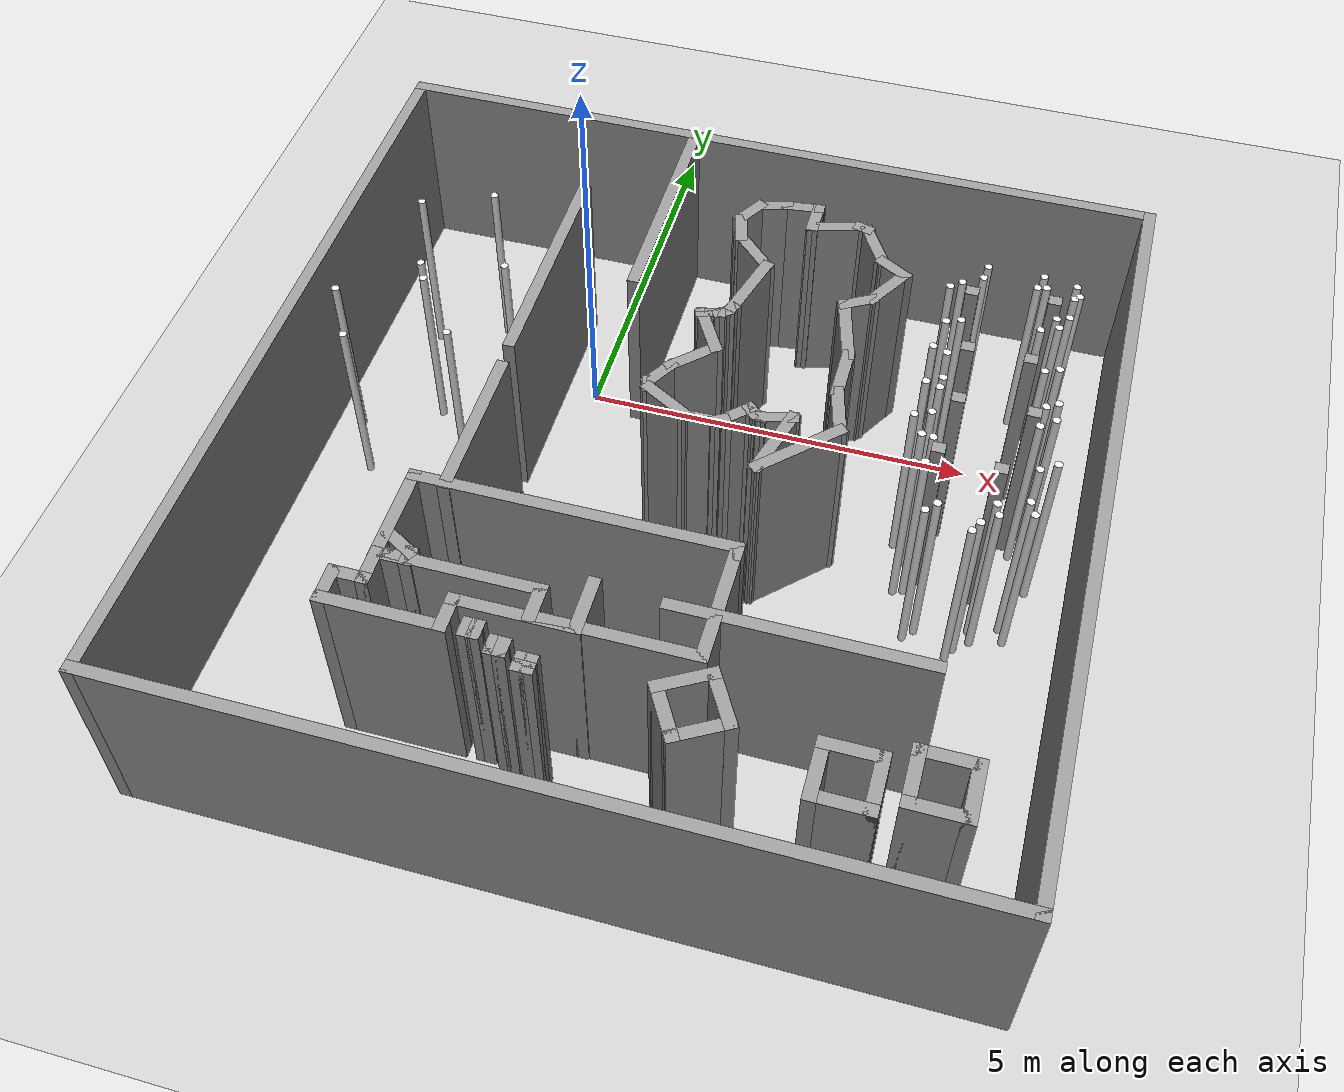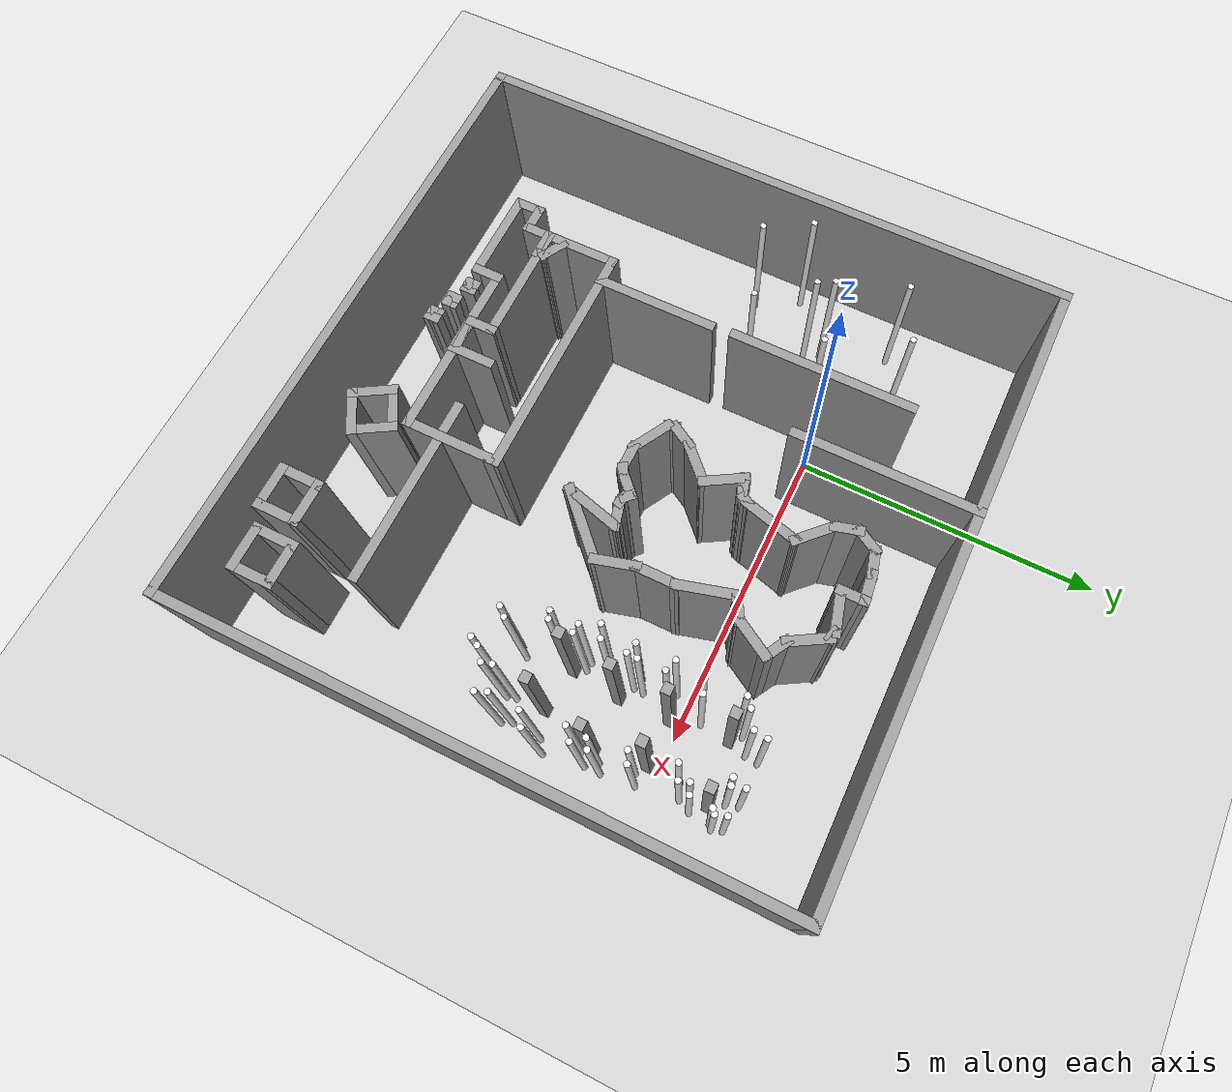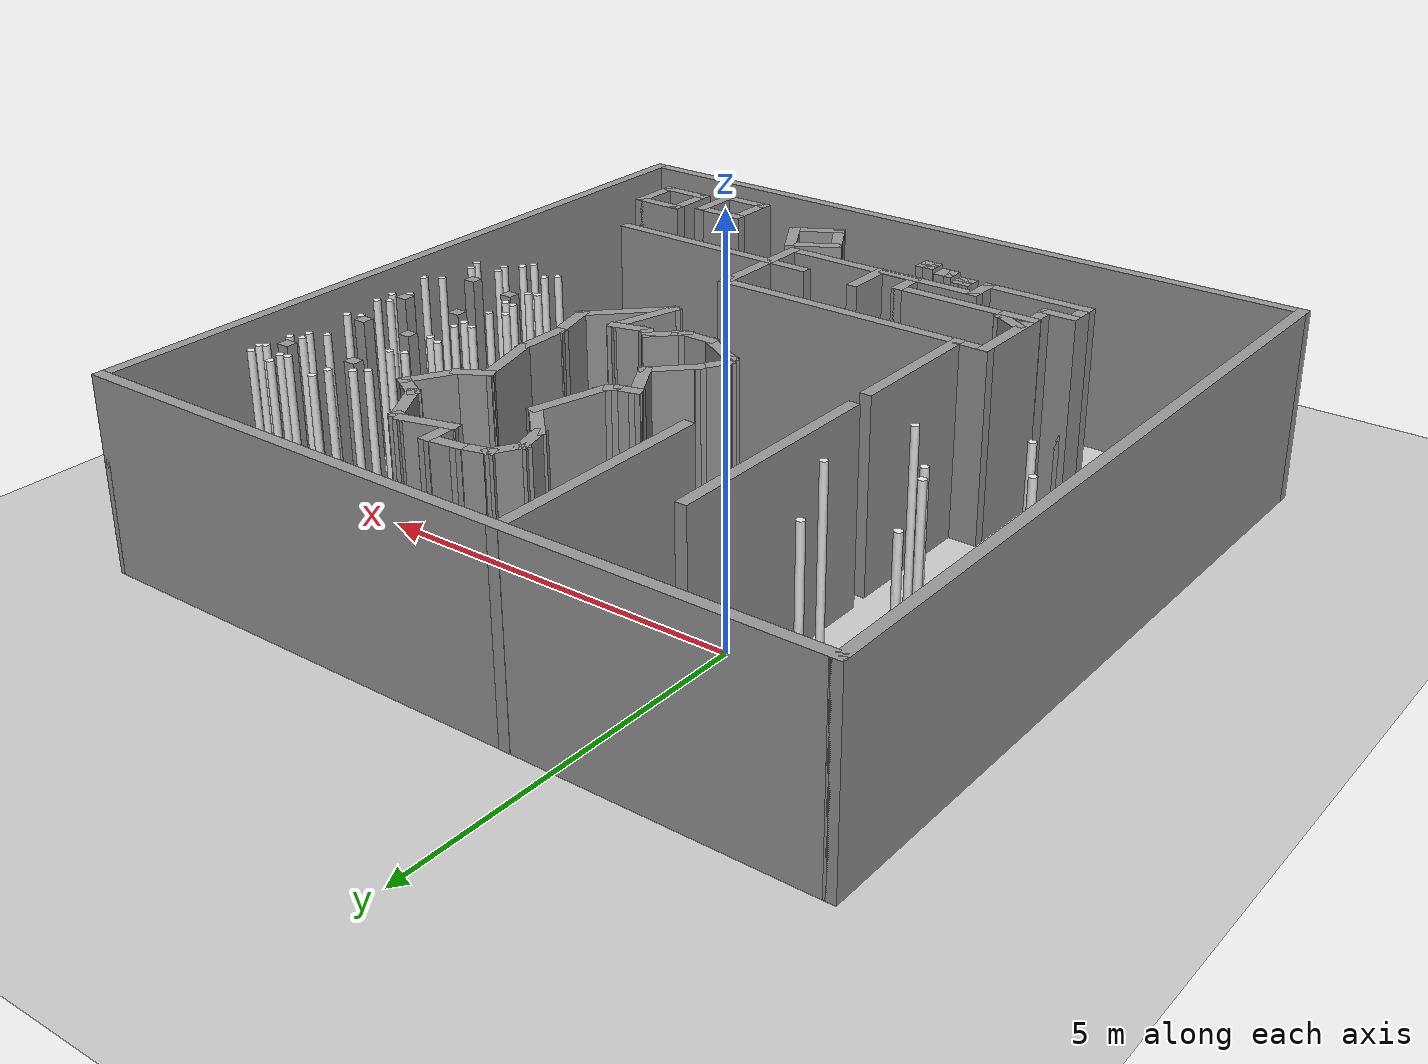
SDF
<sdf version="1.7">
 <world name="default">
  <light name="sun" type="directional">
   <pose>0 0 10 0 -0 0</pose>
   <diffuse>0.8 0.8 0.8 1</diffuse>
   <specular>0.2 0.2 0.2 1</specular>
   <attenuation>
    <range>1000</range>
    <constant>0.9</constant>
    <linear>0.01</linear>
    <quadratic>0.001</quadratic>
   </attenuation>
   <direction>-0.5 0.1 -0.9</direction>
   <spot><inner_angle>0</inner_angle><outer_angle>0</outer_angle><falloff>0</falloff></spot>
  </light>
  <model name="ground_plane">
   <static>1</static>
   <link name="link">
    <collision name="collision">
     <geometry><plane><normal>0 0 1</normal><size>100 100</size></plane></geometry>
     <surface><friction><ode><mu>100</mu><mu2>50</mu2></ode></friction></surface>
    </collision>
    <visual name="visual">
     <cast_shadows>0</cast_shadows>
     <geometry><plane><normal>0 0 1</normal><size>100 100</size></plane></geometry>
     <material>
      <script><uri>file://media/materials/scripts/gazebo.material</uri><name>Gazebo/Grey</name></script>
     </material>
    </visual>
   </link>
  </model>
  <gravity>0 0 -9.8</gravity>
  <magnetic_field>6e-06 2.3e-05 -4.2e-05</magnetic_field>
  <atmosphere type="adiabatic"/>
  <physics type="ode">
   <max_step_size>0.001</max_step_size>
   <real_time_factor>1</real_time_factor>
   <real_time_update_rate>1000</real_time_update_rate>
  </physics>
  <scene><ambient>0.4 0.4 0.4 1</ambient><background>0.7 0.7 0.7 1</background><shadows>1</shadows></scene>
  <spherical_coordinates>
   <surface_model>EARTH_WGS84</surface_model>
   <latitude_deg>0</latitude_deg>
   <longitude_deg>0</longitude_deg>
   <elevation>0</elevation>
   <heading_deg>0</heading_deg>
  </spherical_coordinates>
  <model name="10mx10m">
   <pose>4.18438 -2.20916 0 0 -0 0</pose>
   <link name="Wall_0">
    <collision name="Wall_0_Collision">
     <geometry><box><size>10 0.15 2.5</size></box></geometry>
     <pose>0 0 1.25 0 -0 0</pose>
    </collision>
    <visual name="Wall_0_Visual">
     <pose>0 0 1.25 0 -0 0</pose>
     <geometry><box><size>10 0.15 2.5</size></box></geometry>
     <material>
      <script><uri>file://media/materials/scripts/gazebo.material</uri><name>Gazebo/Grey</name></script>
      <ambient>1 1 1 1</ambient>
     </material>
     <meta><layer>0</layer></meta>
    </visual>
    <pose>2.4125 -0 0 0 -0 1.5708</pose>
   </link>
   <link name="Wall_2">
    <collision name="Wall_2_Collision">
     <geometry><box><size>10 0.15 2.5</size></box></geometry>
     <pose>0 0 1.25 0 -0 0</pose>
    </collision>
    <visual name="Wall_2_Visual">
     <pose>0 0 1.25 0 -0 0</pose>
     <geometry><box><size>10 0.15 2.5</size></box></geometry>
     <material>
      <script><uri>file://media/materials/scripts/gazebo.material</uri><name>Gazebo/Grey</name></script>
      <ambient>1 1 1 1</ambient>
     </material>
     <meta><layer>0</layer></meta>
    </visual>
    <pose>-2.5125 -4.925 0 0 -0 3.14159</pose>
   </link>
   <link name="Wall_3">
    <collision name="Wall_3_Collision">
     <geometry><box><size>10 0.15 2.5</size></box></geometry>
     <pose>0 0 1.25 0 -0 0</pose>
    </collision>
    <visual name="Wall_3_Visual">
     <pose>0 0 1.25 0 -0 0</pose>
     <geometry><box><size>10 0.15 2.5</size></box></geometry>
     <material>
      <script><uri>file://media/materials/scripts/gazebo.material</uri><name>Gazebo/Grey</name></script>
      <ambient>1 1 1 1</ambient>
     </material>
     <meta><layer>0</layer></meta>
    </visual>
    <pose>-7.4375 -0 0 0 -0 1.5708</pose>
   </link>
   <link name="Wall_4">
    <collision name="Wall_4_Collision">
     <geometry><box><size>10 0.15 2.5</size></box></geometry>
     <pose>0 0 1.25 0 -0 0</pose>
    </collision>
    <visual name="Wall_4_Visual">
     <pose>0 0 1.25 0 -0 0</pose>
     <geometry><box><size>10 0.15 2.5</size></box></geometry>
     <material>
      <script><uri>file://media/materials/scripts/gazebo.material</uri><name>Gazebo/Grey</name></script>
      <ambient>1 1 1 1</ambient>
     </material>
     <meta><layer>0</layer></meta>
    </visual>
    <pose>-2.5125 4.925 0 0 -0 0</pose>
   </link>
   <static>1</static>
  </model>
  <model name="3m_wall">
   <pose>2.11152 0.271513 0 0 -0 0</pose>
   <link name="Wall_33">
    <collision name="Wall_33_Collision">
     <geometry><box><size>3 0.15 2.5</size></box></geometry>
     <pose>0 0 1.25 0 -0 0</pose>
    </collision>
    <visual name="Wall_33_Visual">
     <pose>0 0 1.25 0 -0 0</pose>
     <geometry><box><size>3 0.15 2.5</size></box></geometry>
     <material>
      <script><uri>file://media/materials/scripts/gazebo.material</uri><name>Gazebo/Grey</name></script>
      <ambient>1 1 1 1</ambient>
     </material>
     <meta><layer>0</layer></meta>
    </visual>
    <pose>-2.5875 -0.4275 0 0 -0 -1.5708</pose>
   </link>
   <static>1</static>
  </model>
  <model name="3m_wall_clone">
   <pose>3.21394 1.72078 0 0 -0 0</pose>
   <link name="Wall_33">
    <collision name="Wall_33_Collision">
     <geometry><box><size>3 0.15 2.5</size></box></geometry>
     <pose>0 0 1.25 0 -0 0</pose>
    </collision>
    <visual name="Wall_33_Visual">
     <pose>0 0 1.25 0 -0 0</pose>
     <geometry><box><size>3 0.15 2.5</size></box></geometry>
     <material>
      <script><uri>file://media/materials/scripts/gazebo.material</uri><name>Gazebo/Grey</name></script>
      <ambient>1 1 1 1</ambient>
     </material>
     <meta><layer>0</layer></meta>
    </visual>
    <pose>-2.5875 -0.4275 0 0 -0 -1.5708</pose>
   </link>
   <static>1</static>
  </model>
  <model name="2m_wall">
   <pose>2.61075 -2.4429 0 0 -0 0</pose>
   <link name="Wall_37">
    <collision name="Wall_37_Collision">
     <geometry><box><size>2 0.15 2.5</size></box></geometry>
     <pose>0 0 1.25 0 -0 0</pose>
    </collision>
    <visual name="Wall_37_Visual">
     <pose>0 0 1.25 0 -0 0</pose>
     <geometry><box><size>2 0.15 2.5</size></box></geometry>
     <material>
      <script><uri>file://media/materials/scripts/gazebo.material</uri><name>Gazebo/Grey</name></script>
      <ambient>1 1 1 1</ambient>
     </material>
     <meta><layer>0</layer></meta>
    </visual>
    <pose>-3.0625 -0.4625 0 0 -0 -1.5708</pose>
   </link>
   <static>1</static>
  </model>
  <model name="center_wall003">
   <pose>3.21505 0.764634 0 0 -0 0</pose>
   <link name="Wall_50">
    <collision name="Wall_50_Collision">
     <geometry><box><size>0.5 0.15 2.5</size></box></geometry>
     <pose>0 0 1.25 0 -0 0</pose>
    </collision>
    <visual name="Wall_50_Visual">
     <pose>0 0 1.25 0 -0 0</pose>
     <geometry><box><size>0.5 0.15 2.5</size></box></geometry>
     <material>
      <script><uri>file://media/materials/scripts/gazebo.material</uri><name>Gazebo/Grey</name></script>
      <ambient>1 1 1 1</ambient>
     </material>
     <meta><layer>0</layer></meta>
    </visual>
    <pose>-1.25418 0.867026 0 0 -0 -2.87979</pose>
   </link>
   <link name="Wall_51">
    <collision name="Wall_51_Collision">
     <geometry><box><size>0.5 0.15 2.5</size></box></geometry>
     <pose>0 0 1.25 0 -0 0</pose>
    </collision>
    <visual name="Wall_51_Visual">
     <pose>0 0 1.25 0 -0 0</pose>
     <geometry><box><size>0.5 0.15 2.5</size></box></geometry>
     <material>
      <script><uri>file://media/materials/scripts/gazebo.material</uri><name>Gazebo/Grey</name></script>
      <ambient>1 1 1 1</ambient>
     </material>
     <meta><layer>0</layer></meta>
    </visual>
    <pose>-1.51071 0.670178 0 0 -0 -2.0944</pose>
   </link>
   <link name="Wall_52">
    <collision name="Wall_52_Collision">
     <geometry><box><size>0.5 0.15 2.5</size></box></geometry>
     <pose>0 0 1.25 0 -0 0</pose>
    </collision>
    <visual name="Wall_52_Visual">
     <pose>0 0 1.25 0 -0 0</pose>
     <geometry><box><size>0.5 0.15 2.5</size></box></geometry>
     <material>
      <script><uri>file://media/materials/scripts/gazebo.material</uri><name>Gazebo/Grey</name></script>
      <ambient>1 1 1 1</ambient>
     </material>
     <meta><layer>0</layer></meta>
    </visual>
    <pose>-1.55292 0.349587 0 0 -0 -1.309</pose>
   </link>
   <link name="Wall_53">
    <collision name="Wall_53_Collision">
     <geometry><box><size>0.75 0.15 2.5</size></box></geometry>
     <pose>0 0 1.25 0 -0 0</pose>
    </collision>
    <visual name="Wall_53_Visual">
     <pose>0 0 1.25 0 -0 0</pose>
     <geometry><box><size>0.75 0.15 2.5</size></box></geometry>
     <material>
      <script><uri>file://media/materials/scripts/gazebo.material</uri><name>Gazebo/Grey</name></script>
      <ambient>1 1 1 1</ambient>
     </material>
     <meta><layer>0</layer></meta>
    </visual>
    <pose>-1.29549 -0.031582 0 0 -0 -0.785398</pose>
   </link>
   <link name="Wall_54">
    <collision name="Wall_54_Collision">
     <geometry><box><size>1 0.15 2.5</size></box></geometry>
     <pose>0 0 1.25 0 -0 0</pose>
    </collision>
    <visual name="Wall_54_Visual">
     <pose>0 0 1.25 0 -0 0</pose>
     <geometry><box><size>1 0.15 2.5</size></box></geometry>
     <material>
      <script><uri>file://media/materials/scripts/gazebo.material</uri><name>Gazebo/Grey</name></script>
      <ambient>1 1 1 1</ambient>
     </material>
     <meta><layer>0</layer></meta>
    </visual>
    <pose>-1.19336 -0.654233 0 0 -0 -1.8326</pose>
   </link>
   <link name="Wall_55">
    <collision name="Wall_55_Collision">
     <geometry><box><size>0.25 0.15 2.5</size></box></geometry>
     <pose>0 0 1.25 0 -0 0</pose>
    </collision>
    <visual name="Wall_55_Visual">
     <pose>0 0 1.25 0 -0 0</pose>
     <geometry><box><size>0.25 0.15 2.5</size></box></geometry>
     <material>
      <script><uri>file://media/materials/scripts/gazebo.material</uri><name>Gazebo/Grey</name></script>
      <ambient>1 1 1 1</ambient>
     </material>
     <meta><layer>0</layer></meta>
    </visual>
    <pose>-1.32836 -1.10805 0 0 -0 -2.0944</pose>
   </link>
   <link name="Wall_56">
    <collision name="Wall_56_Collision">
     <geometry><box><size>0.25 0.15 2.5</size></box></geometry>
     <pose>0 0 1.25 0 -0 0</pose>
    </collision>
    <visual name="Wall_56_Visual">
     <pose>0 0 1.25 0 -0 0</pose>
     <geometry><box><size>0.25 0.15 2.5</size></box></geometry>
     <material>
      <script><uri>file://media/materials/scripts/gazebo.material</uri><name>Gazebo/Grey</name></script>
      <ambient>1 1 1 1</ambient>
     </material>
     <meta><layer>0</layer></meta>
    </visual>
    <pose>-1.39666 -1.17635 0 0 -0 -2.61799</pose>
   </link>
   <link name="Wall_57">
    <collision name="Wall_57_Collision">
     <geometry><box><size>0.25 0.15 2.5</size></box></geometry>
     <pose>0 0 1.25 0 -0 0</pose>
    </collision>
    <visual name="Wall_57_Visual">
     <pose>0 0 1.25 0 -0 0</pose>
     <geometry><box><size>0.25 0.15 2.5</size></box></geometry>
     <material>
      <script><uri>file://media/materials/scripts/gazebo.material</uri><name>Gazebo/Grey</name></script>
      <ambient>1 1 1 1</ambient>
     </material>
     <meta><layer>0</layer></meta>
    </visual>
    <pose>-1.48826 -1.21429 0 0 -0 -2.87979</pose>
   </link>
   <link name="Wall_58">
    <collision name="Wall_58_Collision">
     <geometry><box><size>0.25 0.15 2.5</size></box></geometry>
     <pose>0 0 1.25 0 -0 0</pose>
    </collision>
    <visual name="Wall_58_Visual">
     <pose>0 0 1.25 0 -0 0</pose>
     <geometry><box><size>0.25 0.15 2.5</size></box></geometry>
     <material>
      <script><uri>file://media/materials/scripts/gazebo.material</uri><name>Gazebo/Grey</name></script>
      <ambient>1 1 1 1</ambient>
     </material>
     <meta><layer>0</layer></meta>
    </visual>
    <pose>-1.58485 -1.24018 0 0 -0 -2.87979</pose>
   </link>
   <link name="Wall_59">
    <collision name="Wall_59_Collision">
     <geometry><box><size>0.75 0.15 2.5</size></box></geometry>
     <pose>0 0 1.25 0 -0 0</pose>
    </collision>
    <visual name="Wall_59_Visual">
     <pose>0 0 1.25 0 -0 0</pose>
     <geometry><box><size>0.75 0.15 2.5</size></box></geometry>
     <material>
      <script><uri>file://media/materials/scripts/gazebo.material</uri><name>Gazebo/Grey</name></script>
      <ambient>1 1 1 1</ambient>
     </material>
     <meta><layer>0</layer></meta>
    </visual>
    <pose>-1.48315 -1.51293 0 0 -0 -1.0472</pose>
   </link>
   <link name="Wall_60">
    <collision name="Wall_60_Collision">
     <geometry><box><size>0.75 0.15 2.5</size></box></geometry>
     <pose>0 0 1.25 0 -0 0</pose>
    </collision>
    <visual name="Wall_60_Visual">
     <pose>0 0 1.25 0 -0 0</pose>
     <geometry><box><size>0.75 0.15 2.5</size></box></geometry>
     <material>
      <script><uri>file://media/materials/scripts/gazebo.material</uri><name>Gazebo/Grey</name></script>
      <ambient>1 1 1 1</ambient>
     </material>
     <meta><layer>0</layer></meta>
    </visual>
    <pose>-1.54528 -1.98487 0 0 -0 -2.35619</pose>
   </link>
   <link name="Wall_61">
    <collision name="Wall_61_Collision">
     <geometry><box><size>0.5 0.15 2.5</size></box></geometry>
     <pose>0 0 1.25 0 -0 0</pose>
    </collision>
    <visual name="Wall_61_Visual">
     <pose>0 0 1.25 0 -0 0</pose>
     <geometry><box><size>0.5 0.15 2.5</size></box></geometry>
     <material>
      <script><uri>file://media/materials/scripts/gazebo.material</uri><name>Gazebo/Grey</name></script>
      <ambient>1 1 1 1</ambient>
     </material>
     <meta><layer>0</layer></meta>
    </visual>
    <pose>-1.84491 -2.34855 0 0 -0 -2.0944</pose>
   </link>
   <link name="Wall_62">
    <collision name="Wall_62_Collision">
     <geometry><box><size>0.25 0.15 2.5</size></box></geometry>
     <pose>0 0 1.25 0 -0 0</pose>
    </collision>
    <visual name="Wall_62_Visual">
     <pose>0 0 1.25 0 -0 0</pose>
     <geometry><box><size>0.25 0.15 2.5</size></box></geometry>
     <material>
      <script><uri>file://media/materials/scripts/gazebo.material</uri><name>Gazebo/Grey</name></script>
      <ambient>1 1 1 1</ambient>
     </material>
     <meta><layer>0</layer></meta>
    </visual>
    <pose>-1.91947 -2.5484 0 0 -0 -1.309</pose>
   </link>
   <link name="Wall_63">
    <collision name="Wall_63_Collision">
     <geometry><box><size>0.75 0.15 2.5</size></box></geometry>
     <pose>0 0 1.25 0 -0 0</pose>
    </collision>
    <visual name="Wall_63_Visual">
     <pose>0 0 1.25 0 -0 0</pose>
     <geometry><box><size>0.75 0.15 2.5</size></box></geometry>
     <material>
      <script><uri>file://media/materials/scripts/gazebo.material</uri><name>Gazebo/Grey</name></script>
      <ambient>1 1 1 1</ambient>
     </material>
     <meta><layer>0</layer></meta>
    </visual>
    <pose>-1.64672 -2.7467 0 0 -0 -0.523599</pose>
   </link>
   <link name="Wall_64">
    <collision name="Wall_64_Collision">
     <geometry><box><size>0.5 0.15 2.5</size></box></geometry>
     <pose>0 0 1.25 0 -0 0</pose>
    </collision>
    <visual name="Wall_64_Visual">
     <pose>0 0 1.25 0 -0 0</pose>
     <geometry><box><size>0.5 0.15 2.5</size></box></geometry>
     <material>
      <script><uri>file://media/materials/scripts/gazebo.material</uri><name>Gazebo/Grey</name></script>
      <ambient>1 1 1 1</ambient>
     </material>
     <meta><layer>0</layer></meta>
    </visual>
    <pose>-1.21191 -2.8967 0 0 -0 0</pose>
   </link>
   <link name="Wall_65">
    <collision name="Wall_65_Collision">
     <geometry><box><size>0.25 0.15 2.5</size></box></geometry>
     <pose>0 0 1.25 0 -0 0</pose>
    </collision>
    <visual name="Wall_65_Visual">
     <pose>0 0 1.25 0 -0 0</pose>
     <geometry><box><size>0.25 0.15 2.5</size></box></geometry>
     <material>
      <script><uri>file://media/materials/scripts/gazebo.material</uri><name>Gazebo/Grey</name></script>
      <ambient>1 1 1 1</ambient>
     </material>
     <meta><layer>0</layer></meta>
    </visual>
    <pose>-0.993611 -2.8717 0 0 -0 0.523599</pose>
   </link>
   <link name="Wall_66">
    <collision name="Wall_66_Collision">
     <geometry><box><size>0.5 0.15 2.5</size></box></geometry>
     <pose>0 0 1.25 0 -0 0</pose>
    </collision>
    <visual name="Wall_66_Visual">
     <pose>0 0 1.25 0 -0 0</pose>
     <geometry><box><size>0.5 0.15 2.5</size></box></geometry>
     <material>
      <script><uri>file://media/materials/scripts/gazebo.material</uri><name>Gazebo/Grey</name></script>
      <ambient>1 1 1 1</ambient>
     </material>
     <meta><layer>0</layer></meta>
    </visual>
    <pose>-0.826566 -2.72295 0 0 -0 0.785398</pose>
   </link>
   <link name="Wall_69">
    <collision name="Wall_69_Collision">
     <geometry><box><size>0.25 0.15 2.5</size></box></geometry>
     <pose>0 0 1.25 0 -0 0</pose>
    </collision>
    <visual name="Wall_69_Visual">
     <pose>0 0 1.25 0 -0 0</pose>
     <geometry><box><size>0.25 0.15 2.5</size></box></geometry>
     <material>
      <script><uri>file://media/materials/scripts/gazebo.material</uri><name>Gazebo/Grey</name></script>
      <ambient>1 1 1 1</ambient>
     </material>
     <meta><layer>0</layer></meta>
    </visual>
    <pose>-0.667467 -2.63457 0 0 -0 -0.785398</pose>
   </link>
   <link name="Wall_70">
    <collision name="Wall_70_Collision">
     <geometry><box><size>0.25 0.15 2.5</size></box></geometry>
     <pose>0 0 1.25 0 -0 0</pose>
    </collision>
    <visual name="Wall_70_Visual">
     <pose>0 0 1.25 0 -0 0</pose>
     <geometry><box><size>0.25 0.15 2.5</size></box></geometry>
     <material>
      <script><uri>file://media/materials/scripts/gazebo.material</uri><name>Gazebo/Grey</name></script>
      <ambient>1 1 1 1</ambient>
     </material>
     <meta><layer>0</layer></meta>
    </visual>
    <pose>-0.583816 -2.68286 0 0 -0 -0.261799</pose>
   </link>
   <link name="Wall_71">
    <collision name="Wall_71_Collision">
     <geometry><box><size>0.5 0.15 2.5</size></box></geometry>
     <pose>0 0 1.25 0 -0 0</pose>
    </collision>
    <visual name="Wall_71_Visual">
     <pose>0 0 1.25 0 -0 0</pose>
     <geometry><box><size>0.5 0.15 2.5</size></box></geometry>
     <material>
      <script><uri>file://media/materials/scripts/gazebo.material</uri><name>Gazebo/Grey</name></script>
      <ambient>1 1 1 1</ambient>
     </material>
     <meta><layer>0</layer></meta>
    </visual>
    <pose>-0.366482 -2.65051 0 0 -0 0.261799</pose>
   </link>
   <link name="Wall_72">
    <collision name="Wall_72_Collision">
     <geometry><box><size>1 0.15 2.5</size></box></geometry>
     <pose>0 0 1.25 0 -0 0</pose>
    </collision>
    <visual name="Wall_72_Visual">
     <pose>0 0 1.25 0 -0 0</pose>
     <geometry><box><size>1 0.15 2.5</size></box></geometry>
     <material>
      <script><uri>file://media/materials/scripts/gazebo.material</uri><name>Gazebo/Grey</name></script>
      <ambient>1 1 1 1</ambient>
     </material>
     <meta><layer>0</layer></meta>
    </visual>
    <pose>-0.307443 -3.01573 0 0 -0 -1.8326</pose>
   </link>
   <link name="Wall_73">
    <collision name="Wall_73_Collision">
     <geometry><box><size>1.25 0.15 2.5</size></box></geometry>
     <pose>0 0 1.25 0 -0 0</pose>
    </collision>
    <visual name="Wall_73_Visual">
     <pose>0 0 1.25 0 -0 0</pose>
     <geometry><box><size>1.25 0.15 2.5</size></box></geometry>
     <material>
      <script><uri>file://media/materials/scripts/gazebo.material</uri><name>Gazebo/Grey</name></script>
      <ambient>1 1 1 1</ambient>
     </material>
     <meta><layer>0</layer></meta>
    </visual>
    <pose>-0.028533 -3.03735 0 0 -0 0.785398</pose>
   </link>
   <link name="Wall_82">
    <collision name="Wall_82_Collision">
     <geometry><box><size>0.75 0.15 2.5</size></box></geometry>
     <pose>0 0 1.25 0 -0 0</pose>
    </collision>
    <visual name="Wall_82_Visual">
     <pose>0 0 1.25 0 -0 0</pose>
     <geometry><box><size>0.75 0.15 2.5</size></box></geometry>
     <material>
      <script><uri>file://media/materials/scripts/gazebo.material</uri><name>Gazebo/Grey</name></script>
      <ambient>1 1 1 1</ambient>
     </material>
     <meta><layer>0</layer></meta>
    </visual>
    <pose>0.28273 -2.35866 0 0 -0 1.8326</pose>
   </link>
   <link name="Wall_83">
    <collision name="Wall_83_Collision">
     <geometry><box><size>0.75 0.15 2.5</size></box></geometry>
     <pose>0 0 1.25 0 -0 0</pose>
    </collision>
    <visual name="Wall_83_Visual">
     <pose>0 0 1.25 0 -0 0</pose>
     <geometry><box><size>0.75 0.15 2.5</size></box></geometry>
     <material>
      <script><uri>file://media/materials/scripts/gazebo.material</uri><name>Gazebo/Grey</name></script>
      <ambient>1 1 1 1</ambient>
     </material>
     <meta><layer>0</layer></meta>
    </visual>
    <pose>0.205084 -1.76888 0 0 -0 1.5708</pose>
   </link>
   <link name="Wall_84">
    <collision name="Wall_84_Collision">
     <geometry><box><size>1 0.15 2.5</size></box></geometry>
     <pose>0 0 1.25 0 -0 0</pose>
    </collision>
    <visual name="Wall_84_Visual">
     <pose>0 0 1.25 0 -0 0</pose>
     <geometry><box><size>1 0.15 2.5</size></box></geometry>
     <material>
      <script><uri>file://media/materials/scripts/gazebo.material</uri><name>Gazebo/Grey</name></script>
      <ambient>1 1 1 1</ambient>
     </material>
     <meta><layer>0</layer></meta>
    </visual>
    <pose>0.095086 -1.05836 0 0 -0 1.8326</pose>
   </link>
   <link name="Wall_85">
    <collision name="Wall_85_Collision">
     <geometry><box><size>0.5 0.15 2.5</size></box></geometry>
     <pose>0 0 1.25 0 -0 0</pose>
    </collision>
    <visual name="Wall_85_Visual">
     <pose>0 0 1.25 0 -0 0</pose>
     <geometry><box><size>0.5 0.15 2.5</size></box></geometry>
     <material>
      <script><uri>file://media/materials/scripts/gazebo.material</uri><name>Gazebo/Grey</name></script>
      <ambient>1 1 1 1</ambient>
     </material>
     <meta><layer>0</layer></meta>
    </visual>
    <pose>0.136643 -0.560344 0 0 -0 0.523599</pose>
   </link>
   <link name="Wall_86">
    <collision name="Wall_86_Collision">
     <geometry><box><size>0.75 0.15 2.5</size></box></geometry>
     <pose>0 0 1.25 0 -0 0</pose>
    </collision>
    <visual name="Wall_86_Visual">
     <pose>0 0 1.25 0 -0 0</pose>
     <geometry><box><size>0.75 0.15 2.5</size></box></geometry>
     <material>
      <script><uri>file://media/materials/scripts/gazebo.material</uri><name>Gazebo/Grey</name></script>
      <ambient>1 1 1 1</ambient>
     </material>
     <meta><layer>0</layer></meta>
    </visual>
    <pose>0.438197 -0.213036 0 0 -0 1.0472</pose>
   </link>
   <link name="Wall_87">
    <collision name="Wall_87_Collision">
     <geometry><box><size>0.5 0.15 2.5</size></box></geometry>
     <pose>0 0 1.25 0 -0 0</pose>
    </collision>
    <visual name="Wall_87_Visual">
     <pose>0 0 1.25 0 -0 0</pose>
     <geometry><box><size>0.5 0.15 2.5</size></box></geometry>
     <material>
      <script><uri>file://media/materials/scripts/gazebo.material</uri><name>Gazebo/Grey</name></script>
      <ambient>1 1 1 1</ambient>
     </material>
     <meta><layer>0</layer></meta>
    </visual>
    <pose>0.436643 0.134271 0 0 -0 2.61799</pose>
   </link>
   <link name="Wall_88">
    <collision name="Wall_88_Collision">
     <geometry><box><size>0.75 0.15 2.5</size></box></geometry>
     <pose>0 0 1.25 0 -0 0</pose>
    </collision>
    <visual name="Wall_88_Visual">
     <pose>0 0 1.25 0 -0 0</pose>
     <geometry><box><size>0.75 0.15 2.5</size></box></geometry>
     <material>
      <script><uri>file://media/materials/scripts/gazebo.material</uri><name>Gazebo/Grey</name></script>
      <ambient>1 1 1 1</ambient>
     </material>
     <meta><layer>0</layer></meta>
    </visual>
    <pose>0.135088 0.481579 0 0 -0 2.0944</pose>
   </link>
   <link name="Wall_89">
    <collision name="Wall_89_Collision">
     <geometry><box><size>0.25 0.15 2.5</size></box></geometry>
     <pose>0 0 1.25 0 -0 0</pose>
    </collision>
    <visual name="Wall_89_Visual">
     <pose>0 0 1.25 0 -0 0</pose>
     <geometry><box><size>0.25 0.15 2.5</size></box></geometry>
     <material>
      <script><uri>file://media/materials/scripts/gazebo.material</uri><name>Gazebo/Grey</name></script>
      <ambient>1 1 1 1</ambient>
     </material>
     <meta><layer>0</layer></meta>
    </visual>
    <pose>-0.063208 0.754328 0 0 -0 2.87979</pose>
   </link>
   <link name="Wall_90">
    <collision name="Wall_90_Collision">
     <geometry><box><size>0.75 0.15 2.5</size></box></geometry>
     <pose>0 0 1.25 0 -0 0</pose>
    </collision>
    <visual name="Wall_90_Visual">
     <pose>0 0 1.25 0 -0 0</pose>
     <geometry><box><size>0.75 0.15 2.5</size></box></geometry>
     <material>
      <script><uri>file://media/materials/scripts/gazebo.material</uri><name>Gazebo/Grey</name></script>
      <ambient>1 1 1 1</ambient>
     </material>
     <meta><layer>0</layer></meta>
    </visual>
    <pose>-0.401282 0.689623 0 0 -0 -2.87979</pose>
   </link>
   <link name="Wall_91">
    <collision name="Wall_91_Collision">
     <geometry><box><size>0.5 0.15 2.5</size></box></geometry>
     <pose>0 0 1.25 0 -0 0</pose>
    </collision>
    <visual name="Wall_91_Visual">
     <pose>0 0 1.25 0 -0 0</pose>
     <geometry><box><size>0.5 0.15 2.5</size></box></geometry>
     <material>
      <script><uri>file://media/materials/scripts/gazebo.material</uri><name>Gazebo/Grey</name></script>
      <ambient>1 1 1 1</ambient>
     </material>
     <meta><layer>0</layer></meta>
    </visual>
    <pose>-0.69106 0.786977 0 0 -0 1.5708</pose>
   </link>
   <link name="Wall_92">
    <collision name="Wall_92_Collision">
     <geometry><box><size>0.547195 0.15 2.5</size></box></geometry>
     <pose>0 0 1.25 0 -0 0</pose>
    </collision>
    <visual name="Wall_92_Visual">
     <pose>0 0 1.25 0 -0 0</pose>
     <geometry><box><size>0.547195 0.15 2.5</size></box></geometry>
     <material>
      <script><uri>file://media/materials/scripts/gazebo.material</uri><name>Gazebo/Grey</name></script>
      <ambient>1 1 1 1</ambient>
     </material>
     <meta><layer>0</layer></meta>
    </visual>
    <pose>-0.888099 0.937148 0 0 -0 -3.01624</pose>
   </link>
   <static>1</static>
  </model>
  <model name="center_wall005">
   <pose>2.40467 -3.64658 0 0 -0 0</pose>
   <link name="Wall_14">
    <collision name="Wall_14_Collision">
     <geometry><box><size>1.25 0.15 2.5</size></box></geometry>
     <pose>0 0 1.25 0 -0 0</pose>
    </collision>
    <visual name="Wall_14_Visual">
     <pose>0 0 1.25 0 -0 0</pose>
     <geometry><box><size>1.25 0.15 2.5</size></box></geometry>
     <material>
      <script><uri>file://media/materials/scripts/gazebo.material</uri><name>Gazebo/Grey</name></script>
      <ambient>1 1 1 1</ambient>
     </material>
     <meta><layer>0</layer></meta>
    </visual>
    <pose>-3.2275 -0.7225 0 0 -0 -1.5708</pose>
   </link>
   <link name="Wall_15">
    <collision name="Wall_15_Collision">
     <geometry><box><size>2 0.15 2.5</size></box></geometry>
     <pose>0 0 1.25 0 -0 0</pose>
    </collision>
    <visual name="Wall_15_Visual">
     <pose>0 0 1.25 0 -0 0</pose>
     <geometry><box><size>2 0.15 2.5</size></box></geometry>
     <material>
      <script><uri>file://media/materials/scripts/gazebo.material</uri><name>Gazebo/Grey</name></script>
      <ambient>1 1 1 1</ambient>
     </material>
     <meta><layer>0</layer></meta>
    </visual>
    <pose>-2.3025 -1.2725 0 0 -0 0</pose>
   </link>
   <link name="Wall_16">
    <collision name="Wall_16_Collision">
     <geometry><box><size>0.5 0.15 2.5</size></box></geometry>
     <pose>0 0 1.25 0 -0 0</pose>
    </collision>
    <visual name="Wall_16_Visual">
     <pose>0 0 1.25 0 -0 0</pose>
     <geometry><box><size>0.5 0.15 2.5</size></box></geometry>
     <material>
      <script><uri>file://media/materials/scripts/gazebo.material</uri><name>Gazebo/Grey</name></script>
      <ambient>1 1 1 1</ambient>
     </material>
     <meta><layer>0</layer></meta>
    </visual>
    <pose>-1.3775 -1.4475 0 0 -0 -1.5708</pose>
   </link>
   <link name="Wall_17">
    <collision name="Wall_17_Collision">
     <geometry><box><size>2 0.15 2.5</size></box></geometry>
     <pose>0 0 1.25 0 -0 0</pose>
    </collision>
    <visual name="Wall_17_Visual">
     <pose>0 0 1.25 0 -0 0</pose>
     <geometry><box><size>2 0.15 2.5</size></box></geometry>
     <material>
      <script><uri>file://media/materials/scripts/gazebo.material</uri><name>Gazebo/Grey</name></script>
      <ambient>1 1 1 1</ambient>
     </material>
     <meta><layer>0</layer></meta>
    </visual>
    <pose>-0.4525 -1.6225 0 0 -0 0</pose>
   </link>
   <link name="Wall_18">
    <collision name="Wall_18_Collision">
     <geometry><box><size>1.5 0.15 2.5</size></box></geometry>
     <pose>0 0 1.25 0 -0 0</pose>
    </collision>
    <visual name="Wall_18_Visual">
     <pose>0 0 1.25 0 -0 0</pose>
     <geometry><box><size>1.5 0.15 2.5</size></box></geometry>
     <material>
      <script><uri>file://media/materials/scripts/gazebo.material</uri><name>Gazebo/Grey</name></script>
      <ambient>1 1 1 1</ambient>
     </material>
     <meta><layer>0</layer></meta>
    </visual>
    <pose>0.4725 -0.9475 0 0 -0 1.5708</pose>
   </link>
   <link name="Wall_19">
    <collision name="Wall_19_Collision">
     <geometry><box><size>0.25 0.15 2.5</size></box></geometry>
     <pose>0 0 1.25 0 -0 0</pose>
    </collision>
    <visual name="Wall_19_Visual">
     <pose>0 0 1.25 0 -0 0</pose>
     <geometry><box><size>0.25 0.15 2.5</size></box></geometry>
     <material>
      <script><uri>file://media/materials/scripts/gazebo.material</uri><name>Gazebo/Grey</name></script>
      <ambient>1 1 1 1</ambient>
     </material>
     <meta><layer>0</layer></meta>
    </visual>
    <pose>0.4725 -0.2225 0 0 -0 1.5708</pose>
   </link>
   <link name="Wall_20">
    <collision name="Wall_20_Collision">
     <geometry><box><size>3.85 0.15 2.5</size></box></geometry>
     <pose>0 0 1.25 0 -0 0</pose>
    </collision>
    <visual name="Wall_20_Visual">
     <pose>0 0 1.25 0 -0 0</pose>
     <geometry><box><size>3.85 0.15 2.5</size></box></geometry>
     <material>
      <script><uri>file://media/materials/scripts/gazebo.material</uri><name>Gazebo/Grey</name></script>
      <ambient>1 1 1 1</ambient>
     </material>
     <meta><layer>0</layer></meta>
    </visual>
    <pose>-1.3775 -0.1725 0 0 -0 3.14159</pose>
   </link>
   <static>1</static>
  </model>
  <model name="3m_wall_clone_0">
   <pose>4.21832 -7.32224 0 0 0 -1.57</pose>
   <link name="Wall_33">
    <collision name="Wall_33_Collision">
     <geometry><box><size>3 0.15 2.5</size></box></geometry>
     <pose>0 0 1.25 0 -0 0</pose>
    </collision>
    <visual name="Wall_33_Visual">
     <pose>0 0 1.25 0 -0 0</pose>
     <geometry><box><size>3 0.15 2.5</size></box></geometry>
     <material>
      <script><uri>file://media/materials/scripts/gazebo.material</uri><name>Gazebo/Grey</name></script>
      <ambient>1 1 1 1</ambient>
     </material>
     <meta><layer>0</layer></meta>
    </visual>
    <pose>-2.5875 -0.4275 0 0 -0 -1.5708</pose>
   </link>
   <static>1</static>
  </model>
  <model name="0.75m_cube_0">
   <pose>4.6917 -7.433 0 0 0 -1.04396</pose>
   <link name="Wall_0">
    <collision name="Wall_0_Collision">
     <geometry><box><size>0.75 0.15 2.5</size></box></geometry>
     <pose>0 0 1.25 0 -0 0</pose>
    </collision>
    <visual name="Wall_0_Visual">
     <pose>0 0 1.25 0 -0 0</pose>
     <geometry><box><size>0.75 0.15 2.5</size></box></geometry>
     <material>
      <script><uri>file://media/materials/scripts/gazebo.material</uri><name>Gazebo/Grey</name></script>
      <ambient>1 1 1 1</ambient>
     </material>
     <meta><layer>0</layer></meta>
    </visual>
    <pose>-2.5575 -0.7225 0 0 -0 -1.5708</pose>
   </link>
   <link name="Wall_1">
    <collision name="Wall_1_Collision">
     <geometry><box><size>0.75 0.15 2.5</size></box></geometry>
     <pose>0 0 1.25 0 -0 0</pose>
    </collision>
    <visual name="Wall_1_Visual">
     <pose>0 0 1.25 0 -0 0</pose>
     <geometry><box><size>0.75 0.15 2.5</size></box></geometry>
     <material>
      <script><uri>file://media/materials/scripts/gazebo.material</uri><name>Gazebo/Grey</name></script>
      <ambient>1 1 1 1</ambient>
     </material>
     <meta><layer>0</layer></meta>
    </visual>
    <pose>-2.2575 -1.0225 0 0 -0 0</pose>
   </link>
   <link name="Wall_2">
    <collision name="Wall_2_Collision">
     <geometry><box><size>0.75 0.15 2.5</size></box></geometry>
     <pose>0 0 1.25 0 -0 0</pose>
    </collision>
    <visual name="Wall_2_Visual">
     <pose>0 0 1.25 0 -0 0</pose>
     <geometry><box><size>0.75 0.15 2.5</size></box></geometry>
     <material>
      <script><uri>file://media/materials/scripts/gazebo.material</uri><name>Gazebo/Grey</name></script>
      <ambient>1 1 1 1</ambient>
     </material>
     <meta><layer>0</layer></meta>
    </visual>
    <pose>-1.9575 -0.7225 0 0 -0 1.5708</pose>
   </link>
   <link name="Wall_3">
    <collision name="Wall_3_Collision">
     <geometry><box><size>0.75 0.15 2.5</size></box></geometry>
     <pose>0 0 1.25 0 -0 0</pose>
    </collision>
    <visual name="Wall_3_Visual">
     <pose>0 0 1.25 0 -0 0</pose>
     <geometry><box><size>0.75 0.15 2.5</size></box></geometry>
     <material>
      <script><uri>file://media/materials/scripts/gazebo.material</uri><name>Gazebo/Grey</name></script>
      <ambient>1 1 1 1</ambient>
     </material>
     <meta><layer>0</layer></meta>
    </visual>
    <pose>-2.2575 -0.4225 0 0 -0 3.14159</pose>
   </link>
   <static>1</static>
  </model>
  <model name="0.75m_cube_1">
   <pose>6.83632 -5.49477 0 0 -0 0</pose>
   <link name="Wall_0">
    <collision name="Wall_0_Collision">
     <geometry><box><size>0.75 0.15 2.5</size></box></geometry>
     <pose>0 0 1.25 0 -0 0</pose>
    </collision>
    <visual name="Wall_0_Visual">
     <pose>0 0 1.25 0 -0 0</pose>
     <geometry><box><size>0.75 0.15 2.5</size></box></geometry>
     <material>
      <script><uri>file://media/materials/scripts/gazebo.material</uri><name>Gazebo/Grey</name></script>
      <ambient>1 1 1 1</ambient>
     </material>
     <meta><layer>0</layer></meta>
    </visual>
    <pose>-2.5575 -0.7225 0 0 -0 -1.5708</pose>
   </link>
   <link name="Wall_1">
    <collision name="Wall_1_Collision">
     <geometry><box><size>0.75 0.15 2.5</size></box></geometry>
     <pose>0 0 1.25 0 -0 0</pose>
    </collision>
    <visual name="Wall_1_Visual">
     <pose>0 0 1.25 0 -0 0</pose>
     <geometry><box><size>0.75 0.15 2.5</size></box></geometry>
     <material>
      <script><uri>file://media/materials/scripts/gazebo.material</uri><name>Gazebo/Grey</name></script>
      <ambient>1 1 1 1</ambient>
     </material>
     <meta><layer>0</layer></meta>
    </visual>
    <pose>-2.2575 -1.0225 0 0 -0 0</pose>
   </link>
   <link name="Wall_2">
    <collision name="Wall_2_Collision">
     <geometry><box><size>0.75 0.15 2.5</size></box></geometry>
     <pose>0 0 1.25 0 -0 0</pose>
    </collision>
    <visual name="Wall_2_Visual">
     <pose>0 0 1.25 0 -0 0</pose>
     <geometry><box><size>0.75 0.15 2.5</size></box></geometry>
     <material>
      <script><uri>file://media/materials/scripts/gazebo.material</uri><name>Gazebo/Grey</name></script>
      <ambient>1 1 1 1</ambient>
     </material>
     <meta><layer>0</layer></meta>
    </visual>
    <pose>-1.9575 -0.7225 0 0 -0 1.5708</pose>
   </link>
   <link name="Wall_3">
    <collision name="Wall_3_Collision">
     <geometry><box><size>0.75 0.15 2.5</size></box></geometry>
     <pose>0 0 1.25 0 -0 0</pose>
    </collision>
    <visual name="Wall_3_Visual">
     <pose>0 0 1.25 0 -0 0</pose>
     <geometry><box><size>0.75 0.15 2.5</size></box></geometry>
     <material>
      <script><uri>file://media/materials/scripts/gazebo.material</uri><name>Gazebo/Grey</name></script>
      <ambient>1 1 1 1</ambient>
     </material>
     <meta><layer>0</layer></meta>
    </visual>
    <pose>-2.2575 -0.4225 0 0 -0 3.14159</pose>
   </link>
   <static>1</static>
  </model>
  <model name="0.75m_cube_1_clone">
   <pose>7.75443 -5.3216 0 0 -0 0</pose>
   <link name="Wall_0">
    <collision name="Wall_0_Collision">
     <geometry><box><size>0.75 0.15 2.5</size></box></geometry>
     <pose>0 0 1.25 0 -0 0</pose>
    </collision>
    <visual name="Wall_0_Visual">
     <pose>0 0 1.25 0 -0 0</pose>
     <geometry><box><size>0.75 0.15 2.5</size></box></geometry>
     <material>
      <script><uri>file://media/materials/scripts/gazebo.material</uri><name>Gazebo/Grey</name></script>
      <ambient>1 1 1 1</ambient>
     </material>
     <meta><layer>0</layer></meta>
    </visual>
    <pose>-2.5575 -0.7225 0 0 -0 -1.5708</pose>
   </link>
   <link name="Wall_1">
    <collision name="Wall_1_Collision">
     <geometry><box><size>0.75 0.15 2.5</size></box></geometry>
     <pose>0 0 1.25 0 -0 0</pose>
    </collision>
    <visual name="Wall_1_Visual">
     <pose>0 0 1.25 0 -0 0</pose>
     <geometry><box><size>0.75 0.15 2.5</size></box></geometry>
     <material>
      <script><uri>file://media/materials/scripts/gazebo.material</uri><name>Gazebo/Grey</name></script>
      <ambient>1 1 1 1</ambient>
     </material>
     <meta><layer>0</layer></meta>
    </visual>
    <pose>-2.2575 -1.0225 0 0 -0 0</pose>
   </link>
   <link name="Wall_2">
    <collision name="Wall_2_Collision">
     <geometry><box><size>0.75 0.15 2.5</size></box></geometry>
     <pose>0 0 1.25 0 -0 0</pose>
    </collision>
    <visual name="Wall_2_Visual">
     <pose>0 0 1.25 0 -0 0</pose>
     <geometry><box><size>0.75 0.15 2.5</size></box></geometry>
     <material>
      <script><uri>file://media/materials/scripts/gazebo.material</uri><name>Gazebo/Grey</name></script>
      <ambient>1 1 1 1</ambient>
     </material>
     <meta><layer>0</layer></meta>
    </visual>
    <pose>-1.9575 -0.7225 0 0 -0 1.5708</pose>
   </link>
   <link name="Wall_3">
    <collision name="Wall_3_Collision">
     <geometry><box><size>0.75 0.15 2.5</size></box></geometry>
     <pose>0 0 1.25 0 -0 0</pose>
    </collision>
    <visual name="Wall_3_Visual">
     <pose>0 0 1.25 0 -0 0</pose>
     <geometry><box><size>0.75 0.15 2.5</size></box></geometry>
     <material>
      <script><uri>file://media/materials/scripts/gazebo.material</uri><name>Gazebo/Grey</name></script>
      <ambient>1 1 1 1</ambient>
     </material>
     <meta><layer>0</layer></meta>
    </visual>
    <pose>-2.2575 -0.4225 0 0 -0 3.14159</pose>
   </link>
   <static>1</static>
  </model>
  <model name="under_left_wall001">
   <pose>0.5386 -4.0873 0 0 -0 0</pose>
   <link name="Wall_10">
    <collision name="Wall_10_Collision">
     <geometry><box><size>0.5 0.15 2.5</size></box></geometry>
     <pose>0 0 1.25 0 -0 0</pose>
    </collision>
    <visual name="Wall_10_Visual">
     <pose>0 0 1.25 0 -0 0</pose>
     <geometry><box><size>0.5 0.15 2.5</size></box></geometry>
     <material>
      <script><uri>file://media/materials/scripts/gazebo.material</uri><name>Gazebo/Grey</name></script>
      <ambient>1 1 1 1</ambient>
     </material>
     <meta><layer>0</layer></meta>
    </visual>
    <pose>-1.3575 -1.0225 0 0 -0 1.5708</pose>
   </link>
   <link name="Wall_11">
    <collision name="Wall_11_Collision">
     <geometry><box><size>0.5 0.15 2.5</size></box></geometry>
     <pose>0 0 1.25 0 -0 0</pose>
    </collision>
    <visual name="Wall_11_Visual">
     <pose>0 0 1.25 0 -0 0</pose>
     <geometry><box><size>0.5 0.15 2.5</size></box></geometry>
     <material>
      <script><uri>file://media/materials/scripts/gazebo.material</uri><name>Gazebo/Grey</name></script>
      <ambient>1 1 1 1</ambient>
     </material>
     <meta><layer>0</layer></meta>
    </visual>
    <pose>-1.1825 -0.8475 0 0 -0 0</pose>
   </link>
   <link name="Wall_12">
    <collision name="Wall_12_Collision">
     <geometry><box><size>0.25 0.15 2.5</size></box></geometry>
     <pose>0 0 1.25 0 -0 0</pose>
    </collision>
    <visual name="Wall_12_Visual">
     <pose>0 0 1.25 0 -0 0</pose>
     <geometry><box><size>0.25 0.15 2.5</size></box></geometry>
     <material>
      <script><uri>file://media/materials/scripts/gazebo.material</uri><name>Gazebo/Grey</name></script>
      <ambient>1 1 1 1</ambient>
     </material>
     <meta><layer>0</layer></meta>
    </visual>
    <pose>-1.0075 -0.7975 0 0 -0 1.5708</pose>
   </link>
   <link name="Wall_13">
    <collision name="Wall_13_Collision">
     <geometry><box><size>0.5 0.15 2.5</size></box></geometry>
     <pose>0 0 1.25 0 -0 0</pose>
    </collision>
    <visual name="Wall_13_Visual">
     <pose>0 0 1.25 0 -0 0</pose>
     <geometry><box><size>0.5 0.15 2.5</size></box></geometry>
     <material>
      <script><uri>file://media/materials/scripts/gazebo.material</uri><name>Gazebo/Grey</name></script>
      <ambient>1 1 1 1</ambient>
     </material>
     <meta><layer>0</layer></meta>
    </visual>
    <pose>-1.15905 -0.66 0 0 -0 2.61799</pose>
   </link>
   <link name="Wall_16">
    <collision name="Wall_16_Collision">
     <geometry><box><size>0.75 0.15 2.5</size></box></geometry>
     <pose>0 0 1.25 0 -0 0</pose>
    </collision>
    <visual name="Wall_16_Visual">
     <pose>0 0 1.25 0 -0 0</pose>
     <geometry><box><size>0.75 0.15 2.5</size></box></geometry>
     <material>
      <script><uri>file://media/materials/scripts/gazebo.material</uri><name>Gazebo/Grey</name></script>
      <ambient>1 1 1 1</ambient>
     </material>
     <meta><layer>0</layer></meta>
    </visual>
    <pose>0.9925 -0.8975 0 0 -0 1.5708</pose>
   </link>
   <link name="Wall_5">
    <collision name="Wall_5_Collision">
     <geometry><box><size>1.5 0.15 2.5</size></box></geometry>
     <pose>0 0 1.25 0 -0 0</pose>
    </collision>
    <visual name="Wall_5_Visual">
     <pose>0 0 1.25 0 -0 0</pose>
     <geometry><box><size>1.5 0.15 2.5</size></box></geometry>
     <material>
      <script><uri>file://media/materials/scripts/gazebo.material</uri><name>Gazebo/Grey</name></script>
      <ambient>1 1 1 1</ambient>
     </material>
     <meta><layer>0</layer></meta>
    </visual>
    <pose>0.3175 -1.1975 0 0 -0 3.14159</pose>
   </link>
   <link name="Wall_6">
    <collision name="Wall_6_Collision">
     <geometry><box><size>0.5 0.15 2.5</size></box></geometry>
     <pose>0 0 1.25 0 -0 0</pose>
    </collision>
    <visual name="Wall_6_Visual">
     <pose>0 0 1.25 0 -0 0</pose>
     <geometry><box><size>0.5 0.15 2.5</size></box></geometry>
     <material>
      <script><uri>file://media/materials/scripts/gazebo.material</uri><name>Gazebo/Grey</name></script>
      <ambient>1 1 1 1</ambient>
     </material>
     <meta><layer>0</layer></meta>
    </visual>
    <pose>-0.3575 -1.3725 0 0 -0 -1.5708</pose>
   </link>
   <link name="Wall_7">
    <collision name="Wall_7_Collision">
     <geometry><box><size>1.5 0.15 2.5</size></box></geometry>
     <pose>0 0 1.25 0 -0 0</pose>
    </collision>
    <visual name="Wall_7_Visual">
     <pose>0 0 1.25 0 -0 0</pose>
     <geometry><box><size>1.5 0.15 2.5</size></box></geometry>
     <material>
      <script><uri>file://media/materials/scripts/gazebo.material</uri><name>Gazebo/Grey</name></script>
      <ambient>1 1 1 1</ambient>
     </material>
     <meta><layer>0</layer></meta>
    </visual>
    <pose>-1.0325 -1.5475 0 0 -0 3.14159</pose>
   </link>
   <link name="Wall_8">
    <collision name="Wall_8_Collision">
     <geometry><box><size>0.5 0.15 2.5</size></box></geometry>
     <pose>0 0 1.25 0 -0 0</pose>
    </collision>
    <visual name="Wall_8_Visual">
     <pose>0 0 1.25 0 -0 0</pose>
     <geometry><box><size>0.5 0.15 2.5</size></box></geometry>
     <material>
      <script><uri>file://media/materials/scripts/gazebo.material</uri><name>Gazebo/Grey</name></script>
      <ambient>1 1 1 1</ambient>
     </material>
     <meta><layer>0</layer></meta>
    </visual>
    <pose>-1.7075 -1.3725 0 0 -0 1.5708</pose>
   </link>
   <link name="Wall_9">
    <collision name="Wall_9_Collision">
     <geometry><box><size>0.5 0.15 2.5</size></box></geometry>
     <pose>0 0 1.25 0 -0 0</pose>
    </collision>
    <visual name="Wall_9_Visual">
     <pose>0 0 1.25 0 -0 0</pose>
     <geometry><box><size>0.5 0.15 2.5</size></box></geometry>
     <material>
      <script><uri>file://media/materials/scripts/gazebo.material</uri><name>Gazebo/Grey</name></script>
      <ambient>1 1 1 1</ambient>
     </material>
     <meta><layer>0</layer></meta>
    </visual>
    <pose>-1.5325 -1.1975 0 0 -0 0</pose>
   </link>
   <static>1</static>
  </model>
  <model name="0.25m_cube">
   <pose>2.21963 -3.88995 0 0 -0 0</pose>
   <link name="Wall_18">
    <collision name="Wall_18_Collision">
     <geometry><box><size>0.25 0.15 2.5</size></box></geometry>
     <pose>0 0 1.25 0 -0 0</pose>
    </collision>
    <visual name="Wall_18_Visual">
     <pose>0 0 1.25 0 -0 0</pose>
     <geometry><box><size>0.25 0.15 2.5</size></box></geometry>
     <material>
      <script><uri>file://media/materials/scripts/gazebo.material</uri><name>Gazebo/Grey</name></script>
      <ambient>1 1 1 1</ambient>
     </material>
     <meta><layer>0</layer></meta>
    </visual>
    <pose>-1.77505 -1.68895 0 0 -0 -1.5708</pose>
   </link>
   <link name="Wall_19">
    <collision name="Wall_19_Collision">
     <geometry><box><size>0.25 0.15 2.5</size></box></geometry>
     <pose>0 0 1.25 0 -0 0</pose>
    </collision>
    <visual name="Wall_19_Visual">
     <pose>0 0 1.25 0 -0 0</pose>
     <geometry><box><size>0.25 0.15 2.5</size></box></geometry>
     <material>
      <script><uri>file://media/materials/scripts/gazebo.material</uri><name>Gazebo/Grey</name></script>
      <ambient>1 1 1 1</ambient>
     </material>
     <meta><layer>0</layer></meta>
    </visual>
    <pose>-1.72505 -1.73894 0 0 -0 0</pose>
   </link>
   <link name="Wall_20">
    <collision name="Wall_20_Collision">
     <geometry><box><size>0.25 0.15 2.5</size></box></geometry>
     <pose>0 0 1.25 0 -0 0</pose>
    </collision>
    <visual name="Wall_20_Visual">
     <pose>0 0 1.25 0 -0 0</pose>
     <geometry><box><size>0.25 0.15 2.5</size></box></geometry>
     <material>
      <script><uri>file://media/materials/scripts/gazebo.material</uri><name>Gazebo/Grey</name></script>
      <ambient>1 1 1 1</ambient>
     </material>
     <meta><layer>0</layer></meta>
    </visual>
    <pose>-1.67505 -1.68895 0 0 -0 1.5708</pose>
   </link>
   <static>1</static>
  </model>
  <model name="0.25m_cube_clone">
   <pose>2.55207 -4.02545 0 0 -0 0</pose>
   <link name="Wall_18">
    <collision name="Wall_18_Collision">
     <geometry><box><size>0.25 0.15 2.5</size></box></geometry>
     <pose>0 0 1.25 0 -0 0</pose>
    </collision>
    <visual name="Wall_18_Visual">
     <pose>0 0 1.25 0 -0 0</pose>
     <geometry><box><size>0.25 0.15 2.5</size></box></geometry>
     <material>
      <script><uri>file://media/materials/scripts/gazebo.material</uri><name>Gazebo/Grey</name></script>
      <ambient>1 1 1 1</ambient>
     </material>
     <meta><layer>0</layer></meta>
    </visual>
    <pose>-1.77505 -1.68895 0 0 -0 -1.5708</pose>
   </link>
   <link name="Wall_19">
    <collision name="Wall_19_Collision">
     <geometry><box><size>0.25 0.15 2.5</size></box></geometry>
     <pose>0 0 1.25 0 -0 0</pose>
    </collision>
    <visual name="Wall_19_Visual">
     <pose>0 0 1.25 0 -0 0</pose>
     <geometry><box><size>0.25 0.15 2.5</size></box></geometry>
     <material>
      <script><uri>file://media/materials/scripts/gazebo.material</uri><name>Gazebo/Grey</name></script>
      <ambient>1 1 1 1</ambient>
     </material>
     <meta><layer>0</layer></meta>
    </visual>
    <pose>-1.72505 -1.73894 0 0 -0 0</pose>
   </link>
   <link name="Wall_20">
    <collision name="Wall_20_Collision">
     <geometry><box><size>0.25 0.15 2.5</size></box></geometry>
     <pose>0 0 1.25 0 -0 0</pose>
    </collision>
    <visual name="Wall_20_Visual">
     <pose>0 0 1.25 0 -0 0</pose>
     <geometry><box><size>0.25 0.15 2.5</size></box></geometry>
     <material>
      <script><uri>file://media/materials/scripts/gazebo.material</uri><name>Gazebo/Grey</name></script>
      <ambient>1 1 1 1</ambient>
     </material>
     <meta><layer>0</layer></meta>
    </visual>
    <pose>-1.67505 -1.68895 0 0 -0 1.5708</pose>
   </link>
   <static>1</static>
  </model>
  <model name="0.25m_cube_clone_0">
   <pose>2.88559 -4.14481 0 0 -0 0</pose>
   <link name="Wall_18">
    <collision name="Wall_18_Collision">
     <geometry><box><size>0.25 0.15 2.5</size></box></geometry>
     <pose>0 0 1.25 0 -0 0</pose>
    </collision>
    <visual name="Wall_18_Visual">
     <pose>0 0 1.25 0 -0 0</pose>
     <geometry><box><size>0.25 0.15 2.5</size></box></geometry>
     <material>
      <script><uri>file://media/materials/scripts/gazebo.material</uri><name>Gazebo/Grey</name></script>
      <ambient>1 1 1 1</ambient>
     </material>
     <meta><layer>0</layer></meta>
    </visual>
    <pose>-1.77505 -1.68895 0 0 -0 -1.5708</pose>
   </link>
   <link name="Wall_19">
    <collision name="Wall_19_Collision">
     <geometry><box><size>0.25 0.15 2.5</size></box></geometry>
     <pose>0 0 1.25 0 -0 0</pose>
    </collision>
    <visual name="Wall_19_Visual">
     <pose>0 0 1.25 0 -0 0</pose>
     <geometry><box><size>0.25 0.15 2.5</size></box></geometry>
     <material>
      <script><uri>file://media/materials/scripts/gazebo.material</uri><name>Gazebo/Grey</name></script>
      <ambient>1 1 1 1</ambient>
     </material>
     <meta><layer>0</layer></meta>
    </visual>
    <pose>-1.72505 -1.73894 0 0 -0 0</pose>
   </link>
   <link name="Wall_20">
    <collision name="Wall_20_Collision">
     <geometry><box><size>0.25 0.15 2.5</size></box></geometry>
     <pose>0 0 1.25 0 -0 0</pose>
    </collision>
    <visual name="Wall_20_Visual">
     <pose>0 0 1.25 0 -0 0</pose>
     <geometry><box><size>0.25 0.15 2.5</size></box></geometry>
     <material>
      <script><uri>file://media/materials/scripts/gazebo.material</uri><name>Gazebo/Grey</name></script>
      <ambient>1 1 1 1</ambient>
     </material>
     <meta><layer>0</layer></meta>
    </visual>
    <pose>-1.67505 -1.68895 0 0 -0 1.5708</pose>
   </link>
   <static>1</static>
  </model>
  <model name="0.16_wall_clone_6">
   <pose>5.58437 2.57587 0 0 -0 0</pose>
   <link name="Wall_22">
    <collision name="Wall_22_Collision">
     <geometry><box><size>0.16 0.15 2.5</size></box></geometry>
     <pose>0 0 1.25 0 -0 0</pose>
    </collision>
    <visual name="Wall_22_Visual">
     <pose>0 0 1.25 0 -0 0</pose>
     <geometry><box><size>0.16 0.15 2.5</size></box></geometry>
     <material>
      <script><uri>file://media/materials/scripts/gazebo.material</uri><name>Gazebo/Grey</name></script>
      <ambient>1 1 1 1</ambient>
     </material>
     <meta><layer>0</layer></meta>
    </visual>
    <pose>-0.929849 -1.80578 0 0 -0 3.14159</pose>
   </link>
   <static>1</static>
  </model>
  <model name="0.16_wall_clone_7">
   <pose>6.57855 2.67796 0 0 -0 0</pose>
   <link name="Wall_22">
    <collision name="Wall_22_Collision">
     <geometry><box><size>0.16 0.15 2.5</size></box></geometry>
     <pose>0 0 1.25 0 -0 0</pose>
    </collision>
    <visual name="Wall_22_Visual">
     <pose>0 0 1.25 0 -0 0</pose>
     <geometry><box><size>0.16 0.15 2.5</size></box></geometry>
     <material>
      <script><uri>file://media/materials/scripts/gazebo.material</uri><name>Gazebo/Grey</name></script>
      <ambient>1 1 1 1</ambient>
     </material>
     <meta><layer>0</layer></meta>
    </visual>
    <pose>-0.929849 -1.80578 0 0 -0 3.14159</pose>
   </link>
   <static>1</static>
  </model>
  <model name="0.16_wall_clone_8">
   <pose>6.43517 1.62421 0 0 -0 0</pose>
   <link name="Wall_22">
    <collision name="Wall_22_Collision">
     <geometry><box><size>0.16 0.15 2.5</size></box></geometry>
     <pose>0 0 1.25 0 -0 0</pose>
    </collision>
    <visual name="Wall_22_Visual">
     <pose>0 0 1.25 0 -0 0</pose>
     <geometry><box><size>0.16 0.15 2.5</size></box></geometry>
     <material>
      <script><uri>file://media/materials/scripts/gazebo.material</uri><name>Gazebo/Grey</name></script>
      <ambient>1 1 1 1</ambient>
     </material>
     <meta><layer>0</layer></meta>
    </visual>
    <pose>-0.929849 -1.80578 0 0 -0 3.14159</pose>
   </link>
   <static>1</static>
  </model>
  <model name="0.16_wall_clone_9">
   <pose>5.68607 1.62961 0 0 -0 0</pose>
   <link name="Wall_22">
    <collision name="Wall_22_Collision">
     <geometry><box><size>0.16 0.15 2.5</size></box></geometry>
     <pose>0 0 1.25 0 -0 0</pose>
    </collision>
    <visual name="Wall_22_Visual">
     <pose>0 0 1.25 0 -0 0</pose>
     <geometry><box><size>0.16 0.15 2.5</size></box></geometry>
     <material>
      <script><uri>file://media/materials/scripts/gazebo.material</uri><name>Gazebo/Grey</name></script>
      <ambient>1 1 1 1</ambient>
     </material>
     <meta><layer>0</layer></meta>
    </visual>
    <pose>-0.929849 -1.80578 0 0 -0 3.14159</pose>
   </link>
   <static>1</static>
  </model>
  <model name="0.16_wall_clone_10">
   <pose>6.59414 0.79446 0 0 -0 0</pose>
   <link name="Wall_22">
    <collision name="Wall_22_Collision">
     <geometry><box><size>0.16 0.15 2.5</size></box></geometry>
     <pose>0 0 1.25 0 -0 0</pose>
    </collision>
    <visual name="Wall_22_Visual">
     <pose>0 0 1.25 0 -0 0</pose>
     <geometry><box><size>0.16 0.15 2.5</size></box></geometry>
     <material>
      <script><uri>file://media/materials/scripts/gazebo.material</uri><name>Gazebo/Grey</name></script>
      <ambient>1 1 1 1</ambient>
     </material>
     <meta><layer>0</layer></meta>
    </visual>
    <pose>-0.929849 -1.80578 0 0 -0 3.14159</pose>
   </link>
   <static>1</static>
  </model>
  <model name="0.16_wall_clone_11">
   <pose>6.35594 -0.14363 0 0 -0 0</pose>
   <link name="Wall_22">
    <collision name="Wall_22_Collision">
     <geometry><box><size>0.16 0.15 2.5</size></box></geometry>
     <pose>0 0 1.25 0 -0 0</pose>
    </collision>
    <visual name="Wall_22_Visual">
     <pose>0 0 1.25 0 -0 0</pose>
     <geometry><box><size>0.16 0.15 2.5</size></box></geometry>
     <material>
      <script><uri>file://media/materials/scripts/gazebo.material</uri><name>Gazebo/Grey</name></script>
      <ambient>1 1 1 1</ambient>
     </material>
     <meta><layer>0</layer></meta>
    </visual>
    <pose>-0.929849 -1.80578 0 0 -0 3.14159</pose>
   </link>
   <static>1</static>
  </model>
  <model name="0.16_wall_clone_12">
   <pose>5.62967 -0.03276 0 0 -0 0</pose>
   <link name="Wall_22">
    <collision name="Wall_22_Collision">
     <geometry><box><size>0.16 0.15 2.5</size></box></geometry>
     <pose>0 0 1.25 0 -0 0</pose>
    </collision>
    <visual name="Wall_22_Visual">
     <pose>0 0 1.25 0 -0 0</pose>
     <geometry><box><size>0.16 0.15 2.5</size></box></geometry>
     <material>
      <script><uri>file://media/materials/scripts/gazebo.material</uri><name>Gazebo/Grey</name></script>
      <ambient>1 1 1 1</ambient>
     </material>
     <meta><layer>0</layer></meta>
    </visual>
    <pose>-0.929849 -1.80578 0 0 -0 3.14159</pose>
   </link>
   <static>1</static>
  </model>
  <model name="0.16_wall_clone_13">
   <pose>5.71648 0.78705 0 0 -0 0</pose>
   <link name="Wall_22">
    <collision name="Wall_22_Collision">
     <geometry><box><size>0.16 0.15 2.5</size></box></geometry>
     <pose>0 0 1.25 0 -0 0</pose>
    </collision>
    <visual name="Wall_22_Visual">
     <pose>0 0 1.25 0 -0 0</pose>
     <geometry><box><size>0.16 0.15 2.5</size></box></geometry>
     <material>
      <script><uri>file://media/materials/scripts/gazebo.material</uri><name>Gazebo/Grey</name></script>
      <ambient>1 1 1 1</ambient>
     </material>
     <meta><layer>0</layer></meta>
    </visual>
    <pose>-0.929849 -1.80578 0 0 -0 3.14159</pose>
   </link>
   <static>1</static>
  </model>
  <model name="White_pole_clone">
   <link name="link_0">
    <inertial>
     <mass>1</mass>
     <inertia><ixx>0.145833</ixx><ixy>0</ixy><ixz>0</ixz><iyy>0.145833</iyy><iyz>0</iyz><izz>0.125</izz></inertia>
    </inertial>
    <visual name="visual">
     <geometry><cylinder><radius>0.0478039</radius><length>2.47001</length></cylinder></geometry>
     <material>
      <lighting>1</lighting>
      <script><uri>file://media/materials/scripts/gazebo.material</uri><name>Gazebo/White</name></script>
      <shader type="vertex"><normal_map>__default__</normal_map></shader>
      <ambient>1 1 1 1</ambient>
      <diffuse>1 1 1 1</diffuse>
      <specular>0 0 0 1</specular>
      <emissive>0 0 0 1</emissive>
     </material>
    </visual>
    <collision name="collision">
     <geometry><cylinder><radius>0.047804</radius><length>2.47001</length></cylinder></geometry>
     <surface>
      <friction>
       <ode><mu>1</mu><mu2>1</mu2><fdir1>0 0 0</fdir1><slip1>0</slip1><slip2>0</slip2></ode>
       <torsional>
        <coefficient>1</coefficient>
        <patch_radius>0</patch_radius>
        <surface_radius>0</surface_radius>
        <use_patch_radius>1</use_patch_radius>
        <ode><slip>0</slip></ode>
       </torsional>
      </friction>
      <bounce><restitution_coefficient>0</restitution_coefficient><threshold>1e+06</threshold></bounce>
      <contact>
       <collide_without_contact>0</collide_without_contact>
       <collide_without_contact_bitmask>1</collide_without_contact_bitmask>
       <collide_bitmask>1</collide_bitmask>
       <ode>
        <soft_cfm>0</soft_cfm>
        <soft_erp>0.2</soft_erp>
        <kp>1e+13</kp>
        <kd>1</kd>
        <max_vel>0.01</max_vel>
        <min_depth>0</min_depth>
       </ode>
       <bullet>
        <split_impulse>1</split_impulse>
        <split_impulse_penetration_threshold>-0.01</split_impulse_penetration_threshold>
        <soft_cfm>0</soft_cfm>
        <soft_erp>0.2</soft_erp>
        <kp>1e+13</kp>
        <kd>1</kd>
       </bullet>
      </contact>
     </surface>
    </collision>
   </link>
   <static>1</static>
   <pose>5.80842 -2.31498 1.235 0 -2e-06 -5e-06</pose>
  </model>
  <model name="White_pole_clone_clone">
   <link name="link_0">
    <inertial>
     <mass>1</mass>
     <inertia><ixx>0.145833</ixx><ixy>0</ixy><ixz>0</ixz><iyy>0.145833</iyy><iyz>0</iyz><izz>0.125</izz></inertia>
    </inertial>
    <visual name="visual">
     <geometry><cylinder><radius>0.0478039</radius><length>2.47001</length></cylinder></geometry>
     <material>
      <lighting>1</lighting>
      <script><uri>file://media/materials/scripts/gazebo.material</uri><name>Gazebo/White</name></script>
      <shader type="vertex"><normal_map>__default__</normal_map></shader>
      <ambient>1 1 1 1</ambient>
      <diffuse>1 1 1 1</diffuse>
      <specular>0 0 0 1</specular>
      <emissive>0 0 0 1</emissive>
     </material>
    </visual>
    <collision name="collision">
     <geometry><cylinder><radius>0.047804</radius><length>2.47001</length></cylinder></geometry>
     <surface>
      <friction>
       <ode><mu>1</mu><mu2>1</mu2><fdir1>0 0 0</fdir1><slip1>0</slip1><slip2>0</slip2></ode>
       <torsional>
        <coefficient>1</coefficient>
        <patch_radius>0</patch_radius>
        <surface_radius>0</surface_radius>
        <use_patch_radius>1</use_patch_radius>
        <ode><slip>0</slip></ode>
       </torsional>
      </friction>
      <bounce><restitution_coefficient>0</restitution_coefficient><threshold>1e+06</threshold></bounce>
      <contact>
       <collide_without_contact>0</collide_without_contact>
       <collide_without_contact_bitmask>1</collide_without_contact_bitmask>
       <collide_bitmask>1</collide_bitmask>
       <ode>
        <soft_cfm>0</soft_cfm>
        <soft_erp>0.2</soft_erp>
        <kp>1e+13</kp>
        <kd>1</kd>
        <max_vel>0.01</max_vel>
        <min_depth>0</min_depth>
       </ode>
       <bullet>
        <split_impulse>1</split_impulse>
        <split_impulse_penetration_threshold>-0.01</split_impulse_penetration_threshold>
        <soft_cfm>0</soft_cfm>
        <soft_erp>0.2</soft_erp>
        <kp>1e+13</kp>
        <kd>1</kd>
       </bullet>
      </contact>
     </surface>
    </collision>
   </link>
   <static>1</static>
   <pose>5.45895 -2.44059 1.235 0 -2e-06 -5e-06</pose>
  </model>
  <model name="White_pole_clone_clone_0">
   <link name="link_0">
    <inertial>
     <mass>1</mass>
     <inertia><ixx>0.145833</ixx><ixy>0</ixy><ixz>0</ixz><iyy>0.145833</iyy><iyz>0</iyz><izz>0.125</izz></inertia>
    </inertial>
    <visual name="visual">
     <geometry><cylinder><radius>0.0478039</radius><length>2.47001</length></cylinder></geometry>
     <material>
      <lighting>1</lighting>
      <script><uri>file://media/materials/scripts/gazebo.material</uri><name>Gazebo/White</name></script>
      <shader type="vertex"><normal_map>__default__</normal_map></shader>
      <ambient>1 1 1 1</ambient>
      <diffuse>1 1 1 1</diffuse>
      <specular>0 0 0 1</specular>
      <emissive>0 0 0 1</emissive>
     </material>
    </visual>
    <collision name="collision">
     <geometry><cylinder><radius>0.047804</radius><length>2.47001</length></cylinder></geometry>
     <surface>
      <friction>
       <ode><mu>1</mu><mu2>1</mu2><fdir1>0 0 0</fdir1><slip1>0</slip1><slip2>0</slip2></ode>
       <torsional>
        <coefficient>1</coefficient>
        <patch_radius>0</patch_radius>
        <surface_radius>0</surface_radius>
        <use_patch_radius>1</use_patch_radius>
        <ode><slip>0</slip></ode>
       </torsional>
      </friction>
      <bounce><restitution_coefficient>0</restitution_coefficient><threshold>1e+06</threshold></bounce>
      <contact>
       <collide_without_contact>0</collide_without_contact>
       <collide_without_contact_bitmask>1</collide_without_contact_bitmask>
       <collide_bitmask>1</collide_bitmask>
       <ode>
        <soft_cfm>0</soft_cfm>
        <soft_erp>0.2</soft_erp>
        <kp>1e+13</kp>
        <kd>1</kd>
        <max_vel>0.01</max_vel>
        <min_depth>0</min_depth>
       </ode>
       <bullet>
        <split_impulse>1</split_impulse>
        <split_impulse_penetration_threshold>-0.01</split_impulse_penetration_threshold>
        <soft_cfm>0</soft_cfm>
        <soft_erp>0.2</soft_erp>
        <kp>1e+13</kp>
        <kd>1</kd>
       </bullet>
      </contact>
     </surface>
    </collision>
   </link>
   <static>1</static>
   <pose>5.87971 -2.48644 1.235 0 -2e-06 -5e-06</pose>
  </model>
  <model name="White_pole_clone_clone_1">
   <link name="link_0">
    <inertial>
     <mass>1</mass>
     <inertia><ixx>0.145833</ixx><ixy>0</ixy><ixz>0</ixz><iyy>0.145833</iyy><iyz>0</iyz><izz>0.125</izz></inertia>
    </inertial>
    <visual name="visual">
     <geometry><cylinder><radius>0.0478039</radius><length>2.47001</length></cylinder></geometry>
     <material>
      <lighting>1</lighting>
      <script><uri>file://media/materials/scripts/gazebo.material</uri><name>Gazebo/White</name></script>
      <shader type="vertex"><normal_map>__default__</normal_map></shader>
      <ambient>1 1 1 1</ambient>
      <diffuse>1 1 1 1</diffuse>
      <specular>0 0 0 1</specular>
      <emissive>0 0 0 1</emissive>
     </material>
    </visual>
    <collision name="collision">
     <geometry><cylinder><radius>0.047804</radius><length>2.47001</length></cylinder></geometry>
     <surface>
      <friction>
       <ode><mu>1</mu><mu2>1</mu2><fdir1>0 0 0</fdir1><slip1>0</slip1><slip2>0</slip2></ode>
       <torsional>
        <coefficient>1</coefficient>
        <patch_radius>0</patch_radius>
        <surface_radius>0</surface_radius>
        <use_patch_radius>1</use_patch_radius>
        <ode><slip>0</slip></ode>
       </torsional>
      </friction>
      <bounce><restitution_coefficient>0</restitution_coefficient><threshold>1e+06</threshold></bounce>
      <contact>
       <collide_without_contact>0</collide_without_contact>
       <collide_without_contact_bitmask>1</collide_without_contact_bitmask>
       <collide_bitmask>1</collide_bitmask>
       <ode>
        <soft_cfm>0</soft_cfm>
        <soft_erp>0.2</soft_erp>
        <kp>1e+13</kp>
        <kd>1</kd>
        <max_vel>0.01</max_vel>
        <min_depth>0</min_depth>
       </ode>
       <bullet>
        <split_impulse>1</split_impulse>
        <split_impulse_penetration_threshold>-0.01</split_impulse_penetration_threshold>
        <soft_cfm>0</soft_cfm>
        <soft_erp>0.2</soft_erp>
        <kp>1e+13</kp>
        <kd>1</kd>
       </bullet>
      </contact>
     </surface>
    </collision>
   </link>
   <static>1</static>
   <pose>5.50038 -2.5943 1.235 0 -2e-06 -5e-06</pose>
  </model>
  <model name="White_pole_clone_clone_2">
   <link name="link_0">
    <inertial>
     <mass>1</mass>
     <inertia><ixx>0.145833</ixx><ixy>0</ixy><ixz>0</ixz><iyy>0.145833</iyy><iyz>0</iyz><izz>0.125</izz></inertia>
    </inertial>
    <visual name="visual">
     <geometry><cylinder><radius>0.0478039</radius><length>2.47001</length></cylinder></geometry>
     <material>
      <lighting>1</lighting>
      <script><uri>file://media/materials/scripts/gazebo.material</uri><name>Gazebo/White</name></script>
      <shader type="vertex"><normal_map>__default__</normal_map></shader>
      <ambient>1 1 1 1</ambient>
      <diffuse>1 1 1 1</diffuse>
      <specular>0 0 0 1</specular>
      <emissive>0 0 0 1</emissive>
     </material>
    </visual>
    <collision name="collision">
     <geometry><cylinder><radius>0.047804</radius><length>2.47001</length></cylinder></geometry>
     <surface>
      <friction>
       <ode><mu>1</mu><mu2>1</mu2><fdir1>0 0 0</fdir1><slip1>0</slip1><slip2>0</slip2></ode>
       <torsional>
        <coefficient>1</coefficient>
        <patch_radius>0</patch_radius>
        <surface_radius>0</surface_radius>
        <use_patch_radius>1</use_patch_radius>
        <ode><slip>0</slip></ode>
       </torsional>
      </friction>
      <bounce><restitution_coefficient>0</restitution_coefficient><threshold>1e+06</threshold></bounce>
      <contact>
       <collide_without_contact>0</collide_without_contact>
       <collide_without_contact_bitmask>1</collide_without_contact_bitmask>
       <collide_bitmask>1</collide_bitmask>
       <ode>
        <soft_cfm>0</soft_cfm>
        <soft_erp>0.2</soft_erp>
        <kp>1e+13</kp>
        <kd>1</kd>
        <max_vel>0.01</max_vel>
        <min_depth>0</min_depth>
       </ode>
       <bullet>
        <split_impulse>1</split_impulse>
        <split_impulse_penetration_threshold>-0.01</split_impulse_penetration_threshold>
        <soft_cfm>0</soft_cfm>
        <soft_erp>0.2</soft_erp>
        <kp>1e+13</kp>
        <kd>1</kd>
       </bullet>
      </contact>
     </surface>
    </collision>
   </link>
   <static>1</static>
   <pose>5.32308 -2.74641 1.235 0 -2e-06 -5e-06</pose>
  </model>
  <model name="White_pole_clone_clone_3">
   <link name="link_0">
    <inertial>
     <mass>1</mass>
     <inertia><ixx>0.145833</ixx><ixy>0</ixy><ixz>0</ixz><iyy>0.145833</iyy><iyz>0</iyz><izz>0.125</izz></inertia>
    </inertial>
    <visual name="visual">
     <geometry><cylinder><radius>0.0478039</radius><length>2.47001</length></cylinder></geometry>
     <material>
      <lighting>1</lighting>
      <script><uri>file://media/materials/scripts/gazebo.material</uri><name>Gazebo/White</name></script>
      <shader type="vertex"><normal_map>__default__</normal_map></shader>
      <ambient>1 1 1 1</ambient>
      <diffuse>1 1 1 1</diffuse>
      <specular>0 0 0 1</specular>
      <emissive>0 0 0 1</emissive>
     </material>
    </visual>
    <collision name="collision">
     <geometry><cylinder><radius>0.047804</radius><length>2.47001</length></cylinder></geometry>
     <surface>
      <friction>
       <ode><mu>1</mu><mu2>1</mu2><fdir1>0 0 0</fdir1><slip1>0</slip1><slip2>0</slip2></ode>
       <torsional>
        <coefficient>1</coefficient>
        <patch_radius>0</patch_radius>
        <surface_radius>0</surface_radius>
        <use_patch_radius>1</use_patch_radius>
        <ode><slip>0</slip></ode>
       </torsional>
      </friction>
      <bounce><restitution_coefficient>0</restitution_coefficient><threshold>1e+06</threshold></bounce>
      <contact>
       <collide_without_contact>0</collide_without_contact>
       <collide_without_contact_bitmask>1</collide_without_contact_bitmask>
       <collide_bitmask>1</collide_bitmask>
       <ode>
        <soft_cfm>0</soft_cfm>
        <soft_erp>0.2</soft_erp>
        <kp>1e+13</kp>
        <kd>1</kd>
        <max_vel>0.01</max_vel>
        <min_depth>0</min_depth>
       </ode>
       <bullet>
        <split_impulse>1</split_impulse>
        <split_impulse_penetration_threshold>-0.01</split_impulse_penetration_threshold>
        <soft_cfm>0</soft_cfm>
        <soft_erp>0.2</soft_erp>
        <kp>1e+13</kp>
        <kd>1</kd>
       </bullet>
      </contact>
     </surface>
    </collision>
   </link>
   <static>1</static>
   <pose>5.25251 -2.8837 1.235 0 -2e-06 -5e-06</pose>
  </model>
  <model name="White_pole_clone_clone_4">
   <link name="link_0">
    <inertial>
     <mass>1</mass>
     <inertia><ixx>0.145833</ixx><ixy>0</ixy><ixz>0</ixz><iyy>0.145833</iyy><iyz>0</iyz><izz>0.125</izz></inertia>
    </inertial>
    <visual name="visual">
     <geometry><cylinder><radius>0.0478039</radius><length>2.47001</length></cylinder></geometry>
     <material>
      <lighting>1</lighting>
      <script><uri>file://media/materials/scripts/gazebo.material</uri><name>Gazebo/White</name></script>
      <shader type="vertex"><normal_map>__default__</normal_map></shader>
      <ambient>1 1 1 1</ambient>
      <diffuse>1 1 1 1</diffuse>
      <specular>0 0 0 1</specular>
      <emissive>0 0 0 1</emissive>
     </material>
    </visual>
    <collision name="collision">
     <geometry><cylinder><radius>0.047804</radius><length>2.47001</length></cylinder></geometry>
     <surface>
      <friction>
       <ode><mu>1</mu><mu2>1</mu2><fdir1>0 0 0</fdir1><slip1>0</slip1><slip2>0</slip2></ode>
       <torsional>
        <coefficient>1</coefficient>
        <patch_radius>0</patch_radius>
        <surface_radius>0</surface_radius>
        <use_patch_radius>1</use_patch_radius>
        <ode><slip>0</slip></ode>
       </torsional>
      </friction>
      <bounce><restitution_coefficient>0</restitution_coefficient><threshold>1e+06</threshold></bounce>
      <contact>
       <collide_without_contact>0</collide_without_contact>
       <collide_without_contact_bitmask>1</collide_without_contact_bitmask>
       <collide_bitmask>1</collide_bitmask>
       <ode>
        <soft_cfm>0</soft_cfm>
        <soft_erp>0.2</soft_erp>
        <kp>1e+13</kp>
        <kd>1</kd>
        <max_vel>0.01</max_vel>
        <min_depth>0</min_depth>
       </ode>
       <bullet>
        <split_impulse>1</split_impulse>
        <split_impulse_penetration_threshold>-0.01</split_impulse_penetration_threshold>
        <soft_cfm>0</soft_cfm>
        <soft_erp>0.2</soft_erp>
        <kp>1e+13</kp>
        <kd>1</kd>
       </bullet>
      </contact>
     </surface>
    </collision>
   </link>
   <static>1</static>
   <pose>4.82684 -2.61062 1.235 0 -2e-06 -5e-06</pose>
  </model>
  <model name="White_pole_clone_clone_5">
   <link name="link_0">
    <inertial>
     <mass>1</mass>
     <inertia><ixx>0.145833</ixx><ixy>0</ixy><ixz>0</ixz><iyy>0.145833</iyy><iyz>0</iyz><izz>0.125</izz></inertia>
    </inertial>
    <visual name="visual">
     <geometry><cylinder><radius>0.0478039</radius><length>2.47001</length></cylinder></geometry>
     <material>
      <lighting>1</lighting>
      <script><uri>file://media/materials/scripts/gazebo.material</uri><name>Gazebo/White</name></script>
      <shader type="vertex"><normal_map>__default__</normal_map></shader>
      <ambient>1 1 1 1</ambient>
      <diffuse>1 1 1 1</diffuse>
      <specular>0 0 0 1</specular>
      <emissive>0 0 0 1</emissive>
     </material>
    </visual>
    <collision name="collision">
     <geometry><cylinder><radius>0.047804</radius><length>2.47001</length></cylinder></geometry>
     <surface>
      <friction>
       <ode><mu>1</mu><mu2>1</mu2><fdir1>0 0 0</fdir1><slip1>0</slip1><slip2>0</slip2></ode>
       <torsional>
        <coefficient>1</coefficient>
        <patch_radius>0</patch_radius>
        <surface_radius>0</surface_radius>
        <use_patch_radius>1</use_patch_radius>
        <ode><slip>0</slip></ode>
       </torsional>
      </friction>
      <bounce><restitution_coefficient>0</restitution_coefficient><threshold>1e+06</threshold></bounce>
      <contact>
       <collide_without_contact>0</collide_without_contact>
       <collide_without_contact_bitmask>1</collide_without_contact_bitmask>
       <collide_bitmask>1</collide_bitmask>
       <ode>
        <soft_cfm>0</soft_cfm>
        <soft_erp>0.2</soft_erp>
        <kp>1e+13</kp>
        <kd>1</kd>
        <max_vel>0.01</max_vel>
        <min_depth>0</min_depth>
       </ode>
       <bullet>
        <split_impulse>1</split_impulse>
        <split_impulse_penetration_threshold>-0.01</split_impulse_penetration_threshold>
        <soft_cfm>0</soft_cfm>
        <soft_erp>0.2</soft_erp>
        <kp>1e+13</kp>
        <kd>1</kd>
       </bullet>
      </contact>
     </surface>
    </collision>
   </link>
   <static>1</static>
   <pose>4.71283 -2.73663 1.235 0 -2e-06 -5e-06</pose>
  </model>
  <model name="White_pole_clone_clone_6">
   <link name="link_0">
    <inertial>
     <mass>1</mass>
     <inertia><ixx>0.145833</ixx><ixy>0</ixy><ixz>0</ixz><iyy>0.145833</iyy><iyz>0</iyz><izz>0.125</izz></inertia>
    </inertial>
    <visual name="visual">
     <geometry><cylinder><radius>0.0478039</radius><length>2.47001</length></cylinder></geometry>
     <material>
      <lighting>1</lighting>
      <script><uri>file://media/materials/scripts/gazebo.material</uri><name>Gazebo/White</name></script>
      <shader type="vertex"><normal_map>__default__</normal_map></shader>
      <ambient>1 1 1 1</ambient>
      <diffuse>1 1 1 1</diffuse>
      <specular>0 0 0 1</specular>
      <emissive>0 0 0 1</emissive>
     </material>
    </visual>
    <collision name="collision">
     <geometry><cylinder><radius>0.047804</radius><length>2.47001</length></cylinder></geometry>
     <surface>
      <friction>
       <ode><mu>1</mu><mu2>1</mu2><fdir1>0 0 0</fdir1><slip1>0</slip1><slip2>0</slip2></ode>
       <torsional>
        <coefficient>1</coefficient>
        <patch_radius>0</patch_radius>
        <surface_radius>0</surface_radius>
        <use_patch_radius>1</use_patch_radius>
        <ode><slip>0</slip></ode>
       </torsional>
      </friction>
      <bounce><restitution_coefficient>0</restitution_coefficient><threshold>1e+06</threshold></bounce>
      <contact>
       <collide_without_contact>0</collide_without_contact>
       <collide_without_contact_bitmask>1</collide_without_contact_bitmask>
       <collide_bitmask>1</collide_bitmask>
       <ode>
        <soft_cfm>0</soft_cfm>
        <soft_erp>0.2</soft_erp>
        <kp>1e+13</kp>
        <kd>1</kd>
        <max_vel>0.01</max_vel>
        <min_depth>0</min_depth>
       </ode>
       <bullet>
        <split_impulse>1</split_impulse>
        <split_impulse_penetration_threshold>-0.01</split_impulse_penetration_threshold>
        <soft_cfm>0</soft_cfm>
        <soft_erp>0.2</soft_erp>
        <kp>1e+13</kp>
        <kd>1</kd>
       </bullet>
      </contact>
     </surface>
    </collision>
   </link>
   <static>1</static>
   <pose>4.59185 -2.05457 1.235 0 -2e-06 -5e-06</pose>
  </model>
  <model name="White_pole_clone_clone_7">
   <link name="link_0">
    <inertial>
     <mass>1</mass>
     <inertia><ixx>0.145833</ixx><ixy>0</ixy><ixz>0</ixz><iyy>0.145833</iyy><iyz>0</iyz><izz>0.125</izz></inertia>
    </inertial>
    <visual name="visual">
     <geometry><cylinder><radius>0.0478039</radius><length>2.47001</length></cylinder></geometry>
     <material>
      <lighting>1</lighting>
      <script><uri>file://media/materials/scripts/gazebo.material</uri><name>Gazebo/White</name></script>
      <shader type="vertex"><normal_map>__default__</normal_map></shader>
      <ambient>1 1 1 1</ambient>
      <diffuse>1 1 1 1</diffuse>
      <specular>0 0 0 1</specular>
      <emissive>0 0 0 1</emissive>
     </material>
    </visual>
    <collision name="collision">
     <geometry><cylinder><radius>0.047804</radius><length>2.47001</length></cylinder></geometry>
     <surface>
      <friction>
       <ode><mu>1</mu><mu2>1</mu2><fdir1>0 0 0</fdir1><slip1>0</slip1><slip2>0</slip2></ode>
       <torsional>
        <coefficient>1</coefficient>
        <patch_radius>0</patch_radius>
        <surface_radius>0</surface_radius>
        <use_patch_radius>1</use_patch_radius>
        <ode><slip>0</slip></ode>
       </torsional>
      </friction>
      <bounce><restitution_coefficient>0</restitution_coefficient><threshold>1e+06</threshold></bounce>
      <contact>
       <collide_without_contact>0</collide_without_contact>
       <collide_without_contact_bitmask>1</collide_without_contact_bitmask>
       <collide_bitmask>1</collide_bitmask>
       <ode>
        <soft_cfm>0</soft_cfm>
        <soft_erp>0.2</soft_erp>
        <kp>1e+13</kp>
        <kd>1</kd>
        <max_vel>0.01</max_vel>
        <min_depth>0</min_depth>
       </ode>
       <bullet>
        <split_impulse>1</split_impulse>
        <split_impulse_penetration_threshold>-0.01</split_impulse_penetration_threshold>
        <soft_cfm>0</soft_cfm>
        <soft_erp>0.2</soft_erp>
        <kp>1e+13</kp>
        <kd>1</kd>
       </bullet>
      </contact>
     </surface>
    </collision>
   </link>
   <static>1</static>
   <pose>4.47457 -2.09463 1.235 0 -2e-06 -5e-06</pose>
  </model>
  <model name="White_pole_clone_clone_8">
   <link name="link_0">
    <inertial>
     <mass>1</mass>
     <inertia><ixx>0.145833</ixx><ixy>0</ixy><ixz>0</ixz><iyy>0.145833</iyy><iyz>0</iyz><izz>0.125</izz></inertia>
    </inertial>
    <visual name="visual">
     <geometry><cylinder><radius>0.0478039</radius><length>2.47001</length></cylinder></geometry>
     <material>
      <lighting>1</lighting>
      <script><uri>file://media/materials/scripts/gazebo.material</uri><name>Gazebo/White</name></script>
      <shader type="vertex"><normal_map>__default__</normal_map></shader>
      <ambient>1 1 1 1</ambient>
      <diffuse>1 1 1 1</diffuse>
      <specular>0 0 0 1</specular>
      <emissive>0 0 0 1</emissive>
     </material>
    </visual>
    <collision name="collision">
     <geometry><cylinder><radius>0.047804</radius><length>2.47001</length></cylinder></geometry>
     <surface>
      <friction>
       <ode><mu>1</mu><mu2>1</mu2><fdir1>0 0 0</fdir1><slip1>0</slip1><slip2>0</slip2></ode>
       <torsional>
        <coefficient>1</coefficient>
        <patch_radius>0</patch_radius>
        <surface_radius>0</surface_radius>
        <use_patch_radius>1</use_patch_radius>
        <ode><slip>0</slip></ode>
       </torsional>
      </friction>
      <bounce><restitution_coefficient>0</restitution_coefficient><threshold>1e+06</threshold></bounce>
      <contact>
       <collide_without_contact>0</collide_without_contact>
       <collide_without_contact_bitmask>1</collide_without_contact_bitmask>
       <collide_bitmask>1</collide_bitmask>
       <ode>
        <soft_cfm>0</soft_cfm>
        <soft_erp>0.2</soft_erp>
        <kp>1e+13</kp>
        <kd>1</kd>
        <max_vel>0.01</max_vel>
        <min_depth>0</min_depth>
       </ode>
       <bullet>
        <split_impulse>1</split_impulse>
        <split_impulse_penetration_threshold>-0.01</split_impulse_penetration_threshold>
        <soft_cfm>0</soft_cfm>
        <soft_erp>0.2</soft_erp>
        <kp>1e+13</kp>
        <kd>1</kd>
       </bullet>
      </contact>
     </surface>
    </collision>
   </link>
   <static>1</static>
   <pose>4.61319 -1.67139 1.235 0 -2e-06 -5e-06</pose>
  </model>
  <model name="White_pole_clone_clone_9">
   <link name="link_0">
    <inertial>
     <mass>1</mass>
     <inertia><ixx>0.145833</ixx><ixy>0</ixy><ixz>0</ixz><iyy>0.145833</iyy><iyz>0</iyz><izz>0.125</izz></inertia>
    </inertial>
    <visual name="visual">
     <geometry><cylinder><radius>0.0478039</radius><length>2.47001</length></cylinder></geometry>
     <material>
      <lighting>1</lighting>
      <script><uri>file://media/materials/scripts/gazebo.material</uri><name>Gazebo/White</name></script>
      <shader type="vertex"><normal_map>__default__</normal_map></shader>
      <ambient>1 1 1 1</ambient>
      <diffuse>1 1 1 1</diffuse>
      <specular>0 0 0 1</specular>
      <emissive>0 0 0 1</emissive>
     </material>
    </visual>
    <collision name="collision">
     <geometry><cylinder><radius>0.047804</radius><length>2.47001</length></cylinder></geometry>
     <surface>
      <friction>
       <ode><mu>1</mu><mu2>1</mu2><fdir1>0 0 0</fdir1><slip1>0</slip1><slip2>0</slip2></ode>
       <torsional>
        <coefficient>1</coefficient>
        <patch_radius>0</patch_radius>
        <surface_radius>0</surface_radius>
        <use_patch_radius>1</use_patch_radius>
        <ode><slip>0</slip></ode>
       </torsional>
      </friction>
      <bounce><restitution_coefficient>0</restitution_coefficient><threshold>1e+06</threshold></bounce>
      <contact>
       <collide_without_contact>0</collide_without_contact>
       <collide_without_contact_bitmask>1</collide_without_contact_bitmask>
       <collide_bitmask>1</collide_bitmask>
       <ode>
        <soft_cfm>0</soft_cfm>
        <soft_erp>0.2</soft_erp>
        <kp>1e+13</kp>
        <kd>1</kd>
        <max_vel>0.01</max_vel>
        <min_depth>0</min_depth>
       </ode>
       <bullet>
        <split_impulse>1</split_impulse>
        <split_impulse_penetration_threshold>-0.01</split_impulse_penetration_threshold>
        <soft_cfm>0</soft_cfm>
        <soft_erp>0.2</soft_erp>
        <kp>1e+13</kp>
        <kd>1</kd>
       </bullet>
      </contact>
     </surface>
    </collision>
   </link>
   <static>1</static>
   <pose>4.47731 -1.65622 1.235 0 -2e-06 -5e-06</pose>
  </model>
  <model name="White_pole_clone_clone_10">
   <link name="link_0">
    <inertial>
     <mass>1</mass>
     <inertia><ixx>0.145833</ixx><ixy>0</ixy><ixz>0</ixz><iyy>0.145833</iyy><iyz>0</iyz><izz>0.125</izz></inertia>
    </inertial>
    <visual name="visual">
     <geometry><cylinder><radius>0.0478039</radius><length>2.47001</length></cylinder></geometry>
     <material>
      <lighting>1</lighting>
      <script><uri>file://media/materials/scripts/gazebo.material</uri><name>Gazebo/White</name></script>
      <shader type="vertex"><normal_map>__default__</normal_map></shader>
      <ambient>1 1 1 1</ambient>
      <diffuse>1 1 1 1</diffuse>
      <specular>0 0 0 1</specular>
      <emissive>0 0 0 1</emissive>
     </material>
    </visual>
    <collision name="collision">
     <geometry><cylinder><radius>0.047804</radius><length>2.47001</length></cylinder></geometry>
     <surface>
      <friction>
       <ode><mu>1</mu><mu2>1</mu2><fdir1>0 0 0</fdir1><slip1>0</slip1><slip2>0</slip2></ode>
       <torsional>
        <coefficient>1</coefficient>
        <patch_radius>0</patch_radius>
        <surface_radius>0</surface_radius>
        <use_patch_radius>1</use_patch_radius>
        <ode><slip>0</slip></ode>
       </torsional>
      </friction>
      <bounce><restitution_coefficient>0</restitution_coefficient><threshold>1e+06</threshold></bounce>
      <contact>
       <collide_without_contact>0</collide_without_contact>
       <collide_without_contact_bitmask>1</collide_without_contact_bitmask>
       <collide_bitmask>1</collide_bitmask>
       <ode>
        <soft_cfm>0</soft_cfm>
        <soft_erp>0.2</soft_erp>
        <kp>1e+13</kp>
        <kd>1</kd>
        <max_vel>0.01</max_vel>
        <min_depth>0</min_depth>
       </ode>
       <bullet>
        <split_impulse>1</split_impulse>
        <split_impulse_penetration_threshold>-0.01</split_impulse_penetration_threshold>
        <soft_cfm>0</soft_cfm>
        <soft_erp>0.2</soft_erp>
        <kp>1e+13</kp>
        <kd>1</kd>
       </bullet>
      </contact>
     </surface>
    </collision>
   </link>
   <static>1</static>
   <pose>4.52862 -1.29042 1.235 0 -2e-06 -5e-06</pose>
  </model>
  <model name="White_pole_clone_clone_10_clone">
   <link name="link_0">
    <inertial>
     <mass>1</mass>
     <inertia><ixx>0.145833</ixx><ixy>0</ixy><ixz>0</ixz><iyy>0.145833</iyy><iyz>0</iyz><izz>0.125</izz></inertia>
    </inertial>
    <visual name="visual">
     <geometry><cylinder><radius>0.0478039</radius><length>2.47001</length></cylinder></geometry>
     <material>
      <lighting>1</lighting>
      <script><uri>file://media/materials/scripts/gazebo.material</uri><name>Gazebo/White</name></script>
      <shader type="vertex"><normal_map>__default__</normal_map></shader>
      <ambient>1 1 1 1</ambient>
      <diffuse>1 1 1 1</diffuse>
      <specular>0 0 0 1</specular>
      <emissive>0 0 0 1</emissive>
     </material>
    </visual>
    <collision name="collision">
     <geometry><cylinder><radius>0.047804</radius><length>2.47001</length></cylinder></geometry>
     <surface>
      <friction>
       <ode><mu>1</mu><mu2>1</mu2><fdir1>0 0 0</fdir1><slip1>0</slip1><slip2>0</slip2></ode>
       <torsional>
        <coefficient>1</coefficient>
        <patch_radius>0</patch_radius>
        <surface_radius>0</surface_radius>
        <use_patch_radius>1</use_patch_radius>
        <ode><slip>0</slip></ode>
       </torsional>
      </friction>
      <bounce><restitution_coefficient>0</restitution_coefficient><threshold>1e+06</threshold></bounce>
      <contact>
       <collide_without_contact>0</collide_without_contact>
       <collide_without_contact_bitmask>1</collide_without_contact_bitmask>
       <collide_bitmask>1</collide_bitmask>
       <ode>
        <soft_cfm>0</soft_cfm>
        <soft_erp>0.2</soft_erp>
        <kp>1e+13</kp>
        <kd>1</kd>
        <max_vel>0.01</max_vel>
        <min_depth>0</min_depth>
       </ode>
       <bullet>
        <split_impulse>1</split_impulse>
        <split_impulse_penetration_threshold>-0.01</split_impulse_penetration_threshold>
        <soft_cfm>0</soft_cfm>
        <soft_erp>0.2</soft_erp>
        <kp>1e+13</kp>
        <kd>1</kd>
       </bullet>
      </contact>
     </surface>
    </collision>
   </link>
   <static>1</static>
   <pose>4.34076 -1.38196 1.235 0 -2e-06 -5e-06</pose>
  </model>
  <model name="White_pole_clone_clone_10_clone_0">
   <link name="link_0">
    <inertial>
     <mass>1</mass>
     <inertia><ixx>0.145833</ixx><ixy>0</ixy><ixz>0</ixz><iyy>0.145833</iyy><iyz>0</iyz><izz>0.125</izz></inertia>
    </inertial>
    <visual name="visual">
     <geometry><cylinder><radius>0.0478039</radius><length>2.47001</length></cylinder></geometry>
     <material>
      <lighting>1</lighting>
      <script><uri>file://media/materials/scripts/gazebo.material</uri><name>Gazebo/White</name></script>
      <shader type="vertex"><normal_map>__default__</normal_map></shader>
      <ambient>1 1 1 1</ambient>
      <diffuse>1 1 1 1</diffuse>
      <specular>0 0 0 1</specular>
      <emissive>0 0 0 1</emissive>
     </material>
    </visual>
    <collision name="collision">
     <geometry><cylinder><radius>0.047804</radius><length>2.47001</length></cylinder></geometry>
     <surface>
      <friction>
       <ode><mu>1</mu><mu2>1</mu2><fdir1>0 0 0</fdir1><slip1>0</slip1><slip2>0</slip2></ode>
       <torsional>
        <coefficient>1</coefficient>
        <patch_radius>0</patch_radius>
        <surface_radius>0</surface_radius>
        <use_patch_radius>1</use_patch_radius>
        <ode><slip>0</slip></ode>
       </torsional>
      </friction>
      <bounce><restitution_coefficient>0</restitution_coefficient><threshold>1e+06</threshold></bounce>
      <contact>
       <collide_without_contact>0</collide_without_contact>
       <collide_without_contact_bitmask>1</collide_without_contact_bitmask>
       <collide_bitmask>1</collide_bitmask>
       <ode>
        <soft_cfm>0</soft_cfm>
        <soft_erp>0.2</soft_erp>
        <kp>1e+13</kp>
        <kd>1</kd>
        <max_vel>0.01</max_vel>
        <min_depth>0</min_depth>
       </ode>
       <bullet>
        <split_impulse>1</split_impulse>
        <split_impulse_penetration_threshold>-0.01</split_impulse_penetration_threshold>
        <soft_cfm>0</soft_cfm>
        <soft_erp>0.2</soft_erp>
        <kp>1e+13</kp>
        <kd>1</kd>
       </bullet>
      </contact>
     </surface>
    </collision>
   </link>
   <static>1</static>
   <pose>4.55073 -0.888294 1.235 0 -2e-06 -5e-06</pose>
  </model>
  <model name="White_pole_clone_clone_10_clone_1">
   <link name="link_0">
    <inertial>
     <mass>1</mass>
     <inertia><ixx>0.145833</ixx><ixy>0</ixy><ixz>0</ixz><iyy>0.145833</iyy><iyz>0</iyz><izz>0.125</izz></inertia>
    </inertial>
    <visual name="visual">
     <geometry><cylinder><radius>0.0478039</radius><length>2.47001</length></cylinder></geometry>
     <material>
      <lighting>1</lighting>
      <script><uri>file://media/materials/scripts/gazebo.material</uri><name>Gazebo/White</name></script>
      <shader type="vertex"><normal_map>__default__</normal_map></shader>
      <ambient>1 1 1 1</ambient>
      <diffuse>1 1 1 1</diffuse>
      <specular>0 0 0 1</specular>
      <emissive>0 0 0 1</emissive>
     </material>
    </visual>
    <collision name="collision">
     <geometry><cylinder><radius>0.047804</radius><length>2.47001</length></cylinder></geometry>
     <surface>
      <friction>
       <ode><mu>1</mu><mu2>1</mu2><fdir1>0 0 0</fdir1><slip1>0</slip1><slip2>0</slip2></ode>
       <torsional>
        <coefficient>1</coefficient>
        <patch_radius>0</patch_radius>
        <surface_radius>0</surface_radius>
        <use_patch_radius>1</use_patch_radius>
        <ode><slip>0</slip></ode>
       </torsional>
      </friction>
      <bounce><restitution_coefficient>0</restitution_coefficient><threshold>1e+06</threshold></bounce>
      <contact>
       <collide_without_contact>0</collide_without_contact>
       <collide_without_contact_bitmask>1</collide_without_contact_bitmask>
       <collide_bitmask>1</collide_bitmask>
       <ode>
        <soft_cfm>0</soft_cfm>
        <soft_erp>0.2</soft_erp>
        <kp>1e+13</kp>
        <kd>1</kd>
        <max_vel>0.01</max_vel>
        <min_depth>0</min_depth>
       </ode>
       <bullet>
        <split_impulse>1</split_impulse>
        <split_impulse_penetration_threshold>-0.01</split_impulse_penetration_threshold>
        <soft_cfm>0</soft_cfm>
        <soft_erp>0.2</soft_erp>
        <kp>1e+13</kp>
        <kd>1</kd>
       </bullet>
      </contact>
     </surface>
    </collision>
   </link>
   <static>1</static>
   <pose>4.55917 -0.727853 1.235 0 -2e-06 -5e-06</pose>
  </model>
  <model name="White_pole_clone_clone_10_clone_2">
   <link name="link_0">
    <inertial>
     <mass>1</mass>
     <inertia><ixx>0.145833</ixx><ixy>0</ixy><ixz>0</ixz><iyy>0.145833</iyy><iyz>0</iyz><izz>0.125</izz></inertia>
    </inertial>
    <visual name="visual">
     <geometry><cylinder><radius>0.0478039</radius><length>2.47001</length></cylinder></geometry>
     <material>
      <lighting>1</lighting>
      <script><uri>file://media/materials/scripts/gazebo.material</uri><name>Gazebo/White</name></script>
      <shader type="vertex"><normal_map>__default__</normal_map></shader>
      <ambient>1 1 1 1</ambient>
      <diffuse>1 1 1 1</diffuse>
      <specular>0 0 0 1</specular>
      <emissive>0 0 0 1</emissive>
     </material>
    </visual>
    <collision name="collision">
     <geometry><cylinder><radius>0.047804</radius><length>2.47001</length></cylinder></geometry>
     <surface>
      <friction>
       <ode><mu>1</mu><mu2>1</mu2><fdir1>0 0 0</fdir1><slip1>0</slip1><slip2>0</slip2></ode>
       <torsional>
        <coefficient>1</coefficient>
        <patch_radius>0</patch_radius>
        <surface_radius>0</surface_radius>
        <use_patch_radius>1</use_patch_radius>
        <ode><slip>0</slip></ode>
       </torsional>
      </friction>
      <bounce><restitution_coefficient>0</restitution_coefficient><threshold>1e+06</threshold></bounce>
      <contact>
       <collide_without_contact>0</collide_without_contact>
       <collide_without_contact_bitmask>1</collide_without_contact_bitmask>
       <collide_bitmask>1</collide_bitmask>
       <ode>
        <soft_cfm>0</soft_cfm>
        <soft_erp>0.2</soft_erp>
        <kp>1e+13</kp>
        <kd>1</kd>
        <max_vel>0.01</max_vel>
        <min_depth>0</min_depth>
       </ode>
       <bullet>
        <split_impulse>1</split_impulse>
        <split_impulse_penetration_threshold>-0.01</split_impulse_penetration_threshold>
        <soft_cfm>0</soft_cfm>
        <soft_erp>0.2</soft_erp>
        <kp>1e+13</kp>
        <kd>1</kd>
       </bullet>
      </contact>
     </surface>
    </collision>
   </link>
   <static>1</static>
   <pose>4.37692 -0.837076 1.235 0 -2e-06 -5e-06</pose>
  </model>
  <model name="White_pole_clone_clone_10_clone_3">
   <link name="link_0">
    <inertial>
     <mass>1</mass>
     <inertia><ixx>0.145833</ixx><ixy>0</ixy><ixz>0</ixz><iyy>0.145833</iyy><iyz>0</iyz><izz>0.125</izz></inertia>
    </inertial>
    <visual name="visual">
     <geometry><cylinder><radius>0.0478039</radius><length>2.47001</length></cylinder></geometry>
     <material>
      <lighting>1</lighting>
      <script><uri>file://media/materials/scripts/gazebo.material</uri><name>Gazebo/White</name></script>
      <shader type="vertex"><normal_map>__default__</normal_map></shader>
      <ambient>1 1 1 1</ambient>
      <diffuse>1 1 1 1</diffuse>
      <specular>0 0 0 1</specular>
      <emissive>0 0 0 1</emissive>
     </material>
    </visual>
    <collision name="collision">
     <geometry><cylinder><radius>0.047804</radius><length>2.47001</length></cylinder></geometry>
     <surface>
      <friction>
       <ode><mu>1</mu><mu2>1</mu2><fdir1>0 0 0</fdir1><slip1>0</slip1><slip2>0</slip2></ode>
       <torsional>
        <coefficient>1</coefficient>
        <patch_radius>0</patch_radius>
        <surface_radius>0</surface_radius>
        <use_patch_radius>1</use_patch_radius>
        <ode><slip>0</slip></ode>
       </torsional>
      </friction>
      <bounce><restitution_coefficient>0</restitution_coefficient><threshold>1e+06</threshold></bounce>
      <contact>
       <collide_without_contact>0</collide_without_contact>
       <collide_without_contact_bitmask>1</collide_without_contact_bitmask>
       <collide_bitmask>1</collide_bitmask>
       <ode>
        <soft_cfm>0</soft_cfm>
        <soft_erp>0.2</soft_erp>
        <kp>1e+13</kp>
        <kd>1</kd>
        <max_vel>0.01</max_vel>
        <min_depth>0</min_depth>
       </ode>
       <bullet>
        <split_impulse>1</split_impulse>
        <split_impulse_penetration_threshold>-0.01</split_impulse_penetration_threshold>
        <soft_cfm>0</soft_cfm>
        <soft_erp>0.2</soft_erp>
        <kp>1e+13</kp>
        <kd>1</kd>
       </bullet>
      </contact>
     </surface>
    </collision>
   </link>
   <static>1</static>
   <pose>4.53667 -0.314136 1.235 0 -2e-06 -5e-06</pose>
  </model>
  <model name="White_pole_clone_clone_10_clone_4">
   <link name="link_0">
    <inertial>
     <mass>1</mass>
     <inertia><ixx>0.145833</ixx><ixy>0</ixy><ixz>0</ixz><iyy>0.145833</iyy><iyz>0</iyz><izz>0.125</izz></inertia>
    </inertial>
    <visual name="visual">
     <geometry><cylinder><radius>0.0478039</radius><length>2.47001</length></cylinder></geometry>
     <material>
      <lighting>1</lighting>
      <script><uri>file://media/materials/scripts/gazebo.material</uri><name>Gazebo/White</name></script>
      <shader type="vertex"><normal_map>__default__</normal_map></shader>
      <ambient>1 1 1 1</ambient>
      <diffuse>1 1 1 1</diffuse>
      <specular>0 0 0 1</specular>
      <emissive>0 0 0 1</emissive>
     </material>
    </visual>
    <collision name="collision">
     <geometry><cylinder><radius>0.047804</radius><length>2.47001</length></cylinder></geometry>
     <surface>
      <friction>
       <ode><mu>1</mu><mu2>1</mu2><fdir1>0 0 0</fdir1><slip1>0</slip1><slip2>0</slip2></ode>
       <torsional>
        <coefficient>1</coefficient>
        <patch_radius>0</patch_radius>
        <surface_radius>0</surface_radius>
        <use_patch_radius>1</use_patch_radius>
        <ode><slip>0</slip></ode>
       </torsional>
      </friction>
      <bounce><restitution_coefficient>0</restitution_coefficient><threshold>1e+06</threshold></bounce>
      <contact>
       <collide_without_contact>0</collide_without_contact>
       <collide_without_contact_bitmask>1</collide_without_contact_bitmask>
       <collide_bitmask>1</collide_bitmask>
       <ode>
        <soft_cfm>0</soft_cfm>
        <soft_erp>0.2</soft_erp>
        <kp>1e+13</kp>
        <kd>1</kd>
        <max_vel>0.01</max_vel>
        <min_depth>0</min_depth>
       </ode>
       <bullet>
        <split_impulse>1</split_impulse>
        <split_impulse_penetration_threshold>-0.01</split_impulse_penetration_threshold>
        <soft_cfm>0</soft_cfm>
        <soft_erp>0.2</soft_erp>
        <kp>1e+13</kp>
        <kd>1</kd>
       </bullet>
      </contact>
     </surface>
    </collision>
   </link>
   <static>1</static>
   <pose>4.35636 -0.250737 1.235 0 -2e-06 -5e-06</pose>
  </model>
  <model name="White_pole_clone_clone_10_clone_5">
   <link name="link_0">
    <inertial>
     <mass>1</mass>
     <inertia><ixx>0.145833</ixx><ixy>0</ixy><ixz>0</ixz><iyy>0.145833</iyy><iyz>0</iyz><izz>0.125</izz></inertia>
    </inertial>
    <visual name="visual">
     <geometry><cylinder><radius>0.0478039</radius><length>2.47001</length></cylinder></geometry>
     <material>
      <lighting>1</lighting>
      <script><uri>file://media/materials/scripts/gazebo.material</uri><name>Gazebo/White</name></script>
      <shader type="vertex"><normal_map>__default__</normal_map></shader>
      <ambient>1 1 1 1</ambient>
      <diffuse>1 1 1 1</diffuse>
      <specular>0 0 0 1</specular>
      <emissive>0 0 0 1</emissive>
     </material>
    </visual>
    <collision name="collision">
     <geometry><cylinder><radius>0.047804</radius><length>2.47001</length></cylinder></geometry>
     <surface>
      <friction>
       <ode><mu>1</mu><mu2>1</mu2><fdir1>0 0 0</fdir1><slip1>0</slip1><slip2>0</slip2></ode>
       <torsional>
        <coefficient>1</coefficient>
        <patch_radius>0</patch_radius>
        <surface_radius>0</surface_radius>
        <use_patch_radius>1</use_patch_radius>
        <ode><slip>0</slip></ode>
       </torsional>
      </friction>
      <bounce><restitution_coefficient>0</restitution_coefficient><threshold>1e+06</threshold></bounce>
      <contact>
       <collide_without_contact>0</collide_without_contact>
       <collide_without_contact_bitmask>1</collide_without_contact_bitmask>
       <collide_bitmask>1</collide_bitmask>
       <ode>
        <soft_cfm>0</soft_cfm>
        <soft_erp>0.2</soft_erp>
        <kp>1e+13</kp>
        <kd>1</kd>
        <max_vel>0.01</max_vel>
        <min_depth>0</min_depth>
       </ode>
       <bullet>
        <split_impulse>1</split_impulse>
        <split_impulse_penetration_threshold>-0.01</split_impulse_penetration_threshold>
        <soft_cfm>0</soft_cfm>
        <soft_erp>0.2</soft_erp>
        <kp>1e+13</kp>
        <kd>1</kd>
       </bullet>
      </contact>
     </surface>
    </collision>
   </link>
   <static>1</static>
   <pose>4.60808 0.268553 1.235 0 -2e-06 -5e-06</pose>
  </model>
  <model name="White_pole_clone_clone_10_clone_6">
   <link name="link_0">
    <inertial>
     <mass>1</mass>
     <inertia><ixx>0.145833</ixx><ixy>0</ixy><ixz>0</ixz><iyy>0.145833</iyy><iyz>0</iyz><izz>0.125</izz></inertia>
    </inertial>
    <visual name="visual">
     <geometry><cylinder><radius>0.0478039</radius><length>2.47001</length></cylinder></geometry>
     <material>
      <lighting>1</lighting>
      <script><uri>file://media/materials/scripts/gazebo.material</uri><name>Gazebo/White</name></script>
      <shader type="vertex"><normal_map>__default__</normal_map></shader>
      <ambient>1 1 1 1</ambient>
      <diffuse>1 1 1 1</diffuse>
      <specular>0 0 0 1</specular>
      <emissive>0 0 0 1</emissive>
     </material>
    </visual>
    <collision name="collision">
     <geometry><cylinder><radius>0.047804</radius><length>2.47001</length></cylinder></geometry>
     <surface>
      <friction>
       <ode><mu>1</mu><mu2>1</mu2><fdir1>0 0 0</fdir1><slip1>0</slip1><slip2>0</slip2></ode>
       <torsional>
        <coefficient>1</coefficient>
        <patch_radius>0</patch_radius>
        <surface_radius>0</surface_radius>
        <use_patch_radius>1</use_patch_radius>
        <ode><slip>0</slip></ode>
       </torsional>
      </friction>
      <bounce><restitution_coefficient>0</restitution_coefficient><threshold>1e+06</threshold></bounce>
      <contact>
       <collide_without_contact>0</collide_without_contact>
       <collide_without_contact_bitmask>1</collide_without_contact_bitmask>
       <collide_bitmask>1</collide_bitmask>
       <ode>
        <soft_cfm>0</soft_cfm>
        <soft_erp>0.2</soft_erp>
        <kp>1e+13</kp>
        <kd>1</kd>
        <max_vel>0.01</max_vel>
        <min_depth>0</min_depth>
       </ode>
       <bullet>
        <split_impulse>1</split_impulse>
        <split_impulse_penetration_threshold>-0.01</split_impulse_penetration_threshold>
        <soft_cfm>0</soft_cfm>
        <soft_erp>0.2</soft_erp>
        <kp>1e+13</kp>
        <kd>1</kd>
       </bullet>
      </contact>
     </surface>
    </collision>
   </link>
   <static>1</static>
   <pose>4.43101 0.202602 1.235 0 -2e-06 -5e-06</pose>
  </model>
  <model name="White_pole_clone_clone_10_clone_7">
   <link name="link_0">
    <inertial>
     <mass>1</mass>
     <inertia><ixx>0.145833</ixx><ixy>0</ixy><ixz>0</ixz><iyy>0.145833</iyy><iyz>0</iyz><izz>0.125</izz></inertia>
    </inertial>
    <visual name="visual">
     <geometry><cylinder><radius>0.0478039</radius><length>2.47001</length></cylinder></geometry>
     <material>
      <lighting>1</lighting>
      <script><uri>file://media/materials/scripts/gazebo.material</uri><name>Gazebo/White</name></script>
      <shader type="vertex"><normal_map>__default__</normal_map></shader>
      <ambient>1 1 1 1</ambient>
      <diffuse>1 1 1 1</diffuse>
      <specular>0 0 0 1</specular>
      <emissive>0 0 0 1</emissive>
     </material>
    </visual>
    <collision name="collision">
     <geometry><cylinder><radius>0.047804</radius><length>2.47001</length></cylinder></geometry>
     <surface>
      <friction>
       <ode><mu>1</mu><mu2>1</mu2><fdir1>0 0 0</fdir1><slip1>0</slip1><slip2>0</slip2></ode>
       <torsional>
        <coefficient>1</coefficient>
        <patch_radius>0</patch_radius>
        <surface_radius>0</surface_radius>
        <use_patch_radius>1</use_patch_radius>
        <ode><slip>0</slip></ode>
       </torsional>
      </friction>
      <bounce><restitution_coefficient>0</restitution_coefficient><threshold>1e+06</threshold></bounce>
      <contact>
       <collide_without_contact>0</collide_without_contact>
       <collide_without_contact_bitmask>1</collide_without_contact_bitmask>
       <collide_bitmask>1</collide_bitmask>
       <ode>
        <soft_cfm>0</soft_cfm>
        <soft_erp>0.2</soft_erp>
        <kp>1e+13</kp>
        <kd>1</kd>
        <max_vel>0.01</max_vel>
        <min_depth>0</min_depth>
       </ode>
       <bullet>
        <split_impulse>1</split_impulse>
        <split_impulse_penetration_threshold>-0.01</split_impulse_penetration_threshold>
        <soft_cfm>0</soft_cfm>
        <soft_erp>0.2</soft_erp>
        <kp>1e+13</kp>
        <kd>1</kd>
       </bullet>
      </contact>
     </surface>
    </collision>
   </link>
   <static>1</static>
   <pose>4.51181 0.921411 1.235 0 -2e-06 -5e-06</pose>
  </model>
  <model name="White_pole_clone_clone_10_clone_8">
   <link name="link_0">
    <inertial>
     <mass>1</mass>
     <inertia><ixx>0.145833</ixx><ixy>0</ixy><ixz>0</ixz><iyy>0.145833</iyy><iyz>0</iyz><izz>0.125</izz></inertia>
    </inertial>
    <visual name="visual">
     <geometry><cylinder><radius>0.0478039</radius><length>2.47001</length></cylinder></geometry>
     <material>
      <lighting>1</lighting>
      <script><uri>file://media/materials/scripts/gazebo.material</uri><name>Gazebo/White</name></script>
      <shader type="vertex"><normal_map>__default__</normal_map></shader>
      <ambient>1 1 1 1</ambient>
      <diffuse>1 1 1 1</diffuse>
      <specular>0 0 0 1</specular>
      <emissive>0 0 0 1</emissive>
     </material>
    </visual>
    <collision name="collision">
     <geometry><cylinder><radius>0.047804</radius><length>2.47001</length></cylinder></geometry>
     <surface>
      <friction>
       <ode><mu>1</mu><mu2>1</mu2><fdir1>0 0 0</fdir1><slip1>0</slip1><slip2>0</slip2></ode>
       <torsional>
        <coefficient>1</coefficient>
        <patch_radius>0</patch_radius>
        <surface_radius>0</surface_radius>
        <use_patch_radius>1</use_patch_radius>
        <ode><slip>0</slip></ode>
       </torsional>
      </friction>
      <bounce><restitution_coefficient>0</restitution_coefficient><threshold>1e+06</threshold></bounce>
      <contact>
       <collide_without_contact>0</collide_without_contact>
       <collide_without_contact_bitmask>1</collide_without_contact_bitmask>
       <collide_bitmask>1</collide_bitmask>
       <ode>
        <soft_cfm>0</soft_cfm>
        <soft_erp>0.2</soft_erp>
        <kp>1e+13</kp>
        <kd>1</kd>
        <max_vel>0.01</max_vel>
        <min_depth>0</min_depth>
       </ode>
       <bullet>
        <split_impulse>1</split_impulse>
        <split_impulse_penetration_threshold>-0.01</split_impulse_penetration_threshold>
        <soft_cfm>0</soft_cfm>
        <soft_erp>0.2</soft_erp>
        <kp>1e+13</kp>
        <kd>1</kd>
       </bullet>
      </contact>
     </surface>
    </collision>
   </link>
   <static>1</static>
   <pose>4.37881 0.813389 1.235 0 -2e-06 -5e-06</pose>
  </model>
  <model name="White_pole_clone_clone_10_clone_9">
   <link name="link_0">
    <inertial>
     <mass>1</mass>
     <inertia><ixx>0.145833</ixx><ixy>0</ixy><ixz>0</ixz><iyy>0.145833</iyy><iyz>0</iyz><izz>0.125</izz></inertia>
    </inertial>
    <visual name="visual">
     <geometry><cylinder><radius>0.0478039</radius><length>2.47001</length></cylinder></geometry>
     <material>
      <lighting>1</lighting>
      <script><uri>file://media/materials/scripts/gazebo.material</uri><name>Gazebo/White</name></script>
      <shader type="vertex"><normal_map>__default__</normal_map></shader>
      <ambient>1 1 1 1</ambient>
      <diffuse>1 1 1 1</diffuse>
      <specular>0 0 0 1</specular>
      <emissive>0 0 0 1</emissive>
     </material>
    </visual>
    <collision name="collision">
     <geometry><cylinder><radius>0.047804</radius><length>2.47001</length></cylinder></geometry>
     <surface>
      <friction>
       <ode><mu>1</mu><mu2>1</mu2><fdir1>0 0 0</fdir1><slip1>0</slip1><slip2>0</slip2></ode>
       <torsional>
        <coefficient>1</coefficient>
        <patch_radius>0</patch_radius>
        <surface_radius>0</surface_radius>
        <use_patch_radius>1</use_patch_radius>
        <ode><slip>0</slip></ode>
       </torsional>
      </friction>
      <bounce><restitution_coefficient>0</restitution_coefficient><threshold>1e+06</threshold></bounce>
      <contact>
       <collide_without_contact>0</collide_without_contact>
       <collide_without_contact_bitmask>1</collide_without_contact_bitmask>
       <collide_bitmask>1</collide_bitmask>
       <ode>
        <soft_cfm>0</soft_cfm>
        <soft_erp>0.2</soft_erp>
        <kp>1e+13</kp>
        <kd>1</kd>
        <max_vel>0.01</max_vel>
        <min_depth>0</min_depth>
       </ode>
       <bullet>
        <split_impulse>1</split_impulse>
        <split_impulse_penetration_threshold>-0.01</split_impulse_penetration_threshold>
        <soft_cfm>0</soft_cfm>
        <soft_erp>0.2</soft_erp>
        <kp>1e+13</kp>
        <kd>1</kd>
       </bullet>
      </contact>
     </surface>
    </collision>
   </link>
   <static>1</static>
   <pose>4.75035 1.07004 1.235 0 -2e-06 -5e-06</pose>
  </model>
  <model name="White_pole_clone_clone_10_clone_10">
   <link name="link_0">
    <inertial>
     <mass>1</mass>
     <inertia><ixx>0.145833</ixx><ixy>0</ixy><ixz>0</ixz><iyy>0.145833</iyy><iyz>0</iyz><izz>0.125</izz></inertia>
    </inertial>
    <visual name="visual">
     <geometry><cylinder><radius>0.0478039</radius><length>2.47001</length></cylinder></geometry>
     <material>
      <lighting>1</lighting>
      <script><uri>file://media/materials/scripts/gazebo.material</uri><name>Gazebo/White</name></script>
      <shader type="vertex"><normal_map>__default__</normal_map></shader>
      <ambient>1 1 1 1</ambient>
      <diffuse>1 1 1 1</diffuse>
      <specular>0 0 0 1</specular>
      <emissive>0 0 0 1</emissive>
     </material>
    </visual>
    <collision name="collision">
     <geometry><cylinder><radius>0.047804</radius><length>2.47001</length></cylinder></geometry>
     <surface>
      <friction>
       <ode><mu>1</mu><mu2>1</mu2><fdir1>0 0 0</fdir1><slip1>0</slip1><slip2>0</slip2></ode>
       <torsional>
        <coefficient>1</coefficient>
        <patch_radius>0</patch_radius>
        <surface_radius>0</surface_radius>
        <use_patch_radius>1</use_patch_radius>
        <ode><slip>0</slip></ode>
       </torsional>
      </friction>
      <bounce><restitution_coefficient>0</restitution_coefficient><threshold>1e+06</threshold></bounce>
      <contact>
       <collide_without_contact>0</collide_without_contact>
       <collide_without_contact_bitmask>1</collide_without_contact_bitmask>
       <collide_bitmask>1</collide_bitmask>
       <ode>
        <soft_cfm>0</soft_cfm>
        <soft_erp>0.2</soft_erp>
        <kp>1e+13</kp>
        <kd>1</kd>
        <max_vel>0.01</max_vel>
        <min_depth>0</min_depth>
       </ode>
       <bullet>
        <split_impulse>1</split_impulse>
        <split_impulse_penetration_threshold>-0.01</split_impulse_penetration_threshold>
        <soft_cfm>0</soft_cfm>
        <soft_erp>0.2</soft_erp>
        <kp>1e+13</kp>
        <kd>1</kd>
       </bullet>
      </contact>
     </surface>
    </collision>
   </link>
   <static>1</static>
   <pose>4.77607 1.28025 1.235 0 -2e-06 -5e-06</pose>
  </model>
  <model name="White_pole_clone_clone_10_clone_11">
   <link name="link_0">
    <inertial>
     <mass>1</mass>
     <inertia><ixx>0.145833</ixx><ixy>0</ixy><ixz>0</ixz><iyy>0.145833</iyy><iyz>0</iyz><izz>0.125</izz></inertia>
    </inertial>
    <visual name="visual">
     <geometry><cylinder><radius>0.0478039</radius><length>2.47001</length></cylinder></geometry>
     <material>
      <lighting>1</lighting>
      <script><uri>file://media/materials/scripts/gazebo.material</uri><name>Gazebo/White</name></script>
      <shader type="vertex"><normal_map>__default__</normal_map></shader>
      <ambient>1 1 1 1</ambient>
      <diffuse>1 1 1 1</diffuse>
      <specular>0 0 0 1</specular>
      <emissive>0 0 0 1</emissive>
     </material>
    </visual>
    <collision name="collision">
     <geometry><cylinder><radius>0.047804</radius><length>2.47001</length></cylinder></geometry>
     <surface>
      <friction>
       <ode><mu>1</mu><mu2>1</mu2><fdir1>0 0 0</fdir1><slip1>0</slip1><slip2>0</slip2></ode>
       <torsional>
        <coefficient>1</coefficient>
        <patch_radius>0</patch_radius>
        <surface_radius>0</surface_radius>
        <use_patch_radius>1</use_patch_radius>
        <ode><slip>0</slip></ode>
       </torsional>
      </friction>
      <bounce><restitution_coefficient>0</restitution_coefficient><threshold>1e+06</threshold></bounce>
      <contact>
       <collide_without_contact>0</collide_without_contact>
       <collide_without_contact_bitmask>1</collide_without_contact_bitmask>
       <collide_bitmask>1</collide_bitmask>
       <ode>
        <soft_cfm>0</soft_cfm>
        <soft_erp>0.2</soft_erp>
        <kp>1e+13</kp>
        <kd>1</kd>
        <max_vel>0.01</max_vel>
        <min_depth>0</min_depth>
       </ode>
       <bullet>
        <split_impulse>1</split_impulse>
        <split_impulse_penetration_threshold>-0.01</split_impulse_penetration_threshold>
        <soft_cfm>0</soft_cfm>
        <soft_erp>0.2</soft_erp>
        <kp>1e+13</kp>
        <kd>1</kd>
       </bullet>
      </contact>
     </surface>
    </collision>
   </link>
   <static>1</static>
   <pose>5.41084 1.07383 1.235 0 -2e-06 -5e-06</pose>
  </model>
  <model name="White_pole_clone_clone_10_clone_12">
   <link name="link_0">
    <inertial>
     <mass>1</mass>
     <inertia><ixx>0.145833</ixx><ixy>0</ixy><ixz>0</ixz><iyy>0.145833</iyy><iyz>0</iyz><izz>0.125</izz></inertia>
    </inertial>
    <visual name="visual">
     <geometry><cylinder><radius>0.0478039</radius><length>2.47001</length></cylinder></geometry>
     <material>
      <lighting>1</lighting>
      <script><uri>file://media/materials/scripts/gazebo.material</uri><name>Gazebo/White</name></script>
      <shader type="vertex"><normal_map>__default__</normal_map></shader>
      <ambient>1 1 1 1</ambient>
      <diffuse>1 1 1 1</diffuse>
      <specular>0 0 0 1</specular>
      <emissive>0 0 0 1</emissive>
     </material>
    </visual>
    <collision name="collision">
     <geometry><cylinder><radius>0.047804</radius><length>2.47001</length></cylinder></geometry>
     <surface>
      <friction>
       <ode><mu>1</mu><mu2>1</mu2><fdir1>0 0 0</fdir1><slip1>0</slip1><slip2>0</slip2></ode>
       <torsional>
        <coefficient>1</coefficient>
        <patch_radius>0</patch_radius>
        <surface_radius>0</surface_radius>
        <use_patch_radius>1</use_patch_radius>
        <ode><slip>0</slip></ode>
       </torsional>
      </friction>
      <bounce><restitution_coefficient>0</restitution_coefficient><threshold>1e+06</threshold></bounce>
      <contact>
       <collide_without_contact>0</collide_without_contact>
       <collide_without_contact_bitmask>1</collide_without_contact_bitmask>
       <collide_bitmask>1</collide_bitmask>
       <ode>
        <soft_cfm>0</soft_cfm>
        <soft_erp>0.2</soft_erp>
        <kp>1e+13</kp>
        <kd>1</kd>
        <max_vel>0.01</max_vel>
        <min_depth>0</min_depth>
       </ode>
       <bullet>
        <split_impulse>1</split_impulse>
        <split_impulse_penetration_threshold>-0.01</split_impulse_penetration_threshold>
        <soft_cfm>0</soft_cfm>
        <soft_erp>0.2</soft_erp>
        <kp>1e+13</kp>
        <kd>1</kd>
       </bullet>
      </contact>
     </surface>
    </collision>
   </link>
   <static>1</static>
   <pose>5.46728 1.28478 1.235 0 -2e-06 -5e-06</pose>
  </model>
  <model name="White_pole_clone_clone_10_clone_13">
   <link name="link_0">
    <inertial>
     <mass>1</mass>
     <inertia><ixx>0.145833</ixx><ixy>0</ixy><ixz>0</ixz><iyy>0.145833</iyy><iyz>0</iyz><izz>0.125</izz></inertia>
    </inertial>
    <visual name="visual">
     <geometry><cylinder><radius>0.0478039</radius><length>2.47001</length></cylinder></geometry>
     <material>
      <lighting>1</lighting>
      <script><uri>file://media/materials/scripts/gazebo.material</uri><name>Gazebo/White</name></script>
      <shader type="vertex"><normal_map>__default__</normal_map></shader>
      <ambient>1 1 1 1</ambient>
      <diffuse>1 1 1 1</diffuse>
      <specular>0 0 0 1</specular>
      <emissive>0 0 0 1</emissive>
     </material>
    </visual>
    <collision name="collision">
     <geometry><cylinder><radius>0.047804</radius><length>2.47001</length></cylinder></geometry>
     <surface>
      <friction>
       <ode><mu>1</mu><mu2>1</mu2><fdir1>0 0 0</fdir1><slip1>0</slip1><slip2>0</slip2></ode>
       <torsional>
        <coefficient>1</coefficient>
        <patch_radius>0</patch_radius>
        <surface_radius>0</surface_radius>
        <use_patch_radius>1</use_patch_radius>
        <ode><slip>0</slip></ode>
       </torsional>
      </friction>
      <bounce><restitution_coefficient>0</restitution_coefficient><threshold>1e+06</threshold></bounce>
      <contact>
       <collide_without_contact>0</collide_without_contact>
       <collide_without_contact_bitmask>1</collide_without_contact_bitmask>
       <collide_bitmask>1</collide_bitmask>
       <ode>
        <soft_cfm>0</soft_cfm>
        <soft_erp>0.2</soft_erp>
        <kp>1e+13</kp>
        <kd>1</kd>
        <max_vel>0.01</max_vel>
        <min_depth>0</min_depth>
       </ode>
       <bullet>
        <split_impulse>1</split_impulse>
        <split_impulse_penetration_threshold>-0.01</split_impulse_penetration_threshold>
        <soft_cfm>0</soft_cfm>
        <soft_erp>0.2</soft_erp>
        <kp>1e+13</kp>
        <kd>1</kd>
       </bullet>
      </contact>
     </surface>
    </collision>
   </link>
   <static>1</static>
   <pose>5.5212 1.09502 1.235 0 -2e-06 -5e-06</pose>
  </model>
  <model name="White_pole_clone_clone_10_clone_14">
   <link name="link_0">
    <inertial>
     <mass>1</mass>
     <inertia><ixx>0.145833</ixx><ixy>0</ixy><ixz>0</ixz><iyy>0.145833</iyy><iyz>0</iyz><izz>0.125</izz></inertia>
    </inertial>
    <visual name="visual">
     <geometry><cylinder><radius>0.0478039</radius><length>2.47001</length></cylinder></geometry>
     <material>
      <lighting>1</lighting>
      <script><uri>file://media/materials/scripts/gazebo.material</uri><name>Gazebo/White</name></script>
      <shader type="vertex"><normal_map>__default__</normal_map></shader>
      <ambient>1 1 1 1</ambient>
      <diffuse>1 1 1 1</diffuse>
      <specular>0 0 0 1</specular>
      <emissive>0 0 0 1</emissive>
     </material>
    </visual>
    <collision name="collision">
     <geometry><cylinder><radius>0.047804</radius><length>2.47001</length></cylinder></geometry>
     <surface>
      <friction>
       <ode><mu>1</mu><mu2>1</mu2><fdir1>0 0 0</fdir1><slip1>0</slip1><slip2>0</slip2></ode>
       <torsional>
        <coefficient>1</coefficient>
        <patch_radius>0</patch_radius>
        <surface_radius>0</surface_radius>
        <use_patch_radius>1</use_patch_radius>
        <ode><slip>0</slip></ode>
       </torsional>
      </friction>
      <bounce><restitution_coefficient>0</restitution_coefficient><threshold>1e+06</threshold></bounce>
      <contact>
       <collide_without_contact>0</collide_without_contact>
       <collide_without_contact_bitmask>1</collide_without_contact_bitmask>
       <collide_bitmask>1</collide_bitmask>
       <ode>
        <soft_cfm>0</soft_cfm>
        <soft_erp>0.2</soft_erp>
        <kp>1e+13</kp>
        <kd>1</kd>
        <max_vel>0.01</max_vel>
        <min_depth>0</min_depth>
       </ode>
       <bullet>
        <split_impulse>1</split_impulse>
        <split_impulse_penetration_threshold>-0.01</split_impulse_penetration_threshold>
        <soft_cfm>0</soft_cfm>
        <soft_erp>0.2</soft_erp>
        <kp>1e+13</kp>
        <kd>1</kd>
       </bullet>
      </contact>
     </surface>
    </collision>
   </link>
   <static>1</static>
   <pose>5.87022 0.996652 1.235 0 -2e-06 -5e-06</pose>
  </model>
  <model name="White_pole_clone_clone_10_clone_15">
   <link name="link_0">
    <inertial>
     <mass>1</mass>
     <inertia><ixx>0.145833</ixx><ixy>0</ixy><ixz>0</ixz><iyy>0.145833</iyy><iyz>0</iyz><izz>0.125</izz></inertia>
    </inertial>
    <visual name="visual">
     <geometry><cylinder><radius>0.0478039</radius><length>2.47001</length></cylinder></geometry>
     <material>
      <lighting>1</lighting>
      <script><uri>file://media/materials/scripts/gazebo.material</uri><name>Gazebo/White</name></script>
      <shader type="vertex"><normal_map>__default__</normal_map></shader>
      <ambient>1 1 1 1</ambient>
      <diffuse>1 1 1 1</diffuse>
      <specular>0 0 0 1</specular>
      <emissive>0 0 0 1</emissive>
     </material>
    </visual>
    <collision name="collision">
     <geometry><cylinder><radius>0.047804</radius><length>2.47001</length></cylinder></geometry>
     <surface>
      <friction>
       <ode><mu>1</mu><mu2>1</mu2><fdir1>0 0 0</fdir1><slip1>0</slip1><slip2>0</slip2></ode>
       <torsional>
        <coefficient>1</coefficient>
        <patch_radius>0</patch_radius>
        <surface_radius>0</surface_radius>
        <use_patch_radius>1</use_patch_radius>
        <ode><slip>0</slip></ode>
       </torsional>
      </friction>
      <bounce><restitution_coefficient>0</restitution_coefficient><threshold>1e+06</threshold></bounce>
      <contact>
       <collide_without_contact>0</collide_without_contact>
       <collide_without_contact_bitmask>1</collide_without_contact_bitmask>
       <collide_bitmask>1</collide_bitmask>
       <ode>
        <soft_cfm>0</soft_cfm>
        <soft_erp>0.2</soft_erp>
        <kp>1e+13</kp>
        <kd>1</kd>
        <max_vel>0.01</max_vel>
        <min_depth>0</min_depth>
       </ode>
       <bullet>
        <split_impulse>1</split_impulse>
        <split_impulse_penetration_threshold>-0.01</split_impulse_penetration_threshold>
        <soft_cfm>0</soft_cfm>
        <soft_erp>0.2</soft_erp>
        <kp>1e+13</kp>
        <kd>1</kd>
       </bullet>
      </contact>
     </surface>
    </collision>
   </link>
   <static>1</static>
   <pose>5.93063 1.04743 1.235 0 -2e-06 -5e-06</pose>
  </model>
  <model name="White_pole_clone_clone_10_clone_16">
   <link name="link_0">
    <inertial>
     <mass>1</mass>
     <inertia><ixx>0.145833</ixx><ixy>0</ixy><ixz>0</ixz><iyy>0.145833</iyy><iyz>0</iyz><izz>0.125</izz></inertia>
    </inertial>
    <visual name="visual">
     <geometry><cylinder><radius>0.0478039</radius><length>2.47001</length></cylinder></geometry>
     <material>
      <lighting>1</lighting>
      <script><uri>file://media/materials/scripts/gazebo.material</uri><name>Gazebo/White</name></script>
      <shader type="vertex"><normal_map>__default__</normal_map></shader>
      <ambient>1 1 1 1</ambient>
      <diffuse>1 1 1 1</diffuse>
      <specular>0 0 0 1</specular>
      <emissive>0 0 0 1</emissive>
     </material>
    </visual>
    <collision name="collision">
     <geometry><cylinder><radius>0.047804</radius><length>2.47001</length></cylinder></geometry>
     <surface>
      <friction>
       <ode><mu>1</mu><mu2>1</mu2><fdir1>0 0 0</fdir1><slip1>0</slip1><slip2>0</slip2></ode>
       <torsional>
        <coefficient>1</coefficient>
        <patch_radius>0</patch_radius>
        <surface_radius>0</surface_radius>
        <use_patch_radius>1</use_patch_radius>
        <ode><slip>0</slip></ode>
       </torsional>
      </friction>
      <bounce><restitution_coefficient>0</restitution_coefficient><threshold>1e+06</threshold></bounce>
      <contact>
       <collide_without_contact>0</collide_without_contact>
       <collide_without_contact_bitmask>1</collide_without_contact_bitmask>
       <collide_bitmask>1</collide_bitmask>
       <ode>
        <soft_cfm>0</soft_cfm>
        <soft_erp>0.2</soft_erp>
        <kp>1e+13</kp>
        <kd>1</kd>
        <max_vel>0.01</max_vel>
        <min_depth>0</min_depth>
       </ode>
       <bullet>
        <split_impulse>1</split_impulse>
        <split_impulse_penetration_threshold>-0.01</split_impulse_penetration_threshold>
        <soft_cfm>0</soft_cfm>
        <soft_erp>0.2</soft_erp>
        <kp>1e+13</kp>
        <kd>1</kd>
       </bullet>
      </contact>
     </surface>
    </collision>
   </link>
   <static>1</static>
   <pose>5.87733 1.21257 1.235 0 -2e-06 -5e-06</pose>
  </model>
  <model name="White_pole_clone_clone_10_clone_17">
   <link name="link_0">
    <inertial>
     <mass>1</mass>
     <inertia><ixx>0.145833</ixx><ixy>0</ixy><ixz>0</ixz><iyy>0.145833</iyy><iyz>0</iyz><izz>0.125</izz></inertia>
    </inertial>
    <visual name="visual">
     <geometry><cylinder><radius>0.0478039</radius><length>2.47001</length></cylinder></geometry>
     <material>
      <lighting>1</lighting>
      <script><uri>file://media/materials/scripts/gazebo.material</uri><name>Gazebo/White</name></script>
      <shader type="vertex"><normal_map>__default__</normal_map></shader>
      <ambient>1 1 1 1</ambient>
      <diffuse>1 1 1 1</diffuse>
      <specular>0 0 0 1</specular>
      <emissive>0 0 0 1</emissive>
     </material>
    </visual>
    <collision name="collision">
     <geometry><cylinder><radius>0.047804</radius><length>2.47001</length></cylinder></geometry>
     <surface>
      <friction>
       <ode><mu>1</mu><mu2>1</mu2><fdir1>0 0 0</fdir1><slip1>0</slip1><slip2>0</slip2></ode>
       <torsional>
        <coefficient>1</coefficient>
        <patch_radius>0</patch_radius>
        <surface_radius>0</surface_radius>
        <use_patch_radius>1</use_patch_radius>
        <ode><slip>0</slip></ode>
       </torsional>
      </friction>
      <bounce><restitution_coefficient>0</restitution_coefficient><threshold>1e+06</threshold></bounce>
      <contact>
       <collide_without_contact>0</collide_without_contact>
       <collide_without_contact_bitmask>1</collide_without_contact_bitmask>
       <collide_bitmask>1</collide_bitmask>
       <ode>
        <soft_cfm>0</soft_cfm>
        <soft_erp>0.2</soft_erp>
        <kp>1e+13</kp>
        <kd>1</kd>
        <max_vel>0.01</max_vel>
        <min_depth>0</min_depth>
       </ode>
       <bullet>
        <split_impulse>1</split_impulse>
        <split_impulse_penetration_threshold>-0.01</split_impulse_penetration_threshold>
        <soft_cfm>0</soft_cfm>
        <soft_erp>0.2</soft_erp>
        <kp>1e+13</kp>
        <kd>1</kd>
       </bullet>
      </contact>
     </surface>
    </collision>
   </link>
   <static>1</static>
   <pose>5.85383 0.657223 1.235 0 -2e-06 -5e-06</pose>
  </model>
  <model name="White_pole_clone_clone_10_clone_18">
   <link name="link_0">
    <inertial>
     <mass>1</mass>
     <inertia><ixx>0.145833</ixx><ixy>0</ixy><ixz>0</ixz><iyy>0.145833</iyy><iyz>0</iyz><izz>0.125</izz></inertia>
    </inertial>
    <visual name="visual">
     <geometry><cylinder><radius>0.0478039</radius><length>2.47001</length></cylinder></geometry>
     <material>
      <lighting>1</lighting>
      <script><uri>file://media/materials/scripts/gazebo.material</uri><name>Gazebo/White</name></script>
      <shader type="vertex"><normal_map>__default__</normal_map></shader>
      <ambient>1 1 1 1</ambient>
      <diffuse>1 1 1 1</diffuse>
      <specular>0 0 0 1</specular>
      <emissive>0 0 0 1</emissive>
     </material>
    </visual>
    <collision name="collision">
     <geometry><cylinder><radius>0.047804</radius><length>2.47001</length></cylinder></geometry>
     <surface>
      <friction>
       <ode><mu>1</mu><mu2>1</mu2><fdir1>0 0 0</fdir1><slip1>0</slip1><slip2>0</slip2></ode>
       <torsional>
        <coefficient>1</coefficient>
        <patch_radius>0</patch_radius>
        <surface_radius>0</surface_radius>
        <use_patch_radius>1</use_patch_radius>
        <ode><slip>0</slip></ode>
       </torsional>
      </friction>
      <bounce><restitution_coefficient>0</restitution_coefficient><threshold>1e+06</threshold></bounce>
      <contact>
       <collide_without_contact>0</collide_without_contact>
       <collide_without_contact_bitmask>1</collide_without_contact_bitmask>
       <collide_bitmask>1</collide_bitmask>
       <ode>
        <soft_cfm>0</soft_cfm>
        <soft_erp>0.2</soft_erp>
        <kp>1e+13</kp>
        <kd>1</kd>
        <max_vel>0.01</max_vel>
        <min_depth>0</min_depth>
       </ode>
       <bullet>
        <split_impulse>1</split_impulse>
        <split_impulse_penetration_threshold>-0.01</split_impulse_penetration_threshold>
        <soft_cfm>0</soft_cfm>
        <soft_erp>0.2</soft_erp>
        <kp>1e+13</kp>
        <kd>1</kd>
       </bullet>
      </contact>
     </surface>
    </collision>
   </link>
   <static>1</static>
   <pose>5.70735 0.598181 1.235 0 -2e-06 -5e-06</pose>
  </model>
  <model name="White_pole_clone_clone_10_clone_19">
   <link name="link_0">
    <inertial>
     <mass>1</mass>
     <inertia><ixx>0.145833</ixx><ixy>0</ixy><ixz>0</ixz><iyy>0.145833</iyy><iyz>0</iyz><izz>0.125</izz></inertia>
    </inertial>
    <visual name="visual">
     <geometry><cylinder><radius>0.0478039</radius><length>2.47001</length></cylinder></geometry>
     <material>
      <lighting>1</lighting>
      <script><uri>file://media/materials/scripts/gazebo.material</uri><name>Gazebo/White</name></script>
      <shader type="vertex"><normal_map>__default__</normal_map></shader>
      <ambient>1 1 1 1</ambient>
      <diffuse>1 1 1 1</diffuse>
      <specular>0 0 0 1</specular>
      <emissive>0 0 0 1</emissive>
     </material>
    </visual>
    <collision name="collision">
     <geometry><cylinder><radius>0.047804</radius><length>2.47001</length></cylinder></geometry>
     <surface>
      <friction>
       <ode><mu>1</mu><mu2>1</mu2><fdir1>0 0 0</fdir1><slip1>0</slip1><slip2>0</slip2></ode>
       <torsional>
        <coefficient>1</coefficient>
        <patch_radius>0</patch_radius>
        <surface_radius>0</surface_radius>
        <use_patch_radius>1</use_patch_radius>
        <ode><slip>0</slip></ode>
       </torsional>
      </friction>
      <bounce><restitution_coefficient>0</restitution_coefficient><threshold>1e+06</threshold></bounce>
      <contact>
       <collide_without_contact>0</collide_without_contact>
       <collide_without_contact_bitmask>1</collide_without_contact_bitmask>
       <collide_bitmask>1</collide_bitmask>
       <ode>
        <soft_cfm>0</soft_cfm>
        <soft_erp>0.2</soft_erp>
        <kp>1e+13</kp>
        <kd>1</kd>
        <max_vel>0.01</max_vel>
        <min_depth>0</min_depth>
       </ode>
       <bullet>
        <split_impulse>1</split_impulse>
        <split_impulse_penetration_threshold>-0.01</split_impulse_penetration_threshold>
        <soft_cfm>0</soft_cfm>
        <soft_erp>0.2</soft_erp>
        <kp>1e+13</kp>
        <kd>1</kd>
       </bullet>
      </contact>
     </surface>
    </collision>
   </link>
   <static>1</static>
   <pose>5.75411 0.451392 1.235 0 -2e-06 -5e-06</pose>
  </model>
  <model name="White_pole_clone_clone_10_clone_20">
   <link name="link_0">
    <inertial>
     <mass>1</mass>
     <inertia><ixx>0.145833</ixx><ixy>0</ixy><ixz>0</ixz><iyy>0.145833</iyy><iyz>0</iyz><izz>0.125</izz></inertia>
    </inertial>
    <visual name="visual">
     <geometry><cylinder><radius>0.0478039</radius><length>2.47001</length></cylinder></geometry>
     <material>
      <lighting>1</lighting>
      <script><uri>file://media/materials/scripts/gazebo.material</uri><name>Gazebo/White</name></script>
      <shader type="vertex"><normal_map>__default__</normal_map></shader>
      <ambient>1 1 1 1</ambient>
      <diffuse>1 1 1 1</diffuse>
      <specular>0 0 0 1</specular>
      <emissive>0 0 0 1</emissive>
     </material>
    </visual>
    <collision name="collision">
     <geometry><cylinder><radius>0.047804</radius><length>2.47001</length></cylinder></geometry>
     <surface>
      <friction>
       <ode><mu>1</mu><mu2>1</mu2><fdir1>0 0 0</fdir1><slip1>0</slip1><slip2>0</slip2></ode>
       <torsional>
        <coefficient>1</coefficient>
        <patch_radius>0</patch_radius>
        <surface_radius>0</surface_radius>
        <use_patch_radius>1</use_patch_radius>
        <ode><slip>0</slip></ode>
       </torsional>
      </friction>
      <bounce><restitution_coefficient>0</restitution_coefficient><threshold>1e+06</threshold></bounce>
      <contact>
       <collide_without_contact>0</collide_without_contact>
       <collide_without_contact_bitmask>1</collide_without_contact_bitmask>
       <collide_bitmask>1</collide_bitmask>
       <ode>
        <soft_cfm>0</soft_cfm>
        <soft_erp>0.2</soft_erp>
        <kp>1e+13</kp>
        <kd>1</kd>
        <max_vel>0.01</max_vel>
        <min_depth>0</min_depth>
       </ode>
       <bullet>
        <split_impulse>1</split_impulse>
        <split_impulse_penetration_threshold>-0.01</split_impulse_penetration_threshold>
        <soft_cfm>0</soft_cfm>
        <soft_erp>0.2</soft_erp>
        <kp>1e+13</kp>
        <kd>1</kd>
       </bullet>
      </contact>
     </surface>
    </collision>
   </link>
   <static>1</static>
   <pose>5.54678 0.360046 1.235 0 -2e-06 -5e-06</pose>
  </model>
  <model name="White_pole_clone_clone_10_clone_21">
   <link name="link_0">
    <inertial>
     <mass>1</mass>
     <inertia><ixx>0.145833</ixx><ixy>0</ixy><ixz>0</ixz><iyy>0.145833</iyy><iyz>0</iyz><izz>0.125</izz></inertia>
    </inertial>
    <visual name="visual">
     <geometry><cylinder><radius>0.0478039</radius><length>2.47001</length></cylinder></geometry>
     <material>
      <lighting>1</lighting>
      <script><uri>file://media/materials/scripts/gazebo.material</uri><name>Gazebo/White</name></script>
      <shader type="vertex"><normal_map>__default__</normal_map></shader>
      <ambient>1 1 1 1</ambient>
      <diffuse>1 1 1 1</diffuse>
      <specular>0 0 0 1</specular>
      <emissive>0 0 0 1</emissive>
     </material>
    </visual>
    <collision name="collision">
     <geometry><cylinder><radius>0.047804</radius><length>2.47001</length></cylinder></geometry>
     <surface>
      <friction>
       <ode><mu>1</mu><mu2>1</mu2><fdir1>0 0 0</fdir1><slip1>0</slip1><slip2>0</slip2></ode>
       <torsional>
        <coefficient>1</coefficient>
        <patch_radius>0</patch_radius>
        <surface_radius>0</surface_radius>
        <use_patch_radius>1</use_patch_radius>
        <ode><slip>0</slip></ode>
       </torsional>
      </friction>
      <bounce><restitution_coefficient>0</restitution_coefficient><threshold>1e+06</threshold></bounce>
      <contact>
       <collide_without_contact>0</collide_without_contact>
       <collide_without_contact_bitmask>1</collide_without_contact_bitmask>
       <collide_bitmask>1</collide_bitmask>
       <ode>
        <soft_cfm>0</soft_cfm>
        <soft_erp>0.2</soft_erp>
        <kp>1e+13</kp>
        <kd>1</kd>
        <max_vel>0.01</max_vel>
        <min_depth>0</min_depth>
       </ode>
       <bullet>
        <split_impulse>1</split_impulse>
        <split_impulse_penetration_threshold>-0.01</split_impulse_penetration_threshold>
        <soft_cfm>0</soft_cfm>
        <soft_erp>0.2</soft_erp>
        <kp>1e+13</kp>
        <kd>1</kd>
       </bullet>
      </contact>
     </surface>
    </collision>
   </link>
   <static>1</static>
   <pose>5.68631 -0.303723 1.235 0 -2e-06 -5e-06</pose>
  </model>
  <model name="White_pole_clone_clone_10_clone_22">
   <link name="link_0">
    <inertial>
     <mass>1</mass>
     <inertia><ixx>0.145833</ixx><ixy>0</ixy><ixz>0</ixz><iyy>0.145833</iyy><iyz>0</iyz><izz>0.125</izz></inertia>
    </inertial>
    <visual name="visual">
     <geometry><cylinder><radius>0.0478039</radius><length>2.47001</length></cylinder></geometry>
     <material>
      <lighting>1</lighting>
      <script><uri>file://media/materials/scripts/gazebo.material</uri><name>Gazebo/White</name></script>
      <shader type="vertex"><normal_map>__default__</normal_map></shader>
      <ambient>1 1 1 1</ambient>
      <diffuse>1 1 1 1</diffuse>
      <specular>0 0 0 1</specular>
      <emissive>0 0 0 1</emissive>
     </material>
    </visual>
    <collision name="collision">
     <geometry><cylinder><radius>0.047804</radius><length>2.47001</length></cylinder></geometry>
     <surface>
      <friction>
       <ode><mu>1</mu><mu2>1</mu2><fdir1>0 0 0</fdir1><slip1>0</slip1><slip2>0</slip2></ode>
       <torsional>
        <coefficient>1</coefficient>
        <patch_radius>0</patch_radius>
        <surface_radius>0</surface_radius>
        <use_patch_radius>1</use_patch_radius>
        <ode><slip>0</slip></ode>
       </torsional>
      </friction>
      <bounce><restitution_coefficient>0</restitution_coefficient><threshold>1e+06</threshold></bounce>
      <contact>
       <collide_without_contact>0</collide_without_contact>
       <collide_without_contact_bitmask>1</collide_without_contact_bitmask>
       <collide_bitmask>1</collide_bitmask>
       <ode>
        <soft_cfm>0</soft_cfm>
        <soft_erp>0.2</soft_erp>
        <kp>1e+13</kp>
        <kd>1</kd>
        <max_vel>0.01</max_vel>
        <min_depth>0</min_depth>
       </ode>
       <bullet>
        <split_impulse>1</split_impulse>
        <split_impulse_penetration_threshold>-0.01</split_impulse_penetration_threshold>
        <soft_cfm>0</soft_cfm>
        <soft_erp>0.2</soft_erp>
        <kp>1e+13</kp>
        <kd>1</kd>
       </bullet>
      </contact>
     </surface>
    </collision>
   </link>
   <static>1</static>
   <pose>5.85096 -0.231909 1.235 0 -2e-06 -5e-06</pose>
  </model>
  <model name="White_pole_clone_clone_10_clone_23">
   <link name="link_0">
    <inertial>
     <mass>1</mass>
     <inertia><ixx>0.145833</ixx><ixy>0</ixy><ixz>0</ixz><iyy>0.145833</iyy><iyz>0</iyz><izz>0.125</izz></inertia>
    </inertial>
    <visual name="visual">
     <geometry><cylinder><radius>0.0478039</radius><length>2.47001</length></cylinder></geometry>
     <material>
      <lighting>1</lighting>
      <script><uri>file://media/materials/scripts/gazebo.material</uri><name>Gazebo/White</name></script>
      <shader type="vertex"><normal_map>__default__</normal_map></shader>
      <ambient>1 1 1 1</ambient>
      <diffuse>1 1 1 1</diffuse>
      <specular>0 0 0 1</specular>
      <emissive>0 0 0 1</emissive>
     </material>
    </visual>
    <collision name="collision">
     <geometry><cylinder><radius>0.047804</radius><length>2.47001</length></cylinder></geometry>
     <surface>
      <friction>
       <ode><mu>1</mu><mu2>1</mu2><fdir1>0 0 0</fdir1><slip1>0</slip1><slip2>0</slip2></ode>
       <torsional>
        <coefficient>1</coefficient>
        <patch_radius>0</patch_radius>
        <surface_radius>0</surface_radius>
        <use_patch_radius>1</use_patch_radius>
        <ode><slip>0</slip></ode>
       </torsional>
      </friction>
      <bounce><restitution_coefficient>0</restitution_coefficient><threshold>1e+06</threshold></bounce>
      <contact>
       <collide_without_contact>0</collide_without_contact>
       <collide_without_contact_bitmask>1</collide_without_contact_bitmask>
       <collide_bitmask>1</collide_bitmask>
       <ode>
        <soft_cfm>0</soft_cfm>
        <soft_erp>0.2</soft_erp>
        <kp>1e+13</kp>
        <kd>1</kd>
        <max_vel>0.01</max_vel>
        <min_depth>0</min_depth>
       </ode>
       <bullet>
        <split_impulse>1</split_impulse>
        <split_impulse_penetration_threshold>-0.01</split_impulse_penetration_threshold>
        <soft_cfm>0</soft_cfm>
        <soft_erp>0.2</soft_erp>
        <kp>1e+13</kp>
        <kd>1</kd>
       </bullet>
      </contact>
     </surface>
    </collision>
   </link>
   <static>1</static>
   <pose>5.91323 -0.780179 1.235 0 -2e-06 -5e-06</pose>
  </model>
  <model name="White_pole_clone_clone_10_clone_24">
   <link name="link_0">
    <inertial>
     <mass>1</mass>
     <inertia><ixx>0.145833</ixx><ixy>0</ixy><ixz>0</ixz><iyy>0.145833</iyy><iyz>0</iyz><izz>0.125</izz></inertia>
    </inertial>
    <visual name="visual">
     <geometry><cylinder><radius>0.0478039</radius><length>2.47001</length></cylinder></geometry>
     <material>
      <lighting>1</lighting>
      <script><uri>file://media/materials/scripts/gazebo.material</uri><name>Gazebo/White</name></script>
      <shader type="vertex"><normal_map>__default__</normal_map></shader>
      <ambient>1 1 1 1</ambient>
      <diffuse>1 1 1 1</diffuse>
      <specular>0 0 0 1</specular>
      <emissive>0 0 0 1</emissive>
     </material>
    </visual>
    <collision name="collision">
     <geometry><cylinder><radius>0.047804</radius><length>2.47001</length></cylinder></geometry>
     <surface>
      <friction>
       <ode><mu>1</mu><mu2>1</mu2><fdir1>0 0 0</fdir1><slip1>0</slip1><slip2>0</slip2></ode>
       <torsional>
        <coefficient>1</coefficient>
        <patch_radius>0</patch_radius>
        <surface_radius>0</surface_radius>
        <use_patch_radius>1</use_patch_radius>
        <ode><slip>0</slip></ode>
       </torsional>
      </friction>
      <bounce><restitution_coefficient>0</restitution_coefficient><threshold>1e+06</threshold></bounce>
      <contact>
       <collide_without_contact>0</collide_without_contact>
       <collide_without_contact_bitmask>1</collide_without_contact_bitmask>
       <collide_bitmask>1</collide_bitmask>
       <ode>
        <soft_cfm>0</soft_cfm>
        <soft_erp>0.2</soft_erp>
        <kp>1e+13</kp>
        <kd>1</kd>
        <max_vel>0.01</max_vel>
        <min_depth>0</min_depth>
       </ode>
       <bullet>
        <split_impulse>1</split_impulse>
        <split_impulse_penetration_threshold>-0.01</split_impulse_penetration_threshold>
        <soft_cfm>0</soft_cfm>
        <soft_erp>0.2</soft_erp>
        <kp>1e+13</kp>
        <kd>1</kd>
       </bullet>
      </contact>
     </surface>
    </collision>
   </link>
   <static>1</static>
   <pose>5.77968 -0.863572 1.235 0 -2e-06 -5e-06</pose>
  </model>
  <model name="White_pole_clone_clone_10_clone_25">
   <link name="link_0">
    <inertial>
     <mass>1</mass>
     <inertia><ixx>0.145833</ixx><ixy>0</ixy><ixz>0</ixz><iyy>0.145833</iyy><iyz>0</iyz><izz>0.125</izz></inertia>
    </inertial>
    <visual name="visual">
     <geometry><cylinder><radius>0.0478039</radius><length>2.47001</length></cylinder></geometry>
     <material>
      <lighting>1</lighting>
      <script><uri>file://media/materials/scripts/gazebo.material</uri><name>Gazebo/White</name></script>
      <shader type="vertex"><normal_map>__default__</normal_map></shader>
      <ambient>1 1 1 1</ambient>
      <diffuse>1 1 1 1</diffuse>
      <specular>0 0 0 1</specular>
      <emissive>0 0 0 1</emissive>
     </material>
    </visual>
    <collision name="collision">
     <geometry><cylinder><radius>0.047804</radius><length>2.47001</length></cylinder></geometry>
     <surface>
      <friction>
       <ode><mu>1</mu><mu2>1</mu2><fdir1>0 0 0</fdir1><slip1>0</slip1><slip2>0</slip2></ode>
       <torsional>
        <coefficient>1</coefficient>
        <patch_radius>0</patch_radius>
        <surface_radius>0</surface_radius>
        <use_patch_radius>1</use_patch_radius>
        <ode><slip>0</slip></ode>
       </torsional>
      </friction>
      <bounce><restitution_coefficient>0</restitution_coefficient><threshold>1e+06</threshold></bounce>
      <contact>
       <collide_without_contact>0</collide_without_contact>
       <collide_without_contact_bitmask>1</collide_without_contact_bitmask>
       <collide_bitmask>1</collide_bitmask>
       <ode>
        <soft_cfm>0</soft_cfm>
        <soft_erp>0.2</soft_erp>
        <kp>1e+13</kp>
        <kd>1</kd>
        <max_vel>0.01</max_vel>
        <min_depth>0</min_depth>
       </ode>
       <bullet>
        <split_impulse>1</split_impulse>
        <split_impulse_penetration_threshold>-0.01</split_impulse_penetration_threshold>
        <soft_cfm>0</soft_cfm>
        <soft_erp>0.2</soft_erp>
        <kp>1e+13</kp>
        <kd>1</kd>
       </bullet>
      </contact>
     </surface>
    </collision>
   </link>
   <static>1</static>
   <pose>5.92023 -1.03907 1.235 0 -2e-06 -5e-06</pose>
  </model>
  <model name="White_pole_clone_clone_10_clone_26">
   <link name="link_0">
    <inertial>
     <mass>1</mass>
     <inertia><ixx>0.145833</ixx><ixy>0</ixy><ixz>0</ixz><iyy>0.145833</iyy><iyz>0</iyz><izz>0.125</izz></inertia>
    </inertial>
    <visual name="visual">
     <geometry><cylinder><radius>0.0478039</radius><length>2.47001</length></cylinder></geometry>
     <material>
      <lighting>1</lighting>
      <script><uri>file://media/materials/scripts/gazebo.material</uri><name>Gazebo/White</name></script>
      <shader type="vertex"><normal_map>__default__</normal_map></shader>
      <ambient>1 1 1 1</ambient>
      <diffuse>1 1 1 1</diffuse>
      <specular>0 0 0 1</specular>
      <emissive>0 0 0 1</emissive>
     </material>
    </visual>
    <collision name="collision">
     <geometry><cylinder><radius>0.047804</radius><length>2.47001</length></cylinder></geometry>
     <surface>
      <friction>
       <ode><mu>1</mu><mu2>1</mu2><fdir1>0 0 0</fdir1><slip1>0</slip1><slip2>0</slip2></ode>
       <torsional>
        <coefficient>1</coefficient>
        <patch_radius>0</patch_radius>
        <surface_radius>0</surface_radius>
        <use_patch_radius>1</use_patch_radius>
        <ode><slip>0</slip></ode>
       </torsional>
      </friction>
      <bounce><restitution_coefficient>0</restitution_coefficient><threshold>1e+06</threshold></bounce>
      <contact>
       <collide_without_contact>0</collide_without_contact>
       <collide_without_contact_bitmask>1</collide_without_contact_bitmask>
       <collide_bitmask>1</collide_bitmask>
       <ode>
        <soft_cfm>0</soft_cfm>
        <soft_erp>0.2</soft_erp>
        <kp>1e+13</kp>
        <kd>1</kd>
        <max_vel>0.01</max_vel>
        <min_depth>0</min_depth>
       </ode>
       <bullet>
        <split_impulse>1</split_impulse>
        <split_impulse_penetration_threshold>-0.01</split_impulse_penetration_threshold>
        <soft_cfm>0</soft_cfm>
        <soft_erp>0.2</soft_erp>
        <kp>1e+13</kp>
        <kd>1</kd>
       </bullet>
      </contact>
     </surface>
    </collision>
   </link>
   <static>1</static>
   <pose>5.75107 -1.1788 1.235 0 -2e-06 -5e-06</pose>
  </model>
  <model name="White_pole_clone_clone_10_clone_27">
   <link name="link_0">
    <inertial>
     <mass>1</mass>
     <inertia><ixx>0.145833</ixx><ixy>0</ixy><ixz>0</ixz><iyy>0.145833</iyy><iyz>0</iyz><izz>0.125</izz></inertia>
    </inertial>
    <visual name="visual">
     <geometry><cylinder><radius>0.0478039</radius><length>2.47001</length></cylinder></geometry>
     <material>
      <lighting>1</lighting>
      <script><uri>file://media/materials/scripts/gazebo.material</uri><name>Gazebo/White</name></script>
      <shader type="vertex"><normal_map>__default__</normal_map></shader>
      <ambient>1 1 1 1</ambient>
      <diffuse>1 1 1 1</diffuse>
      <specular>0 0 0 1</specular>
      <emissive>0 0 0 1</emissive>
     </material>
    </visual>
    <collision name="collision">
     <geometry><cylinder><radius>0.047804</radius><length>2.47001</length></cylinder></geometry>
     <surface>
      <friction>
       <ode><mu>1</mu><mu2>1</mu2><fdir1>0 0 0</fdir1><slip1>0</slip1><slip2>0</slip2></ode>
       <torsional>
        <coefficient>1</coefficient>
        <patch_radius>0</patch_radius>
        <surface_radius>0</surface_radius>
        <use_patch_radius>1</use_patch_radius>
        <ode><slip>0</slip></ode>
       </torsional>
      </friction>
      <bounce><restitution_coefficient>0</restitution_coefficient><threshold>1e+06</threshold></bounce>
      <contact>
       <collide_without_contact>0</collide_without_contact>
       <collide_without_contact_bitmask>1</collide_without_contact_bitmask>
       <collide_bitmask>1</collide_bitmask>
       <ode>
        <soft_cfm>0</soft_cfm>
        <soft_erp>0.2</soft_erp>
        <kp>1e+13</kp>
        <kd>1</kd>
        <max_vel>0.01</max_vel>
        <min_depth>0</min_depth>
       </ode>
       <bullet>
        <split_impulse>1</split_impulse>
        <split_impulse_penetration_threshold>-0.01</split_impulse_penetration_threshold>
        <soft_cfm>0</soft_cfm>
        <soft_erp>0.2</soft_erp>
        <kp>1e+13</kp>
        <kd>1</kd>
       </bullet>
      </contact>
     </surface>
    </collision>
   </link>
   <static>1</static>
   <pose>6.02854 -1.69679 1.235 0 -2e-06 -5e-06</pose>
  </model>
  <model name="White_pole_clone_clone_10_clone_28">
   <link name="link_0">
    <inertial>
     <mass>1</mass>
     <inertia><ixx>0.145833</ixx><ixy>0</ixy><ixz>0</ixz><iyy>0.145833</iyy><iyz>0</iyz><izz>0.125</izz></inertia>
    </inertial>
    <visual name="visual">
     <geometry><cylinder><radius>0.0478039</radius><length>2.47001</length></cylinder></geometry>
     <material>
      <lighting>1</lighting>
      <script><uri>file://media/materials/scripts/gazebo.material</uri><name>Gazebo/White</name></script>
      <shader type="vertex"><normal_map>__default__</normal_map></shader>
      <ambient>1 1 1 1</ambient>
      <diffuse>1 1 1 1</diffuse>
      <specular>0 0 0 1</specular>
      <emissive>0 0 0 1</emissive>
     </material>
    </visual>
    <collision name="collision">
     <geometry><cylinder><radius>0.047804</radius><length>2.47001</length></cylinder></geometry>
     <surface>
      <friction>
       <ode><mu>1</mu><mu2>1</mu2><fdir1>0 0 0</fdir1><slip1>0</slip1><slip2>0</slip2></ode>
       <torsional>
        <coefficient>1</coefficient>
        <patch_radius>0</patch_radius>
        <surface_radius>0</surface_radius>
        <use_patch_radius>1</use_patch_radius>
        <ode><slip>0</slip></ode>
       </torsional>
      </friction>
      <bounce><restitution_coefficient>0</restitution_coefficient><threshold>1e+06</threshold></bounce>
      <contact>
       <collide_without_contact>0</collide_without_contact>
       <collide_without_contact_bitmask>1</collide_without_contact_bitmask>
       <collide_bitmask>1</collide_bitmask>
       <ode>
        <soft_cfm>0</soft_cfm>
        <soft_erp>0.2</soft_erp>
        <kp>1e+13</kp>
        <kd>1</kd>
        <max_vel>0.01</max_vel>
        <min_depth>0</min_depth>
       </ode>
       <bullet>
        <split_impulse>1</split_impulse>
        <split_impulse_penetration_threshold>-0.01</split_impulse_penetration_threshold>
        <soft_cfm>0</soft_cfm>
        <soft_erp>0.2</soft_erp>
        <kp>1e+13</kp>
        <kd>1</kd>
       </bullet>
      </contact>
     </surface>
    </collision>
   </link>
   <static>1</static>
   <pose>5.84064 -1.82463 1.235 0 -2e-06 -5e-06</pose>
  </model>
  <model name="White_pole_clone_clone_5_clone">
   <link name="link_0">
    <inertial>
     <mass>1</mass>
     <inertia><ixx>0.145833</ixx><ixy>0</ixy><ixz>0</ixz><iyy>0.145833</iyy><iyz>0</iyz><izz>0.125</izz></inertia>
    </inertial>
    <visual name="visual">
     <geometry><cylinder><radius>0.0478039</radius><length>2.47001</length></cylinder></geometry>
     <material>
      <lighting>1</lighting>
      <script><uri>file://media/materials/scripts/gazebo.material</uri><name>Gazebo/White</name></script>
      <shader type="vertex"><normal_map>__default__</normal_map></shader>
      <ambient>1 1 1 1</ambient>
      <diffuse>1 1 1 1</diffuse>
      <specular>0 0 0 1</specular>
      <emissive>0 0 0 1</emissive>
     </material>
    </visual>
    <collision name="collision">
     <geometry><cylinder><radius>0.047804</radius><length>2.47001</length></cylinder></geometry>
     <surface>
      <friction>
       <ode><mu>1</mu><mu2>1</mu2><fdir1>0 0 0</fdir1><slip1>0</slip1><slip2>0</slip2></ode>
       <torsional>
        <coefficient>1</coefficient>
        <patch_radius>0</patch_radius>
        <surface_radius>0</surface_radius>
        <use_patch_radius>1</use_patch_radius>
        <ode><slip>0</slip></ode>
       </torsional>
      </friction>
      <bounce><restitution_coefficient>0</restitution_coefficient><threshold>1e+06</threshold></bounce>
      <contact>
       <collide_without_contact>0</collide_without_contact>
       <collide_without_contact_bitmask>1</collide_without_contact_bitmask>
       <collide_bitmask>1</collide_bitmask>
       <ode>
        <soft_cfm>0</soft_cfm>
        <soft_erp>0.2</soft_erp>
        <kp>1e+13</kp>
        <kd>1</kd>
        <max_vel>0.01</max_vel>
        <min_depth>0</min_depth>
       </ode>
       <bullet>
        <split_impulse>1</split_impulse>
        <split_impulse_penetration_threshold>-0.01</split_impulse_penetration_threshold>
        <soft_cfm>0</soft_cfm>
        <soft_erp>0.2</soft_erp>
        <kp>1e+13</kp>
        <kd>1</kd>
       </bullet>
      </contact>
     </surface>
    </collision>
   </link>
   <static>1</static>
   <pose>-1.26905 -1.611 1.235 0 -2e-06 -5e-06</pose>
  </model>
  <model name="White_pole_clone_clone_5_clone_clone">
   <link name="link_0">
    <inertial>
     <mass>1</mass>
     <inertia><ixx>0.145833</ixx><ixy>0</ixy><ixz>0</ixz><iyy>0.145833</iyy><iyz>0</iyz><izz>0.125</izz></inertia>
    </inertial>
    <visual name="visual">
     <geometry><cylinder><radius>0.0478039</radius><length>2.47001</length></cylinder></geometry>
     <material>
      <lighting>1</lighting>
      <script><uri>file://media/materials/scripts/gazebo.material</uri><name>Gazebo/White</name></script>
      <shader type="vertex"><normal_map>__default__</normal_map></shader>
      <ambient>1 1 1 1</ambient>
      <diffuse>1 1 1 1</diffuse>
      <specular>0 0 0 1</specular>
      <emissive>0 0 0 1</emissive>
     </material>
    </visual>
    <collision name="collision">
     <geometry><cylinder><radius>0.047804</radius><length>2.47001</length></cylinder></geometry>
     <surface>
      <friction>
       <ode><mu>1</mu><mu2>1</mu2><fdir1>0 0 0</fdir1><slip1>0</slip1><slip2>0</slip2></ode>
       <torsional>
        <coefficient>1</coefficient>
        <patch_radius>0</patch_radius>
        <surface_radius>0</surface_radius>
        <use_patch_radius>1</use_patch_radius>
        <ode><slip>0</slip></ode>
       </torsional>
      </friction>
      <bounce><restitution_coefficient>0</restitution_coefficient><threshold>1e+06</threshold></bounce>
      <contact>
       <collide_without_contact>0</collide_without_contact>
       <collide_without_contact_bitmask>1</collide_without_contact_bitmask>
       <collide_bitmask>1</collide_bitmask>
       <ode>
        <soft_cfm>0</soft_cfm>
        <soft_erp>0.2</soft_erp>
        <kp>1e+13</kp>
        <kd>1</kd>
        <max_vel>0.01</max_vel>
        <min_depth>0</min_depth>
       </ode>
       <bullet>
        <split_impulse>1</split_impulse>
        <split_impulse_penetration_threshold>-0.01</split_impulse_penetration_threshold>
        <soft_cfm>0</soft_cfm>
        <soft_erp>0.2</soft_erp>
        <kp>1e+13</kp>
        <kd>1</kd>
       </bullet>
      </contact>
     </surface>
    </collision>
   </link>
   <static>1</static>
   <pose>-2.44935 -1.98025 1.235 0 -2e-06 -5e-06</pose>
  </model>
  <model name="White_pole_clone_clone_5_clone_clone_0">
   <link name="link_0">
    <inertial>
     <mass>1</mass>
     <inertia><ixx>0.145833</ixx><ixy>0</ixy><ixz>0</ixz><iyy>0.145833</iyy><iyz>0</iyz><izz>0.125</izz></inertia>
    </inertial>
    <visual name="visual">
     <geometry><cylinder><radius>0.0478039</radius><length>2.47001</length></cylinder></geometry>
     <material>
      <lighting>1</lighting>
      <script><uri>file://media/materials/scripts/gazebo.material</uri><name>Gazebo/White</name></script>
      <shader type="vertex"><normal_map>__default__</normal_map></shader>
      <ambient>1 1 1 1</ambient>
      <diffuse>1 1 1 1</diffuse>
      <specular>0 0 0 1</specular>
      <emissive>0 0 0 1</emissive>
     </material>
    </visual>
    <collision name="collision">
     <geometry><cylinder><radius>0.047804</radius><length>2.47001</length></cylinder></geometry>
     <surface>
      <friction>
       <ode><mu>1</mu><mu2>1</mu2><fdir1>0 0 0</fdir1><slip1>0</slip1><slip2>0</slip2></ode>
       <torsional>
        <coefficient>1</coefficient>
        <patch_radius>0</patch_radius>
        <surface_radius>0</surface_radius>
        <use_patch_radius>1</use_patch_radius>
        <ode><slip>0</slip></ode>
       </torsional>
      </friction>
      <bounce><restitution_coefficient>0</restitution_coefficient><threshold>1e+06</threshold></bounce>
      <contact>
       <collide_without_contact>0</collide_without_contact>
       <collide_without_contact_bitmask>1</collide_without_contact_bitmask>
       <collide_bitmask>1</collide_bitmask>
       <ode>
        <soft_cfm>0</soft_cfm>
        <soft_erp>0.2</soft_erp>
        <kp>1e+13</kp>
        <kd>1</kd>
        <max_vel>0.01</max_vel>
        <min_depth>0</min_depth>
       </ode>
       <bullet>
        <split_impulse>1</split_impulse>
        <split_impulse_penetration_threshold>-0.01</split_impulse_penetration_threshold>
        <soft_cfm>0</soft_cfm>
        <soft_erp>0.2</soft_erp>
        <kp>1e+13</kp>
        <kd>1</kd>
       </bullet>
      </contact>
     </surface>
    </collision>
   </link>
   <static>1</static>
   <pose>-2.84533 -1.27427 1.235 0 -2e-06 -5e-06</pose>
  </model>
  <model name="White_pole_clone_clone_5_clone_clone_1">
   <link name="link_0">
    <inertial>
     <mass>1</mass>
     <inertia><ixx>0.145833</ixx><ixy>0</ixy><ixz>0</ixz><iyy>0.145833</iyy><iyz>0</iyz><izz>0.125</izz></inertia>
    </inertial>
    <visual name="visual">
     <geometry><cylinder><radius>0.0478039</radius><length>2.47001</length></cylinder></geometry>
     <material>
      <lighting>1</lighting>
      <script><uri>file://media/materials/scripts/gazebo.material</uri><name>Gazebo/White</name></script>
      <shader type="vertex"><normal_map>__default__</normal_map></shader>
      <ambient>1 1 1 1</ambient>
      <diffuse>1 1 1 1</diffuse>
      <specular>0 0 0 1</specular>
      <emissive>0 0 0 1</emissive>
     </material>
    </visual>
    <collision name="collision">
     <geometry><cylinder><radius>0.047804</radius><length>2.47001</length></cylinder></geometry>
     <surface>
      <friction>
       <ode><mu>1</mu><mu2>1</mu2><fdir1>0 0 0</fdir1><slip1>0</slip1><slip2>0</slip2></ode>
       <torsional>
        <coefficient>1</coefficient>
        <patch_radius>0</patch_radius>
        <surface_radius>0</surface_radius>
        <use_patch_radius>1</use_patch_radius>
        <ode><slip>0</slip></ode>
       </torsional>
      </friction>
      <bounce><restitution_coefficient>0</restitution_coefficient><threshold>1e+06</threshold></bounce>
      <contact>
       <collide_without_contact>0</collide_without_contact>
       <collide_without_contact_bitmask>1</collide_without_contact_bitmask>
       <collide_bitmask>1</collide_bitmask>
       <ode>
        <soft_cfm>0</soft_cfm>
        <soft_erp>0.2</soft_erp>
        <kp>1e+13</kp>
        <kd>1</kd>
        <max_vel>0.01</max_vel>
        <min_depth>0</min_depth>
       </ode>
       <bullet>
        <split_impulse>1</split_impulse>
        <split_impulse_penetration_threshold>-0.01</split_impulse_penetration_threshold>
        <soft_cfm>0</soft_cfm>
        <soft_erp>0.2</soft_erp>
        <kp>1e+13</kp>
        <kd>1</kd>
       </bullet>
      </contact>
     </surface>
    </collision>
   </link>
   <static>1</static>
   <pose>-1.87692 -0.815963 1.235 0 -2e-06 -5e-06</pose>
  </model>
  <model name="White_pole_clone_clone_5_clone_clone_2">
   <link name="link_0">
    <inertial>
     <mass>1</mass>
     <inertia><ixx>0.145833</ixx><ixy>0</ixy><ixz>0</ixz><iyy>0.145833</iyy><iyz>0</iyz><izz>0.125</izz></inertia>
    </inertial>
    <visual name="visual">
     <geometry><cylinder><radius>0.0478039</radius><length>2.47001</length></cylinder></geometry>
     <material>
      <lighting>1</lighting>
      <script><uri>file://media/materials/scripts/gazebo.material</uri><name>Gazebo/White</name></script>
      <shader type="vertex"><normal_map>__default__</normal_map></shader>
      <ambient>1 1 1 1</ambient>
      <diffuse>1 1 1 1</diffuse>
      <specular>0 0 0 1</specular>
      <emissive>0 0 0 1</emissive>
     </material>
    </visual>
    <collision name="collision">
     <geometry><cylinder><radius>0.047804</radius><length>2.47001</length></cylinder></geometry>
     <surface>
      <friction>
       <ode><mu>1</mu><mu2>1</mu2><fdir1>0 0 0</fdir1><slip1>0</slip1><slip2>0</slip2></ode>
       <torsional>
        <coefficient>1</coefficient>
        <patch_radius>0</patch_radius>
        <surface_radius>0</surface_radius>
        <use_patch_radius>1</use_patch_radius>
        <ode><slip>0</slip></ode>
       </torsional>
      </friction>
      <bounce><restitution_coefficient>0</restitution_coefficient><threshold>1e+06</threshold></bounce>
      <contact>
       <collide_without_contact>0</collide_without_contact>
       <collide_without_contact_bitmask>1</collide_without_contact_bitmask>
       <collide_bitmask>1</collide_bitmask>
       <ode>
        <soft_cfm>0</soft_cfm>
        <soft_erp>0.2</soft_erp>
        <kp>1e+13</kp>
        <kd>1</kd>
        <max_vel>0.01</max_vel>
        <min_depth>0</min_depth>
       </ode>
       <bullet>
        <split_impulse>1</split_impulse>
        <split_impulse_penetration_threshold>-0.01</split_impulse_penetration_threshold>
        <soft_cfm>0</soft_cfm>
        <soft_erp>0.2</soft_erp>
        <kp>1e+13</kp>
        <kd>1</kd>
       </bullet>
      </contact>
     </surface>
    </collision>
   </link>
   <static>1</static>
   <pose>-2.00689 -0.562463 1.235 0 -2e-06 -5e-06</pose>
  </model>
  <model name="White_pole_clone_clone_5_clone_clone_3">
   <link name="link_0">
    <inertial>
     <mass>1</mass>
     <inertia><ixx>0.145833</ixx><ixy>0</ixy><ixz>0</ixz><iyy>0.145833</iyy><iyz>0</iyz><izz>0.125</izz></inertia>
    </inertial>
    <visual name="visual">
     <geometry><cylinder><radius>0.0478039</radius><length>2.47001</length></cylinder></geometry>
     <material>
      <lighting>1</lighting>
      <script><uri>file://media/materials/scripts/gazebo.material</uri><name>Gazebo/White</name></script>
      <shader type="vertex"><normal_map>__default__</normal_map></shader>
      <ambient>1 1 1 1</ambient>
      <diffuse>1 1 1 1</diffuse>
      <specular>0 0 0 1</specular>
      <emissive>0 0 0 1</emissive>
     </material>
    </visual>
    <collision name="collision">
     <geometry><cylinder><radius>0.047804</radius><length>2.47001</length></cylinder></geometry>
     <surface>
      <friction>
       <ode><mu>1</mu><mu2>1</mu2><fdir1>0 0 0</fdir1><slip1>0</slip1><slip2>0</slip2></ode>
       <torsional>
        <coefficient>1</coefficient>
        <patch_radius>0</patch_radius>
        <surface_radius>0</surface_radius>
        <use_patch_radius>1</use_patch_radius>
        <ode><slip>0</slip></ode>
       </torsional>
      </friction>
      <bounce><restitution_coefficient>0</restitution_coefficient><threshold>1e+06</threshold></bounce>
      <contact>
       <collide_without_contact>0</collide_without_contact>
       <collide_without_contact_bitmask>1</collide_without_contact_bitmask>
       <collide_bitmask>1</collide_bitmask>
       <ode>
        <soft_cfm>0</soft_cfm>
        <soft_erp>0.2</soft_erp>
        <kp>1e+13</kp>
        <kd>1</kd>
        <max_vel>0.01</max_vel>
        <min_depth>0</min_depth>
       </ode>
       <bullet>
        <split_impulse>1</split_impulse>
        <split_impulse_penetration_threshold>-0.01</split_impulse_penetration_threshold>
        <soft_cfm>0</soft_cfm>
        <soft_erp>0.2</soft_erp>
        <kp>1e+13</kp>
        <kd>1</kd>
       </bullet>
      </contact>
     </surface>
    </collision>
   </link>
   <static>1</static>
   <pose>-0.990338 -0.332442 1.235 0 -2e-06 -5e-06</pose>
  </model>
  <model name="White_pole_clone_clone_5_clone_clone_4">
   <link name="link_0">
    <inertial>
     <mass>1</mass>
     <inertia><ixx>0.145833</ixx><ixy>0</ixy><ixz>0</ixz><iyy>0.145833</iyy><iyz>0</iyz><izz>0.125</izz></inertia>
    </inertial>
    <visual name="visual">
     <geometry><cylinder><radius>0.0478039</radius><length>2.47001</length></cylinder></geometry>
     <material>
      <lighting>1</lighting>
      <script><uri>file://media/materials/scripts/gazebo.material</uri><name>Gazebo/White</name></script>
      <shader type="vertex"><normal_map>__default__</normal_map></shader>
      <ambient>1 1 1 1</ambient>
      <diffuse>1 1 1 1</diffuse>
      <specular>0 0 0 1</specular>
      <emissive>0 0 0 1</emissive>
     </material>
    </visual>
    <collision name="collision">
     <geometry><cylinder><radius>0.047804</radius><length>2.47001</length></cylinder></geometry>
     <surface>
      <friction>
       <ode><mu>1</mu><mu2>1</mu2><fdir1>0 0 0</fdir1><slip1>0</slip1><slip2>0</slip2></ode>
       <torsional>
        <coefficient>1</coefficient>
        <patch_radius>0</patch_radius>
        <surface_radius>0</surface_radius>
        <use_patch_radius>1</use_patch_radius>
        <ode><slip>0</slip></ode>
       </torsional>
      </friction>
      <bounce><restitution_coefficient>0</restitution_coefficient><threshold>1e+06</threshold></bounce>
      <contact>
       <collide_without_contact>0</collide_without_contact>
       <collide_without_contact_bitmask>1</collide_without_contact_bitmask>
       <collide_bitmask>1</collide_bitmask>
       <ode>
        <soft_cfm>0</soft_cfm>
        <soft_erp>0.2</soft_erp>
        <kp>1e+13</kp>
        <kd>1</kd>
        <max_vel>0.01</max_vel>
        <min_depth>0</min_depth>
       </ode>
       <bullet>
        <split_impulse>1</split_impulse>
        <split_impulse_penetration_threshold>-0.01</split_impulse_penetration_threshold>
        <soft_cfm>0</soft_cfm>
        <soft_erp>0.2</soft_erp>
        <kp>1e+13</kp>
        <kd>1</kd>
       </bullet>
      </contact>
     </surface>
    </collision>
   </link>
   <static>1</static>
   <pose>-1.55287 0.875838 1.235 0 -2e-06 -5e-06</pose>
  </model>
  <model name="White_pole_clone_clone_5_clone_clone_5">
   <link name="link_0">
    <inertial>
     <mass>1</mass>
     <inertia><ixx>0.145833</ixx><ixy>0</ixy><ixz>0</ixz><iyy>0.145833</iyy><iyz>0</iyz><izz>0.125</izz></inertia>
    </inertial>
    <visual name="visual">
     <geometry><cylinder><radius>0.0478039</radius><length>2.47001</length></cylinder></geometry>
     <material>
      <lighting>1</lighting>
      <script><uri>file://media/materials/scripts/gazebo.material</uri><name>Gazebo/White</name></script>
      <shader type="vertex"><normal_map>__default__</normal_map></shader>
      <ambient>1 1 1 1</ambient>
      <diffuse>1 1 1 1</diffuse>
      <specular>0 0 0 1</specular>
      <emissive>0 0 0 1</emissive>
     </material>
    </visual>
    <collision name="collision">
     <geometry><cylinder><radius>0.047804</radius><length>2.47001</length></cylinder></geometry>
     <surface>
      <friction>
       <ode><mu>1</mu><mu2>1</mu2><fdir1>0 0 0</fdir1><slip1>0</slip1><slip2>0</slip2></ode>
       <torsional>
        <coefficient>1</coefficient>
        <patch_radius>0</patch_radius>
        <surface_radius>0</surface_radius>
        <use_patch_radius>1</use_patch_radius>
        <ode><slip>0</slip></ode>
       </torsional>
      </friction>
      <bounce><restitution_coefficient>0</restitution_coefficient><threshold>1e+06</threshold></bounce>
      <contact>
       <collide_without_contact>0</collide_without_contact>
       <collide_without_contact_bitmask>1</collide_without_contact_bitmask>
       <collide_bitmask>1</collide_bitmask>
       <ode>
        <soft_cfm>0</soft_cfm>
        <soft_erp>0.2</soft_erp>
        <kp>1e+13</kp>
        <kd>1</kd>
        <max_vel>0.01</max_vel>
        <min_depth>0</min_depth>
       </ode>
       <bullet>
        <split_impulse>1</split_impulse>
        <split_impulse_penetration_threshold>-0.01</split_impulse_penetration_threshold>
        <soft_cfm>0</soft_cfm>
        <soft_erp>0.2</soft_erp>
        <kp>1e+13</kp>
        <kd>1</kd>
       </bullet>
      </contact>
     </surface>
    </collision>
   </link>
   <static>1</static>
   <pose>-2.4074 0.509099 1.235 0 -2e-06 -5e-06</pose>
  </model>
 </world>
</sdf>
